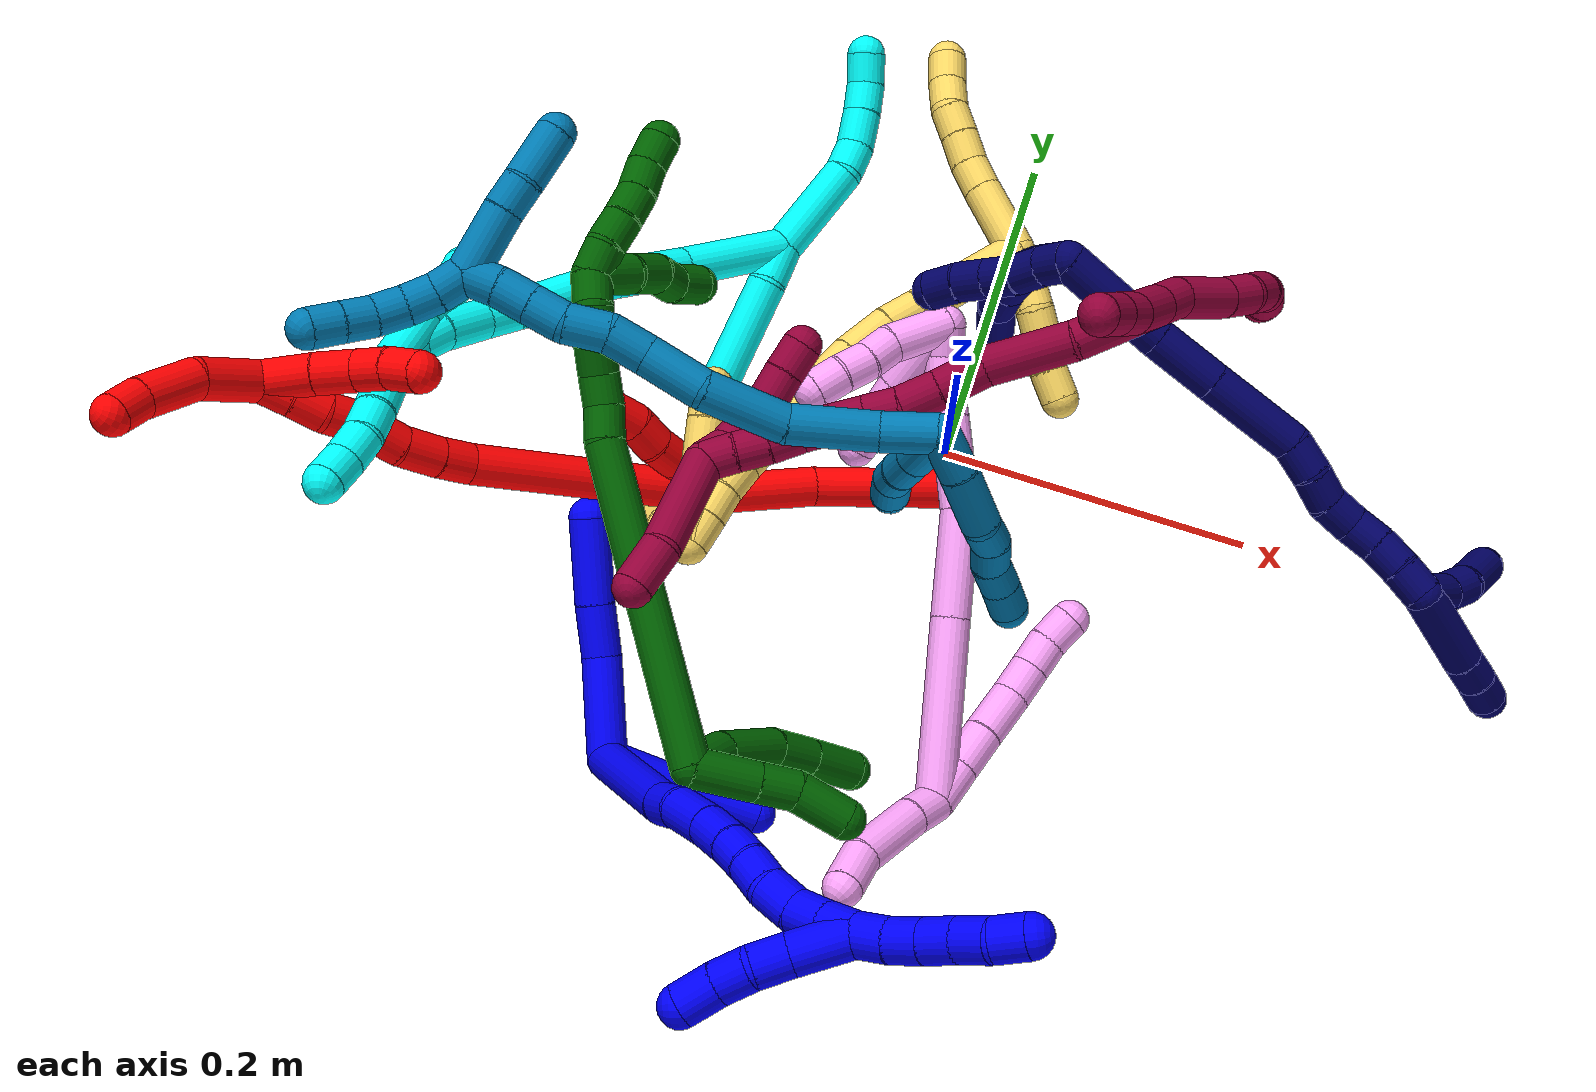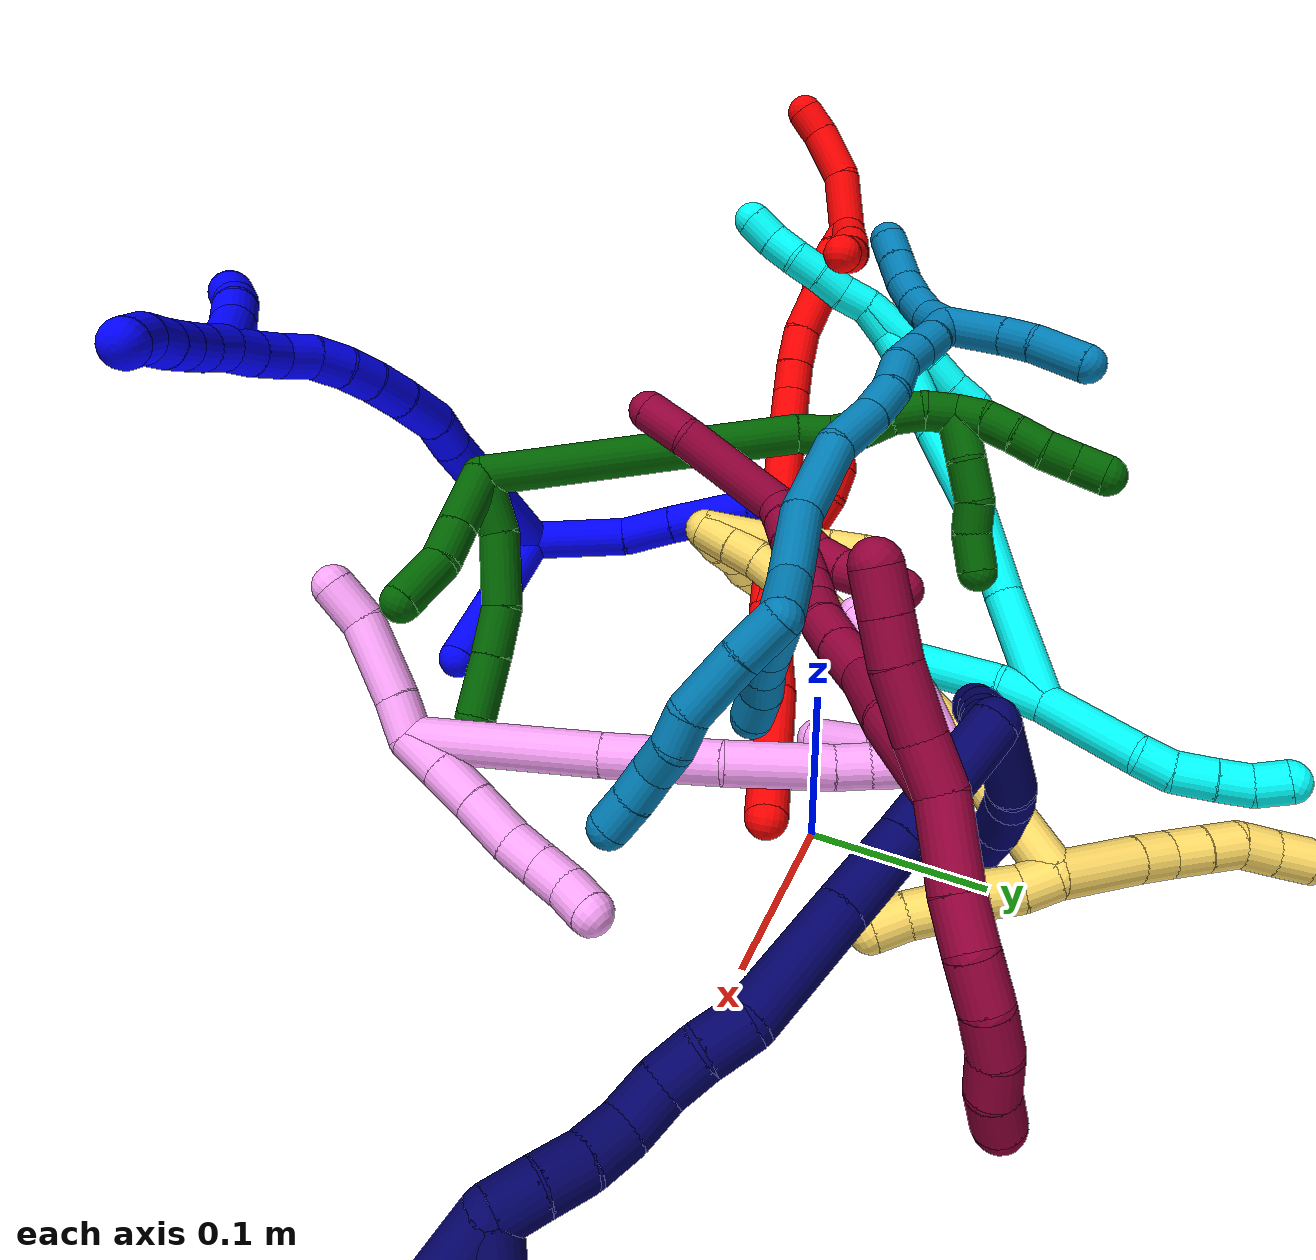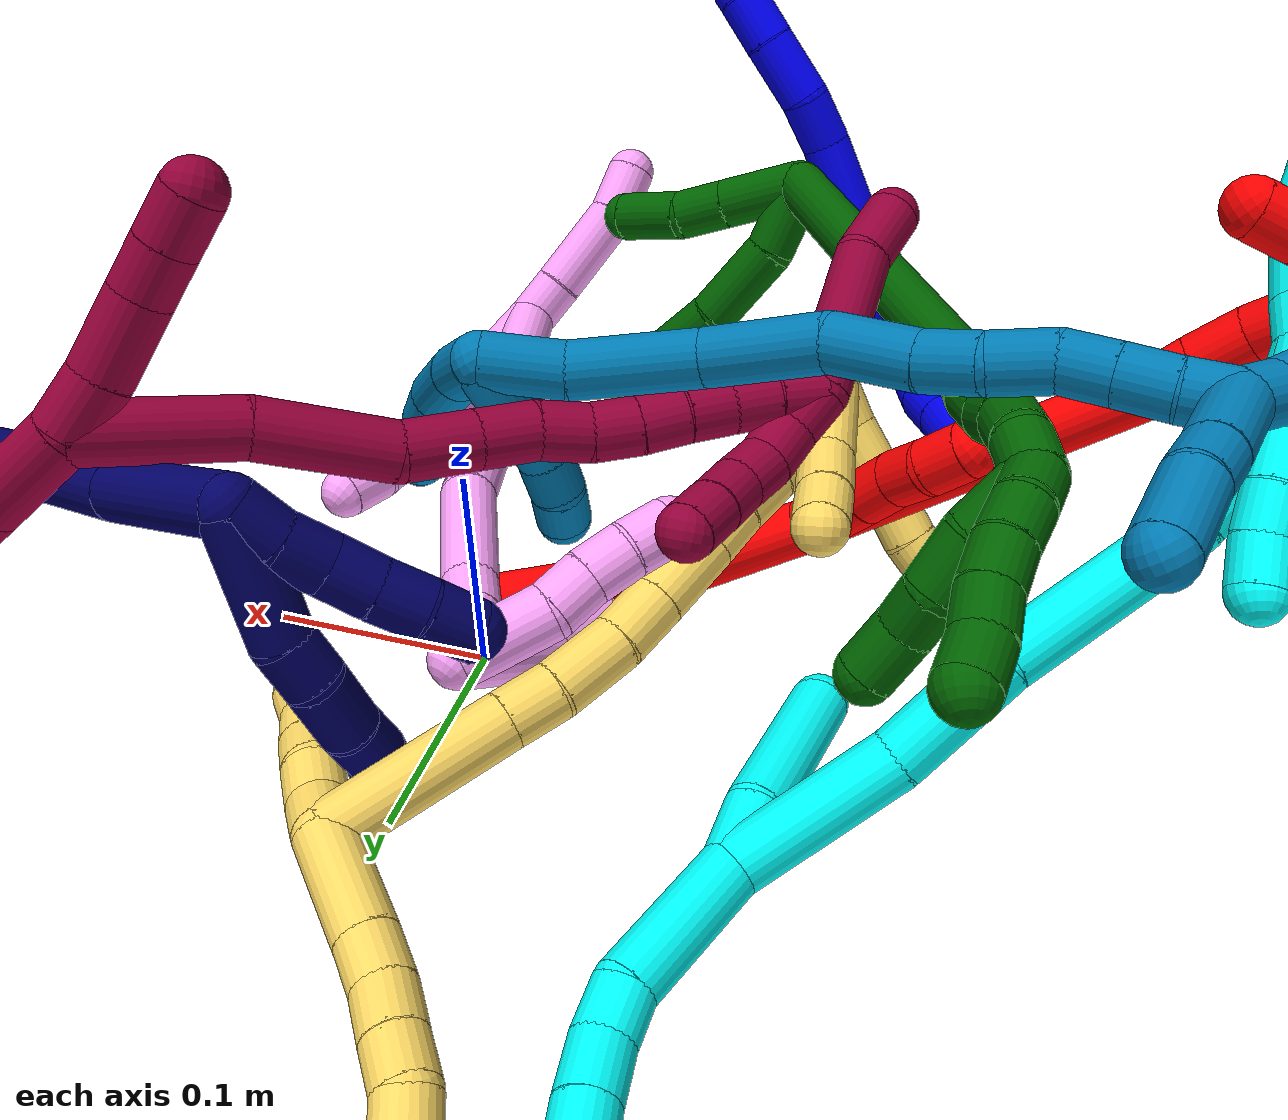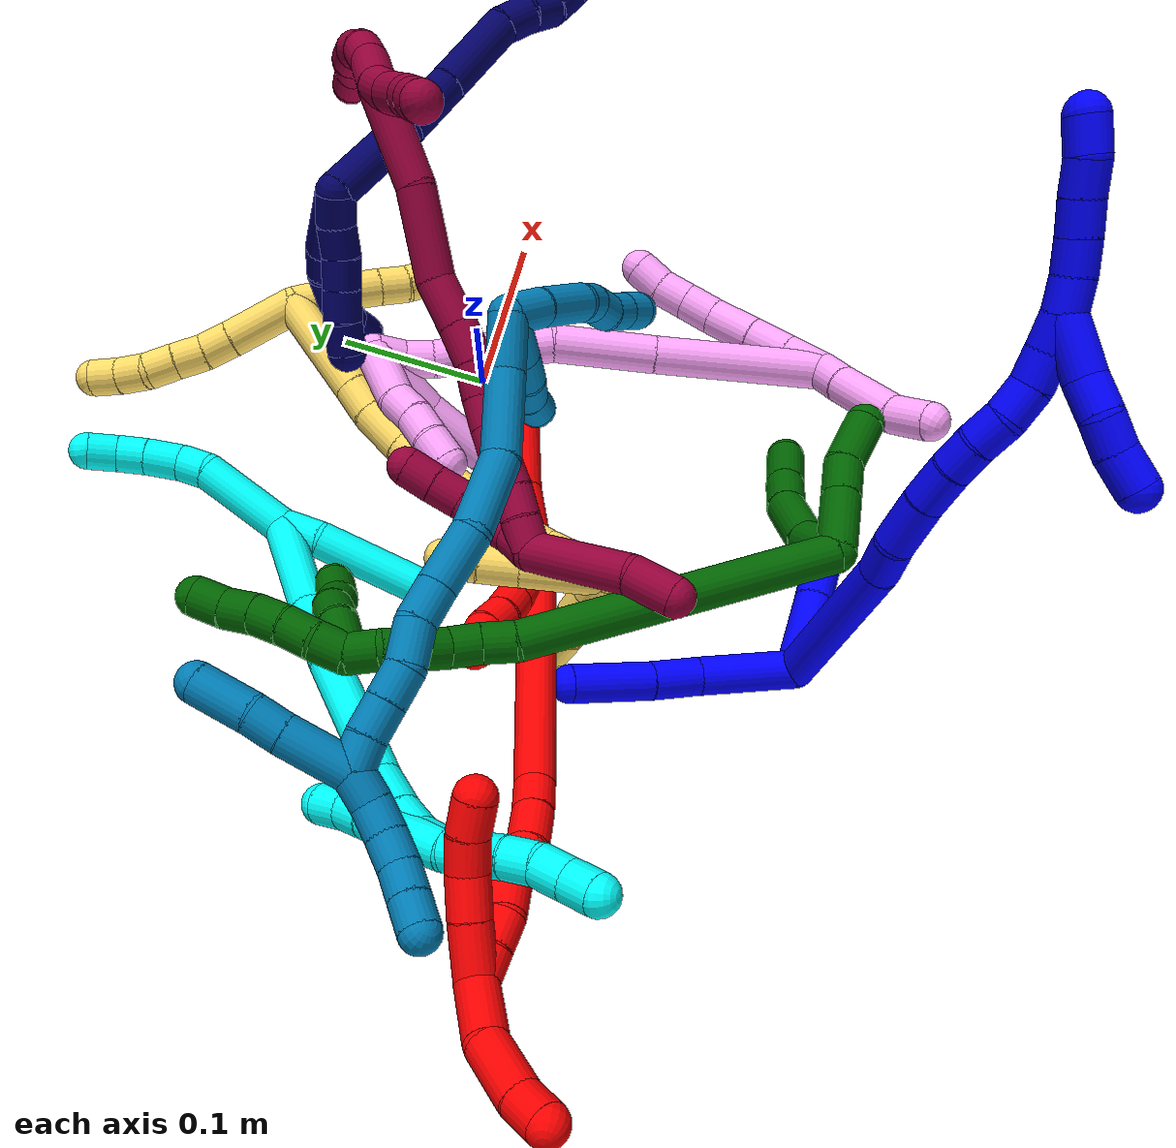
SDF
<sdf version="1.7">
 <world name="default">
  <plugin name="TubeGeneratorPlugin" filename="libtube_generator_plugin.so"/>
  <model name="photoneo_s_sensor">
   <static>1</static>
   <pose>0 0 2 1.57079 1.57079 3.14159</pose>
   <link name="link">
    <inertial><mass>0.1</mass></inertial>
    <sensor name="sensor" type="depth">
     <update_rate>30</update_rate>
     <camera>
      <horizontal_fov>1.22</horizontal_fov>
      <image><width>1920</width><height>1200</height><format>B8G8R8</format></image>
      <clip><near>0.1</near><far>4</far></clip>
      <depth_camera><output>points</output></depth_camera>
     </camera>
     <plugin name="camera_plugin" filename="libgazebo_ros_depth_camera.so">
      <baseline>0.2</baseline>
      <alwaysOn>1</alwaysOn>
      <updateRate>0.0</updateRate>
      <cameraName>camera_ir</cameraName>
      <imageTopicName>/camera/color/image_raw</imageTopicName>
      <cameraInfoTopicName>/camera/color/camera_info</cameraInfoTopicName>
      <depthImageTopicName>/camera/depth/image_raw</depthImageTopicName>
      <depthImageCameraInfoTopicName>/camera/depth/camera_info</depthImageCameraInfoTopicName>
      <pointCloudTopicName>/camera/depth/points</pointCloudTopicName>
      <frameName>fr_optical</frameName>
      <pointCloudCutoff>0.1</pointCloudCutoff>
      <pointCloudCutoffMax>2.0</pointCloudCutoffMax>
      <distortionK1>0</distortionK1>
      <distortionK2>0</distortionK2>
      <distortionK3>0</distortionK3>
      <distortionT1>0</distortionT1>
      <distortionT2>0</distortionT2>
      <CxPrime>0</CxPrime>
      <Cx>0</Cx>
      <Cy>0</Cy>
      <focalLength>0</focalLength>
      <hackBaseline>0</hackBaseline>
     </plugin>
    </sensor>
   </link>
  </model>
  <gravity>0 0 -9.8</gravity>
  <magnetic_field>6e-06 2.3e-05 -4.2e-05</magnetic_field>
  <atmosphere type="adiabatic"/>
  <physics name="default_physics" default="0" type="ode">
   <max_step_size>0.003</max_step_size>
   <real_time_factor>1</real_time_factor>
   <real_time_update_rate>1000</real_time_update_rate>
   <max_contacts>10000</max_contacts>
   <ode>
    <solver>
     <type>quick</type>
     <iters>100</iters>
     <sor>1.3</sor>
     <use_dynamic_moi_rescaling>0</use_dynamic_moi_rescaling>
    </solver>
    <constraints>
     <contact_max_correcting_vel>0</contact_max_correcting_vel>
     <contact_surface_layer>0.001</contact_surface_layer>
     <cfm>0</cfm>
     <erp>0.2</erp>
    </constraints>
   </ode>
  </physics>
  <scene><ambient>0.4 0.4 0.4 1</ambient><background>0.7 0.7 0.7 1</background><shadows>0</shadows></scene>
  <audio><device>default</device></audio>
  <spherical_coordinates>
   <surface_model>EARTH_WGS84</surface_model>
   <latitude_deg>0</latitude_deg>
   <longitude_deg>0</longitude_deg>
   <elevation>0</elevation>
   <heading_deg>0</heading_deg>
  </spherical_coordinates>
  <model name="bin">
   <static>1</static>
   <link name="bottom">
    <collision name="collision-bottom">
     <pose>0 0 -0.01 0 -0 0</pose>
     <geometry><box><size>0.8 0.6 0.02</size></box></geometry>
     <surface>
      <friction><ode><mu>100</mu><mu2>100</mu2></ode></friction>
      <contact><collide_bitmask>65535</collide_bitmask></contact>
     </surface>
    </collision>
   </link>
   <link name="west_wall">
    <collision name="collision-west_wall">
     <pose>-0.41 0 0.1 0 -0 0</pose>
     <geometry><box><size>0.02 0.6 0.2</size></box></geometry>
     <surface>
      <friction><ode><mu>100</mu><mu2>100</mu2></ode></friction>
      <contact><collide_bitmask>65535</collide_bitmask></contact>
     </surface>
    </collision>
   </link>
   <link name="east_wall">
    <collision name="collision-east_wall">
     <pose>0.41 0 0.1 0 -0 0</pose>
     <geometry><box><size>0.02 0.6 0.2</size></box></geometry>
     <surface>
      <friction><ode><mu>100</mu><mu2>100</mu2></ode></friction>
      <contact><collide_bitmask>65535</collide_bitmask></contact>
     </surface>
    </collision>
   </link>
   <link name="south_wall">
    <collision name="collision-south_wall">
     <pose>0 -0.31 0.1 0 -0 0</pose>
     <geometry><box><size>0.8 0.02 0.2</size></box></geometry>
     <surface>
      <friction><ode><mu>100</mu><mu2>100</mu2></ode></friction>
      <contact><collide_bitmask>65535</collide_bitmask></contact>
     </surface>
    </collision>
   </link>
   <link name="north_wall">
    <collision name="collision-north_wall">
     <pose>0 0.31 0.1 0 -0 0</pose>
     <geometry><box><size>0.8 0.02 0.2</size></box></geometry>
     <surface>
      <friction><ode><mu>100</mu><mu2>100</mu2></ode></friction>
      <contact><collide_bitmask>65535</collide_bitmask></contact>
     </surface>
    </collision>
   </link>
  </model>
  <model name="1">
   <static>0</static>
   <link name="1">
    <collision name="collision-cylinder-e_1_2_8">
     <pose>-0.031248 0.005356 -0.000579 -1.6785 -1.40007 1.50719</pose>
     <geometry><cylinder><radius>0.0125</radius><length>0.063418</length></cylinder></geometry>
     <surface>
      <friction><ode><mu>1.16</mu><mu2>1.16</mu2><slip1>0</slip1><slip2>0</slip2></ode></friction>
      <contact><ode><kp>1e+06</kp><kd>1</kd><max_vel>0</max_vel><min_depth>0.001</min_depth></ode></contact>
     </surface>
    </collision>
    <visual name="visual-cylinder-e_1_2_8">
     <pose>-0.031248 0.005356 -0.000579 -1.6785 -1.40007 1.50719</pose>
     <geometry><cylinder><radius>0.0125</radius><length>0.063418</length></cylinder></geometry>
     <material><ambient>0 0 1 1</ambient></material>
    </visual>
    <collision name="collision-cylinder-e_2_8_9">
     <pose>-0.077822 0.01696 -0.001065 -1.55583 -1.18363 1.16982</pose>
     <geometry><cylinder><radius>0.0125</radius><length>0.033104</length></cylinder></geometry>
     <surface>
      <friction><ode><mu>1.16</mu><mu2>1.16</mu2><slip1>0</slip1><slip2>0</slip2></ode></friction>
      <contact><ode><kp>1e+06</kp><kd>1</kd><max_vel>0</max_vel><min_depth>0.001</min_depth></ode></contact>
     </surface>
    </collision>
    <visual name="visual-cylinder-e_2_8_9">
     <pose>-0.077822 0.01696 -0.001065 -1.55583 -1.18363 1.16982</pose>
     <geometry><cylinder><radius>0.0125</radius><length>0.033104</length></cylinder></geometry>
     <material><ambient>0 0 1 1</ambient></material>
    </visual>
    <collision name="collision-cylinder-e_3_9_6">
     <pose>-0.118013 0.032957 -0.002306 -1.70687 -1.19399 1.32379</pose>
     <geometry><cylinder><radius>0.0125</radius><length>0.053479</length></cylinder></geometry>
     <surface>
      <friction><ode><mu>1.16</mu><mu2>1.16</mu2><slip1>0</slip1><slip2>0</slip2></ode></friction>
      <contact><ode><kp>1e+06</kp><kd>1</kd><max_vel>0</max_vel><min_depth>0.001</min_depth></ode></contact>
     </surface>
    </collision>
    <visual name="visual-cylinder-e_3_9_6">
     <pose>-0.118013 0.032957 -0.002306 -1.70687 -1.19399 1.32379</pose>
     <geometry><cylinder><radius>0.0125</radius><length>0.053479</length></cylinder></geometry>
     <material><ambient>0 0 1 1</ambient></material>
    </visual>
    <collision name="collision-cylinder-e_1_2_10">
     <pose>0.009305 -0.013395 -0.022246 2.59959 0.344082 1.11777</pose>
     <geometry><cylinder><radius>0.0125</radius><length>0.055169</length></cylinder></geometry>
     <surface>
      <friction><ode><mu>1.16</mu><mu2>1.16</mu2><slip1>0</slip1><slip2>0</slip2></ode></friction>
      <contact><ode><kp>1e+06</kp><kd>1</kd><max_vel>0</max_vel><min_depth>0.001</min_depth></ode></contact>
     </surface>
    </collision>
    <visual name="visual-cylinder-e_1_2_10">
     <pose>0.009305 -0.013395 -0.022246 2.59959 0.344082 1.11777</pose>
     <geometry><cylinder><radius>0.0125</radius><length>0.055169</length></cylinder></geometry>
     <material><ambient>0 0 1 1</ambient></material>
    </visual>
    <collision name="collision-cylinder-e_2_10_5">
     <pose>0.02589 -0.036109 -0.063535 2.68654 0.330767 1.2492</pose>
     <geometry><cylinder><radius>0.0125</radius><length>0.044831</length></cylinder></geometry>
     <surface>
      <friction><ode><mu>1.16</mu><mu2>1.16</mu2><slip1>0</slip1><slip2>0</slip2></ode></friction>
      <contact><ode><kp>1e+06</kp><kd>1</kd><max_vel>0</max_vel><min_depth>0.001</min_depth></ode></contact>
     </surface>
    </collision>
    <visual name="visual-cylinder-e_2_10_5">
     <pose>0.02589 -0.036109 -0.063535 2.68654 0.330767 1.2492</pose>
     <geometry><cylinder><radius>0.0125</radius><length>0.044831</length></cylinder></geometry>
     <material><ambient>0 0 1 1</ambient></material>
    </visual>
    <collision name="collision-cylinder-e_1_2_11">
     <pose>0.023943 0.044715 -0.025924 -2.0962 0.433809 -0.730644</pose>
     <geometry><cylinder><radius>0.0125</radius><length>0.113924</length></cylinder></geometry>
     <surface>
      <friction><ode><mu>1.16</mu><mu2>1.16</mu2><slip1>0</slip1><slip2>0</slip2></ode></friction>
      <contact><ode><kp>1e+06</kp><kd>1</kd><max_vel>0</max_vel><min_depth>0.001</min_depth></ode></contact>
     </surface>
    </collision>
    <visual name="visual-cylinder-e_1_2_11">
     <pose>0.023943 0.044715 -0.025924 -2.0962 0.433809 -0.730644</pose>
     <geometry><cylinder><radius>0.0125</radius><length>0.113924</length></cylinder></geometry>
     <material><ambient>0 0 1 1</ambient></material>
    </visual>
    <collision name="collision-cylinder-e_2_11_12">
     <pose>0.051574 0.099709 -0.058716 -2.15987 0.289891 -0.533194</pose>
     <geometry><cylinder><radius>0.0125</radius><length>0.025803</length></cylinder></geometry>
     <surface>
      <friction><ode><mu>1.16</mu><mu2>1.16</mu2><slip1>0</slip1><slip2>0</slip2></ode></friction>
      <contact><ode><kp>1e+06</kp><kd>1</kd><max_vel>0</max_vel><min_depth>0.001</min_depth></ode></contact>
     </surface>
    </collision>
    <visual name="visual-cylinder-e_2_11_12">
     <pose>0.051574 0.099709 -0.058716 -2.15987 0.289891 -0.533194</pose>
     <geometry><cylinder><radius>0.0125</radius><length>0.025803</length></cylinder></geometry>
     <material><ambient>0 0 1 1</ambient></material>
    </visual>
    <collision name="collision-cylinder-e_3_12_13">
     <pose>0.06312 0.120614 -0.075586 -2.32588 0.493981 -1.05646</pose>
     <geometry><cylinder><radius>0.0125</radius><length>0.033147</length></cylinder></geometry>
     <surface>
      <friction><ode><mu>1.16</mu><mu2>1.16</mu2><slip1>0</slip1><slip2>0</slip2></ode></friction>
      <contact><ode><kp>1e+06</kp><kd>1</kd><max_vel>0</max_vel><min_depth>0.001</min_depth></ode></contact>
     </surface>
    </collision>
    <visual name="visual-cylinder-e_3_12_13">
     <pose>0.06312 0.120614 -0.075586 -2.32588 0.493981 -1.05646</pose>
     <geometry><cylinder><radius>0.0125</radius><length>0.033147</length></cylinder></geometry>
     <material><ambient>0 0 1 1</ambient></material>
    </visual>
    <collision name="collision-cylinder-e_4_13_14">
     <pose>0.077978 0.138971 -0.092908 -2.32904 0.581601 -1.21562</pose>
     <geometry><cylinder><radius>0.0125</radius><length>0.025485</length></cylinder></geometry>
     <surface>
      <friction><ode><mu>1.16</mu><mu2>1.16</mu2><slip1>0</slip1><slip2>0</slip2></ode></friction>
      <contact><ode><kp>1e+06</kp><kd>1</kd><max_vel>0</max_vel><min_depth>0.001</min_depth></ode></contact>
     </surface>
    </collision>
    <visual name="visual-cylinder-e_4_13_14">
     <pose>0.077978 0.138971 -0.092908 -2.32904 0.581601 -1.21562</pose>
     <geometry><cylinder><radius>0.0125</radius><length>0.025485</length></cylinder></geometry>
     <material><ambient>0 0 1 1</ambient></material>
    </visual>
    <collision name="collision-cylinder-e_5_14_15">
     <pose>0.091357 0.152132 -0.105802 -2.36905 0.686689 -1.44222</pose>
     <geometry><cylinder><radius>0.0125</radius><length>0.020122</length></cylinder></geometry>
     <surface>
      <friction><ode><mu>1.16</mu><mu2>1.16</mu2><slip1>0</slip1><slip2>0</slip2></ode></friction>
      <contact><ode><kp>1e+06</kp><kd>1</kd><max_vel>0</max_vel><min_depth>0.001</min_depth></ode></contact>
     </surface>
    </collision>
    <visual name="visual-cylinder-e_5_14_15">
     <pose>0.091357 0.152132 -0.105802 -2.36905 0.686689 -1.44222</pose>
     <geometry><cylinder><radius>0.0125</radius><length>0.020122</length></cylinder></geometry>
     <material><ambient>0 0 1 1</ambient></material>
    </visual>
    <collision name="collision-cylinder-e_6_15_16">
     <pose>0.105125 0.16184 -0.116643 -2.45968 0.827871 -1.78282</pose>
     <geometry><cylinder><radius>0.0125</radius><length>0.020068</length></cylinder></geometry>
     <surface>
      <friction><ode><mu>1.16</mu><mu2>1.16</mu2><slip1>0</slip1><slip2>0</slip2></ode></friction>
      <contact><ode><kp>1e+06</kp><kd>1</kd><max_vel>0</max_vel><min_depth>0.001</min_depth></ode></contact>
     </surface>
    </collision>
    <visual name="visual-cylinder-e_6_15_16">
     <pose>0.105125 0.16184 -0.116643 -2.45968 0.827871 -1.78282</pose>
     <geometry><cylinder><radius>0.0125</radius><length>0.020068</length></cylinder></geometry>
     <material><ambient>0 0 1 1</ambient></material>
    </visual>
    <collision name="collision-cylinder-e_7_16_17">
     <pose>0.119575 0.168436 -0.129317 -2.8383 0.738318 -2.38923</pose>
     <geometry><cylinder><radius>0.0125</radius><length>0.020979</length></cylinder></geometry>
     <surface>
      <friction><ode><mu>1.16</mu><mu2>1.16</mu2><slip1>0</slip1><slip2>0</slip2></ode></friction>
      <contact><ode><kp>1e+06</kp><kd>1</kd><max_vel>0</max_vel><min_depth>0.001</min_depth></ode></contact>
     </surface>
    </collision>
    <visual name="visual-cylinder-e_7_16_17">
     <pose>0.119575 0.168436 -0.129317 -2.8383 0.738318 -2.38923</pose>
     <geometry><cylinder><radius>0.0125</radius><length>0.020979</length></cylinder></geometry>
     <material><ambient>0 0 1 1</ambient></material>
    </visual>
    <collision name="collision-cylinder-e_8_17_18">
     <pose>0.131167 0.174012 -0.145033 -2.76791 0.46971 -1.80425</pose>
     <geometry><cylinder><radius>0.0125</radius><length>0.020024</length></cylinder></geometry>
     <surface>
      <friction><ode><mu>1.16</mu><mu2>1.16</mu2><slip1>0</slip1><slip2>0</slip2></ode></friction>
      <contact><ode><kp>1e+06</kp><kd>1</kd><max_vel>0</max_vel><min_depth>0.001</min_depth></ode></contact>
     </surface>
    </collision>
    <visual name="visual-cylinder-e_8_17_18">
     <pose>0.131167 0.174012 -0.145033 -2.76791 0.46971 -1.80425</pose>
     <geometry><cylinder><radius>0.0125</radius><length>0.020024</length></cylinder></geometry>
     <material><ambient>0 0 1 1</ambient></material>
    </visual>
    <collision name="collision-cylinder-e_9_18_1">
     <pose>0.139861 0.181517 -0.161661 -2.66951 0.419283 -1.44849</pose>
     <geometry><cylinder><radius>0.0125</radius><length>0.020447</length></cylinder></geometry>
     <surface>
      <friction><ode><mu>1.16</mu><mu2>1.16</mu2><slip1>0</slip1><slip2>0</slip2></ode></friction>
      <contact><ode><kp>1e+06</kp><kd>1</kd><max_vel>0</max_vel><min_depth>0.001</min_depth></ode></contact>
     </surface>
    </collision>
    <visual name="visual-cylinder-e_9_18_1">
     <pose>0.139861 0.181517 -0.161661 -2.66951 0.419283 -1.44849</pose>
     <geometry><cylinder><radius>0.0125</radius><length>0.020447</length></cylinder></geometry>
     <material><ambient>0 0 1 1</ambient></material>
    </visual>
    <collision name="collision-cylinder-e_1_1_19">
     <pose>0.147632 0.185264 -0.152523 0.028614 0.203834 0.002927</pose>
     <geometry><cylinder><radius>0.0125</radius><length>0.035662</length></cylinder></geometry>
     <surface>
      <friction><ode><mu>1.16</mu><mu2>1.16</mu2><slip1>0</slip1><slip2>0</slip2></ode></friction>
      <contact><ode><kp>1e+06</kp><kd>1</kd><max_vel>0</max_vel><min_depth>0.001</min_depth></ode></contact>
     </surface>
    </collision>
    <visual name="visual-cylinder-e_1_1_19">
     <pose>0.147632 0.185264 -0.152523 0.028614 0.203834 0.002927</pose>
     <geometry><cylinder><radius>0.0125</radius><length>0.035662</length></cylinder></geometry>
     <material><ambient>0 0 1 1</ambient></material>
    </visual>
    <collision name="collision-cylinder-e_2_19_20">
     <pose>0.153965 0.185925 -0.124767 -0.112212 0.256872 -0.014507</pose>
     <geometry><cylinder><radius>0.0125</radius><length>0.021436</length></cylinder></geometry>
     <surface>
      <friction><ode><mu>1.16</mu><mu2>1.16</mu2><slip1>0</slip1><slip2>0</slip2></ode></friction>
      <contact><ode><kp>1e+06</kp><kd>1</kd><max_vel>0</max_vel><min_depth>0.001</min_depth></ode></contact>
     </surface>
    </collision>
    <visual name="visual-cylinder-e_2_19_20">
     <pose>0.153965 0.185925 -0.124767 -0.112212 0.256872 -0.014507</pose>
     <geometry><cylinder><radius>0.0125</radius><length>0.021436</length></cylinder></geometry>
     <material><ambient>0 0 1 1</ambient></material>
    </visual>
    <collision name="collision-cylinder-e_3_20_21">
     <pose>0.159693 0.185236 -0.105041 0.193894 0.303249 0.029717</pose>
     <geometry><cylinder><radius>0.0125</radius><length>0.020127</length></cylinder></geometry>
     <surface>
      <friction><ode><mu>1.16</mu><mu2>1.16</mu2><slip1>0</slip1><slip2>0</slip2></ode></friction>
      <contact><ode><kp>1e+06</kp><kd>1</kd><max_vel>0</max_vel><min_depth>0.001</min_depth></ode></contact>
     </surface>
    </collision>
    <visual name="visual-cylinder-e_3_20_21">
     <pose>0.159693 0.185236 -0.105041 0.193894 0.303249 0.029717</pose>
     <geometry><cylinder><radius>0.0125</radius><length>0.020127</length></cylinder></geometry>
     <material><ambient>0 0 1 1</ambient></material>
    </visual>
    <collision name="collision-cylinder-e_4_21_4">
     <pose>0.167538 0.182732 -0.08533 0.063372 0.439022 0.014143</pose>
     <geometry><cylinder><radius>0.0125</radius><length>0.022774</length></cylinder></geometry>
     <surface>
      <friction><ode><mu>1.16</mu><mu2>1.16</mu2><slip1>0</slip1><slip2>0</slip2></ode></friction>
      <contact><ode><kp>1e+06</kp><kd>1</kd><max_vel>0</max_vel><min_depth>0.001</min_depth></ode></contact>
     </surface>
    </collision>
    <visual name="visual-cylinder-e_4_21_4">
     <pose>0.167538 0.182732 -0.08533 0.063372 0.439022 0.014143</pose>
     <geometry><cylinder><radius>0.0125</radius><length>0.022774</length></cylinder></geometry>
     <material><ambient>0 0 1 1</ambient></material>
    </visual>
    <collision name="collision-cylinder-e_1_1_22">
     <pose>0.14671 0.188789 -0.179123 -2.8221 0.272066 -1.40845</pose>
     <geometry><cylinder><radius>0.0125</radius><length>0.02</length></cylinder></geometry>
     <surface>
      <friction><ode><mu>1.16</mu><mu2>1.16</mu2><slip1>0</slip1><slip2>0</slip2></ode></friction>
      <contact><ode><kp>1e+06</kp><kd>1</kd><max_vel>0</max_vel><min_depth>0.001</min_depth></ode></contact>
     </surface>
    </collision>
    <visual name="visual-cylinder-e_1_1_22">
     <pose>0.14671 0.188789 -0.179123 -2.8221 0.272066 -1.40845</pose>
     <geometry><cylinder><radius>0.0125</radius><length>0.02</length></cylinder></geometry>
     <material><ambient>0 0 1 1</ambient></material>
    </visual>
    <collision name="collision-cylinder-e_2_22_23">
     <pose>0.150787 0.195494 -0.197462 -2.76093 0.139408 -0.695325</pose>
     <geometry><cylinder><radius>0.0125</radius><length>0.02</length></cylinder></geometry>
     <surface>
      <friction><ode><mu>1.16</mu><mu2>1.16</mu2><slip1>0</slip1><slip2>0</slip2></ode></friction>
      <contact><ode><kp>1e+06</kp><kd>1</kd><max_vel>0</max_vel><min_depth>0.001</min_depth></ode></contact>
     </surface>
    </collision>
    <visual name="visual-cylinder-e_2_22_23">
     <pose>0.150787 0.195494 -0.197462 -2.76093 0.139408 -0.695325</pose>
     <geometry><cylinder><radius>0.0125</radius><length>0.02</length></cylinder></geometry>
     <material><ambient>0 0 1 1</ambient></material>
    </visual>
    <collision name="collision-cylinder-e_3_23_24">
     <pose>0.153064 0.203076 -0.215819 -2.73893 0.088931 -0.429298</pose>
     <geometry><cylinder><radius>0.0125</radius><length>0.02</length></cylinder></geometry>
     <surface>
      <friction><ode><mu>1.16</mu><mu2>1.16</mu2><slip1>0</slip1><slip2>0</slip2></ode></friction>
      <contact><ode><kp>1e+06</kp><kd>1</kd><max_vel>0</max_vel><min_depth>0.001</min_depth></ode></contact>
     </surface>
    </collision>
    <visual name="visual-cylinder-e_3_23_24">
     <pose>0.153064 0.203076 -0.215819 -2.73893 0.088931 -0.429298</pose>
     <geometry><cylinder><radius>0.0125</radius><length>0.02</length></cylinder></geometry>
     <material><ambient>0 0 1 1</ambient></material>
    </visual>
    <collision name="collision-cylinder-e_4_24_25">
     <pose>0.15534 0.211387 -0.233852 -2.68034 0.139164 -0.577074</pose>
     <geometry><cylinder><radius>0.0125</radius><length>0.02</length></cylinder></geometry>
     <surface>
      <friction><ode><mu>1.16</mu><mu2>1.16</mu2><slip1>0</slip1><slip2>0</slip2></ode></friction>
      <contact><ode><kp>1e+06</kp><kd>1</kd><max_vel>0</max_vel><min_depth>0.001</min_depth></ode></contact>
     </surface>
    </collision>
    <visual name="visual-cylinder-e_4_24_25">
     <pose>0.15534 0.211387 -0.233852 -2.68034 0.139164 -0.577074</pose>
     <geometry><cylinder><radius>0.0125</radius><length>0.02</length></cylinder></geometry>
     <material><ambient>0 0 1 1</ambient></material>
    </visual>
    <collision name="collision-cylinder-e_5_25_3">
     <pose>0.15676 0.218088 -0.252453 -2.91016 0.003308 -0.028455</pose>
     <geometry><cylinder><radius>0.0125</radius><length>0.02</length></cylinder></geometry>
     <surface>
      <friction><ode><mu>1.16</mu><mu2>1.16</mu2><slip1>0</slip1><slip2>0</slip2></ode></friction>
      <contact><ode><kp>1e+06</kp><kd>1</kd><max_vel>0</max_vel><min_depth>0.001</min_depth></ode></contact>
     </surface>
    </collision>
    <visual name="visual-cylinder-e_5_25_3">
     <pose>0.15676 0.218088 -0.252453 -2.91016 0.003308 -0.028455</pose>
     <geometry><cylinder><radius>0.0125</radius><length>0.02</length></cylinder></geometry>
     <material><ambient>0 0 1 1</ambient></material>
    </visual>
    <collision name="collision-sphere-3">
     <pose>0.156793 0.220382 -0.262187 0 -0 0</pose>
     <geometry><sphere><radius>0.0125</radius></sphere></geometry>
     <surface>
      <friction><ode><mu>1.16</mu><mu2>1.16</mu2><slip1>0</slip1><slip2>0</slip2></ode></friction>
      <contact><ode><kp>1e+06</kp><kd>1</kd><max_vel>0</max_vel><min_depth>0.001</min_depth></ode></contact>
     </surface>
    </collision>
    <visual name="visual-sphere-3">
     <pose>0.156793 0.220382 -0.262187 0 -0 0</pose>
     <geometry><sphere><radius>0.0125</radius></sphere></geometry>
     <material><ambient>0 0 1 1</ambient></material>
    </visual>
    <collision name="collision-sphere-25">
     <pose>0.156727 0.215795 -0.24272 0 -0 0</pose>
     <geometry><sphere><radius>0.0125</radius></sphere></geometry>
     <surface>
      <friction><ode><mu>1.16</mu><mu2>1.16</mu2><slip1>0</slip1><slip2>0</slip2></ode></friction>
      <contact><ode><kp>1e+06</kp><kd>1</kd><max_vel>0</max_vel><min_depth>0.001</min_depth></ode></contact>
     </surface>
    </collision>
    <visual name="visual-sphere-25">
     <pose>0.156727 0.215795 -0.24272 0 -0 0</pose>
     <geometry><sphere><radius>0.0125</radius></sphere></geometry>
     <material><ambient>0 0 1 1</ambient></material>
    </visual>
    <collision name="collision-sphere-24">
     <pose>0.153953 0.206979 -0.224983 0 -0 0</pose>
     <geometry><sphere><radius>0.0125</radius></sphere></geometry>
     <surface>
      <friction><ode><mu>1.16</mu><mu2>1.16</mu2><slip1>0</slip1><slip2>0</slip2></ode></friction>
      <contact><ode><kp>1e+06</kp><kd>1</kd><max_vel>0</max_vel><min_depth>0.001</min_depth></ode></contact>
     </surface>
    </collision>
    <visual name="visual-sphere-24">
     <pose>0.153953 0.206979 -0.224983 0 -0 0</pose>
     <geometry><sphere><radius>0.0125</radius></sphere></geometry>
     <material><ambient>0 0 1 1</ambient></material>
    </visual>
    <collision name="collision-sphere-23">
     <pose>0.152176 0.199173 -0.206656 0 -0 0</pose>
     <geometry><sphere><radius>0.0125</radius></sphere></geometry>
     <surface>
      <friction><ode><mu>1.16</mu><mu2>1.16</mu2><slip1>0</slip1><slip2>0</slip2></ode></friction>
      <contact><ode><kp>1e+06</kp><kd>1</kd><max_vel>0</max_vel><min_depth>0.001</min_depth></ode></contact>
     </surface>
    </collision>
    <visual name="visual-sphere-23">
     <pose>0.152176 0.199173 -0.206656 0 -0 0</pose>
     <geometry><sphere><radius>0.0125</radius></sphere></geometry>
     <material><ambient>0 0 1 1</ambient></material>
    </visual>
    <collision name="collision-sphere-22">
     <pose>0.149397 0.191814 -0.188267 0 -0 0</pose>
     <geometry><sphere><radius>0.0125</radius></sphere></geometry>
     <surface>
      <friction><ode><mu>1.16</mu><mu2>1.16</mu2><slip1>0</slip1><slip2>0</slip2></ode></friction>
      <contact><ode><kp>1e+06</kp><kd>1</kd><max_vel>0</max_vel><min_depth>0.001</min_depth></ode></contact>
     </surface>
    </collision>
    <visual name="visual-sphere-22">
     <pose>0.149397 0.191814 -0.188267 0 -0 0</pose>
     <geometry><sphere><radius>0.0125</radius></sphere></geometry>
     <material><ambient>0 0 1 1</ambient></material>
    </visual>
    <collision name="collision-sphere-4">
     <pose>0.172378 0.182079 -0.075044 0 -0 0</pose>
     <geometry><sphere><radius>0.0125</radius></sphere></geometry>
     <surface>
      <friction><ode><mu>1.16</mu><mu2>1.16</mu2><slip1>0</slip1><slip2>0</slip2></ode></friction>
      <contact><ode><kp>1e+06</kp><kd>1</kd><max_vel>0</max_vel><min_depth>0.001</min_depth></ode></contact>
     </surface>
    </collision>
    <visual name="visual-sphere-4">
     <pose>0.172378 0.182079 -0.075044 0 -0 0</pose>
     <geometry><sphere><radius>0.0125</radius></sphere></geometry>
     <material><ambient>0 0 1 1</ambient></material>
    </visual>
    <collision name="collision-sphere-21">
     <pose>0.162698 0.183385 -0.095617 0 -0 0</pose>
     <geometry><sphere><radius>0.0125</radius></sphere></geometry>
     <surface>
      <friction><ode><mu>1.16</mu><mu2>1.16</mu2><slip1>0</slip1><slip2>0</slip2></ode></friction>
      <contact><ode><kp>1e+06</kp><kd>1</kd><max_vel>0</max_vel><min_depth>0.001</min_depth></ode></contact>
     </surface>
    </collision>
    <visual name="visual-sphere-21">
     <pose>0.162698 0.183385 -0.095617 0 -0 0</pose>
     <geometry><sphere><radius>0.0125</radius></sphere></geometry>
     <material><ambient>0 0 1 1</ambient></material>
    </visual>
    <collision name="collision-sphere-20">
     <pose>0.156688 0.187086 -0.114466 0 -0 0</pose>
     <geometry><sphere><radius>0.0125</radius></sphere></geometry>
     <surface>
      <friction><ode><mu>1.16</mu><mu2>1.16</mu2><slip1>0</slip1><slip2>0</slip2></ode></friction>
      <contact><ode><kp>1e+06</kp><kd>1</kd><max_vel>0</max_vel><min_depth>0.001</min_depth></ode></contact>
     </surface>
    </collision>
    <visual name="visual-sphere-20">
     <pose>0.156688 0.187086 -0.114466 0 -0 0</pose>
     <geometry><sphere><radius>0.0125</radius></sphere></geometry>
     <material><ambient>0 0 1 1</ambient></material>
    </visual>
    <collision name="collision-sphere-5">
     <pose>0.03317 -0.045426 -0.082578 0 -0 0</pose>
     <geometry><sphere><radius>0.0125</radius></sphere></geometry>
     <surface>
      <friction><ode><mu>1.16</mu><mu2>1.16</mu2><slip1>0</slip1><slip2>0</slip2></ode></friction>
      <contact><ode><kp>1e+06</kp><kd>1</kd><max_vel>0</max_vel><min_depth>0.001</min_depth></ode></contact>
     </surface>
    </collision>
    <visual name="visual-sphere-5">
     <pose>0.03317 -0.045426 -0.082578 0 -0 0</pose>
     <geometry><sphere><radius>0.0125</radius></sphere></geometry>
     <material><ambient>0 0 1 1</ambient></material>
    </visual>
    <collision name="collision-sphere-10">
     <pose>0.01861 -0.026791 -0.044492 0 -0 0</pose>
     <geometry><sphere><radius>0.0125</radius></sphere></geometry>
     <surface>
      <friction><ode><mu>1.16</mu><mu2>1.16</mu2><slip1>0</slip1><slip2>0</slip2></ode></friction>
      <contact><ode><kp>1e+06</kp><kd>1</kd><max_vel>0</max_vel><min_depth>0.001</min_depth></ode></contact>
     </surface>
    </collision>
    <visual name="visual-sphere-10">
     <pose>0.01861 -0.026791 -0.044492 0 -0 0</pose>
     <geometry><sphere><radius>0.0125</radius></sphere></geometry>
     <material><ambient>0 0 1 1</ambient></material>
    </visual>
    <collision name="collision-sphere-6">
     <pose>-0.142876 0.042705 -0.00364 0 -0 0</pose>
     <geometry><sphere><radius>0.0125</radius></sphere></geometry>
     <surface>
      <friction><ode><mu>1.16</mu><mu2>1.16</mu2><slip1>0</slip1><slip2>0</slip2></ode></friction>
      <contact><ode><kp>1e+06</kp><kd>1</kd><max_vel>0</max_vel><min_depth>0.001</min_depth></ode></contact>
     </surface>
    </collision>
    <visual name="visual-sphere-6">
     <pose>-0.142876 0.042705 -0.00364 0 -0 0</pose>
     <geometry><sphere><radius>0.0125</radius></sphere></geometry>
     <material><ambient>0 0 1 1</ambient></material>
    </visual>
    <collision name="collision-sphere-9">
     <pose>-0.093149 0.023209 -0.000971 0 -0 0</pose>
     <geometry><sphere><radius>0.0125</radius></sphere></geometry>
     <surface>
      <friction><ode><mu>1.16</mu><mu2>1.16</mu2><slip1>0</slip1><slip2>0</slip2></ode></friction>
      <contact><ode><kp>1e+06</kp><kd>1</kd><max_vel>0</max_vel><min_depth>0.001</min_depth></ode></contact>
     </surface>
    </collision>
    <visual name="visual-sphere-9">
     <pose>-0.093149 0.023209 -0.000971 0 -0 0</pose>
     <geometry><sphere><radius>0.0125</radius></sphere></geometry>
     <material><ambient>0 0 1 1</ambient></material>
    </visual>
    <collision name="collision-sphere-2">
     <geometry><sphere><radius>0.0125</radius></sphere></geometry>
     <surface>
      <friction><ode><mu>1.16</mu><mu2>1.16</mu2><slip1>0</slip1><slip2>0</slip2></ode></friction>
      <contact><ode><kp>1e+06</kp><kd>1</kd><max_vel>0</max_vel><min_depth>0.001</min_depth></ode></contact>
     </surface>
    </collision>
    <visual name="visual-sphere-2">
     <geometry><sphere><radius>0.0125</radius></sphere></geometry>
     <material><ambient>0 0 1 1</ambient></material>
    </visual>
    <collision name="collision-sphere-19">
     <pose>0.151242 0.184764 -0.135068 0 -0 0</pose>
     <geometry><sphere><radius>0.0125</radius></sphere></geometry>
     <surface>
      <friction><ode><mu>1.16</mu><mu2>1.16</mu2><slip1>0</slip1><slip2>0</slip2></ode></friction>
      <contact><ode><kp>1e+06</kp><kd>1</kd><max_vel>0</max_vel><min_depth>0.001</min_depth></ode></contact>
     </surface>
    </collision>
    <visual name="visual-sphere-19">
     <pose>0.151242 0.184764 -0.135068 0 -0 0</pose>
     <geometry><sphere><radius>0.0125</radius></sphere></geometry>
     <material><ambient>0 0 1 1</ambient></material>
    </visual>
    <collision name="collision-sphere-8">
     <pose>-0.062496 0.010712 -0.001158 0 -0 0</pose>
     <geometry><sphere><radius>0.0125</radius></sphere></geometry>
     <surface>
      <friction><ode><mu>1.16</mu><mu2>1.16</mu2><slip1>0</slip1><slip2>0</slip2></ode></friction>
      <contact><ode><kp>1e+06</kp><kd>1</kd><max_vel>0</max_vel><min_depth>0.001</min_depth></ode></contact>
     </surface>
    </collision>
    <visual name="visual-sphere-8">
     <pose>-0.062496 0.010712 -0.001158 0 -0 0</pose>
     <geometry><sphere><radius>0.0125</radius></sphere></geometry>
     <material><ambient>0 0 1 1</ambient></material>
    </visual>
    <collision name="collision-sphere-11">
     <pose>0.047886 0.089429 -0.051847 0 -0 0</pose>
     <geometry><sphere><radius>0.0125</radius></sphere></geometry>
     <surface>
      <friction><ode><mu>1.16</mu><mu2>1.16</mu2><slip1>0</slip1><slip2>0</slip2></ode></friction>
      <contact><ode><kp>1e+06</kp><kd>1</kd><max_vel>0</max_vel><min_depth>0.001</min_depth></ode></contact>
     </surface>
    </collision>
    <visual name="visual-sphere-11">
     <pose>0.047886 0.089429 -0.051847 0 -0 0</pose>
     <geometry><sphere><radius>0.0125</radius></sphere></geometry>
     <material><ambient>0 0 1 1</ambient></material>
    </visual>
    <collision name="collision-sphere-12">
     <pose>0.055262 0.109988 -0.065585 0 -0 0</pose>
     <geometry><sphere><radius>0.0125</radius></sphere></geometry>
     <surface>
      <friction><ode><mu>1.16</mu><mu2>1.16</mu2><slip1>0</slip1><slip2>0</slip2></ode></friction>
      <contact><ode><kp>1e+06</kp><kd>1</kd><max_vel>0</max_vel><min_depth>0.001</min_depth></ode></contact>
     </surface>
    </collision>
    <visual name="visual-sphere-12">
     <pose>0.055262 0.109988 -0.065585 0 -0 0</pose>
     <geometry><sphere><radius>0.0125</radius></sphere></geometry>
     <material><ambient>0 0 1 1</ambient></material>
    </visual>
    <collision name="collision-sphere-13">
     <pose>0.070978 0.13124 -0.085587 0 -0 0</pose>
     <geometry><sphere><radius>0.0125</radius></sphere></geometry>
     <surface>
      <friction><ode><mu>1.16</mu><mu2>1.16</mu2><slip1>0</slip1><slip2>0</slip2></ode></friction>
      <contact><ode><kp>1e+06</kp><kd>1</kd><max_vel>0</max_vel><min_depth>0.001</min_depth></ode></contact>
     </surface>
    </collision>
    <visual name="visual-sphere-13">
     <pose>0.070978 0.13124 -0.085587 0 -0 0</pose>
     <geometry><sphere><radius>0.0125</radius></sphere></geometry>
     <material><ambient>0 0 1 1</ambient></material>
    </visual>
    <collision name="collision-sphere-14">
     <pose>0.084978 0.146701 -0.10023 0 -0 0</pose>
     <geometry><sphere><radius>0.0125</radius></sphere></geometry>
     <surface>
      <friction><ode><mu>1.16</mu><mu2>1.16</mu2><slip1>0</slip1><slip2>0</slip2></ode></friction>
      <contact><ode><kp>1e+06</kp><kd>1</kd><max_vel>0</max_vel><min_depth>0.001</min_depth></ode></contact>
     </surface>
    </collision>
    <visual name="visual-sphere-14">
     <pose>0.084978 0.146701 -0.10023 0 -0 0</pose>
     <geometry><sphere><radius>0.0125</radius></sphere></geometry>
     <material><ambient>0 0 1 1</ambient></material>
    </visual>
    <collision name="collision-sphere-15">
     <pose>0.097735 0.157562 -0.111374 0 -0 0</pose>
     <geometry><sphere><radius>0.0125</radius></sphere></geometry>
     <surface>
      <friction><ode><mu>1.16</mu><mu2>1.16</mu2><slip1>0</slip1><slip2>0</slip2></ode></friction>
      <contact><ode><kp>1e+06</kp><kd>1</kd><max_vel>0</max_vel><min_depth>0.001</min_depth></ode></contact>
     </surface>
    </collision>
    <visual name="visual-sphere-15">
     <pose>0.097735 0.157562 -0.111374 0 -0 0</pose>
     <geometry><sphere><radius>0.0125</radius></sphere></geometry>
     <material><ambient>0 0 1 1</ambient></material>
    </visual>
    <collision name="collision-sphere-16">
     <pose>0.112515 0.166118 -0.121913 0 -0 0</pose>
     <geometry><sphere><radius>0.0125</radius></sphere></geometry>
     <surface>
      <friction><ode><mu>1.16</mu><mu2>1.16</mu2><slip1>0</slip1><slip2>0</slip2></ode></friction>
      <contact><ode><kp>1e+06</kp><kd>1</kd><max_vel>0</max_vel><min_depth>0.001</min_depth></ode></contact>
     </surface>
    </collision>
    <visual name="visual-sphere-16">
     <pose>0.112515 0.166118 -0.121913 0 -0 0</pose>
     <geometry><sphere><radius>0.0125</radius></sphere></geometry>
     <material><ambient>0 0 1 1</ambient></material>
    </visual>
    <collision name="collision-sphere-17">
     <pose>0.126635 0.170753 -0.136721 0 -0 0</pose>
     <geometry><sphere><radius>0.0125</radius></sphere></geometry>
     <surface>
      <friction><ode><mu>1.16</mu><mu2>1.16</mu2><slip1>0</slip1><slip2>0</slip2></ode></friction>
      <contact><ode><kp>1e+06</kp><kd>1</kd><max_vel>0</max_vel><min_depth>0.001</min_depth></ode></contact>
     </surface>
    </collision>
    <visual name="visual-sphere-17">
     <pose>0.126635 0.170753 -0.136721 0 -0 0</pose>
     <geometry><sphere><radius>0.0125</radius></sphere></geometry>
     <material><ambient>0 0 1 1</ambient></material>
    </visual>
    <collision name="collision-sphere-18">
     <pose>0.135698 0.177271 -0.153344 0 -0 0</pose>
     <geometry><sphere><radius>0.0125</radius></sphere></geometry>
     <surface>
      <friction><ode><mu>1.16</mu><mu2>1.16</mu2><slip1>0</slip1><slip2>0</slip2></ode></friction>
      <contact><ode><kp>1e+06</kp><kd>1</kd><max_vel>0</max_vel><min_depth>0.001</min_depth></ode></contact>
     </surface>
    </collision>
    <visual name="visual-sphere-18">
     <pose>0.135698 0.177271 -0.153344 0 -0 0</pose>
     <geometry><sphere><radius>0.0125</radius></sphere></geometry>
     <material><ambient>0 0 1 1</ambient></material>
    </visual>
    <collision name="collision-sphere-1">
     <pose>0.144023 0.185764 -0.169978 0 -0 0</pose>
     <geometry><sphere><radius>0.0125</radius></sphere></geometry>
     <surface>
      <friction><ode><mu>1.16</mu><mu2>1.16</mu2><slip1>0</slip1><slip2>0</slip2></ode></friction>
      <contact><ode><kp>1e+06</kp><kd>1</kd><max_vel>0</max_vel><min_depth>0.001</min_depth></ode></contact>
     </surface>
    </collision>
    <visual name="visual-sphere-1">
     <pose>0.144023 0.185764 -0.169978 0 -0 0</pose>
     <geometry><sphere><radius>0.0125</radius></sphere></geometry>
     <material><ambient>0 0 1 1</ambient></material>
    </visual>
    <inertial>
     <pose>0.055645 0.09516 -0.081001 0 -0 0</pose>
     <mass>0.75</mass>
     <inertia>
      <ixx>6.2e-05</ixx>
      <ixy>0</ixy>
      <ixz>0</ixz>
      <iyy>-1.7e-05</iyy>
      <iyz>0</iyz>
      <izz>-0.000164</izz>
     </inertia>
    </inertial>
   </link>
   <pose>-0.13936 -0.255768 0.039207 1.70073 -0.09936 -1.19551</pose>
  </model>
  <model name="2">
   <static>0</static>
   <link name="2">
    <collision name="collision-cylinder-e_1_2_8">
     <pose>0.016115 0.006803 -0.02625 -2.88802 0.536197 -2.27269</pose>
     <geometry><cylinder><radius>0.0125</radius><length>0.063089</length></cylinder></geometry>
     <surface>
      <friction><ode><mu>1.16</mu><mu2>1.16</mu2><slip1>0</slip1><slip2>0</slip2></ode></friction>
      <contact><ode><kp>1e+06</kp><kd>1</kd><max_vel>0</max_vel><min_depth>0.001</min_depth></ode></contact>
     </surface>
    </collision>
    <visual name="visual-cylinder-e_1_2_8">
     <pose>0.016115 0.006803 -0.02625 -2.88802 0.536197 -2.27269</pose>
     <geometry><cylinder><radius>0.0125</radius><length>0.063089</length></cylinder></geometry>
     <material><ambient>1 0 0 1</ambient></material>
    </visual>
    <collision name="collision-cylinder-e_2_8_6">
     <pose>0.058947 0.017326 -0.086571 -3.03281 0.662132 -2.82741</pose>
     <geometry><cylinder><radius>0.0125</radius><length>0.086911</length></cylinder></geometry>
     <surface>
      <friction><ode><mu>1.16</mu><mu2>1.16</mu2><slip1>0</slip1><slip2>0</slip2></ode></friction>
      <contact><ode><kp>1e+06</kp><kd>1</kd><max_vel>0</max_vel><min_depth>0.001</min_depth></ode></contact>
     </surface>
    </collision>
    <visual name="visual-cylinder-e_2_8_6">
     <pose>0.058947 0.017326 -0.086571 -3.03281 0.662132 -2.82741</pose>
     <geometry><cylinder><radius>0.0125</radius><length>0.086911</length></cylinder></geometry>
     <material><ambient>1 0 0 1</ambient></material>
    </visual>
    <collision name="collision-cylinder-e_1_2_9">
     <pose>0.000147 0.002766 0.009609 -0.280285 0.014717 -0.002076</pose>
     <geometry><cylinder><radius>0.0125</radius><length>0.02</length></cylinder></geometry>
     <surface>
      <friction><ode><mu>1.16</mu><mu2>1.16</mu2><slip1>0</slip1><slip2>0</slip2></ode></friction>
      <contact><ode><kp>1e+06</kp><kd>1</kd><max_vel>0</max_vel><min_depth>0.001</min_depth></ode></contact>
     </surface>
    </collision>
    <visual name="visual-cylinder-e_1_2_9">
     <pose>0.000147 0.002766 0.009609 -0.280285 0.014717 -0.002076</pose>
     <geometry><cylinder><radius>0.0125</radius><length>0.02</length></cylinder></geometry>
     <material><ambient>1 0 0 1</ambient></material>
    </visual>
    <collision name="collision-cylinder-e_2_9_10">
     <pose>0.000965 0.008025 0.028878 -0.252547 0.067108 -0.008522</pose>
     <geometry><cylinder><radius>0.0125</radius><length>0.02</length></cylinder></geometry>
     <surface>
      <friction><ode><mu>1.16</mu><mu2>1.16</mu2><slip1>0</slip1><slip2>0</slip2></ode></friction>
      <contact><ode><kp>1e+06</kp><kd>1</kd><max_vel>0</max_vel><min_depth>0.001</min_depth></ode></contact>
     </surface>
    </collision>
    <visual name="visual-cylinder-e_2_9_10">
     <pose>0.000965 0.008025 0.028878 -0.252547 0.067108 -0.008522</pose>
     <geometry><cylinder><radius>0.0125</radius><length>0.02</length></cylinder></geometry>
     <material><ambient>1 0 0 1</ambient></material>
    </visual>
    <collision name="collision-cylinder-e_3_10_11">
     <pose>0.002229 0.012705 0.048279 -0.220846 0.059429 -0.006591</pose>
     <geometry><cylinder><radius>0.0125</radius><length>0.02</length></cylinder></geometry>
     <surface>
      <friction><ode><mu>1.16</mu><mu2>1.16</mu2><slip1>0</slip1><slip2>0</slip2></ode></friction>
      <contact><ode><kp>1e+06</kp><kd>1</kd><max_vel>0</max_vel><min_depth>0.001</min_depth></ode></contact>
     </surface>
    </collision>
    <visual name="visual-cylinder-e_3_10_11">
     <pose>0.002229 0.012705 0.048279 -0.220846 0.059429 -0.006591</pose>
     <geometry><cylinder><radius>0.0125</radius><length>0.02</length></cylinder></geometry>
     <material><ambient>1 0 0 1</ambient></material>
    </visual>
    <collision name="collision-cylinder-e_4_11_12">
     <pose>0.003386 0.01882 0.067198 -0.404429 0.056249 -0.011535</pose>
     <geometry><cylinder><radius>0.0125</radius><length>0.02</length></cylinder></geometry>
     <surface>
      <friction><ode><mu>1.16</mu><mu2>1.16</mu2><slip1>0</slip1><slip2>0</slip2></ode></friction>
      <contact><ode><kp>1e+06</kp><kd>1</kd><max_vel>0</max_vel><min_depth>0.001</min_depth></ode></contact>
     </surface>
    </collision>
    <visual name="visual-cylinder-e_4_11_12">
     <pose>0.003386 0.01882 0.067198 -0.404429 0.056249 -0.011535</pose>
     <geometry><cylinder><radius>0.0125</radius><length>0.02</length></cylinder></geometry>
     <material><ambient>1 0 0 1</ambient></material>
    </visual>
    <collision name="collision-cylinder-e_5_12_5">
     <pose>0.002949 0.024439 0.086182 -0.17073 -0.100042 0.008568</pose>
     <geometry><cylinder><radius>0.0125</radius><length>0.02</length></cylinder></geometry>
     <surface>
      <friction><ode><mu>1.16</mu><mu2>1.16</mu2><slip1>0</slip1><slip2>0</slip2></ode></friction>
      <contact><ode><kp>1e+06</kp><kd>1</kd><max_vel>0</max_vel><min_depth>0.001</min_depth></ode></contact>
     </surface>
    </collision>
    <visual name="visual-cylinder-e_5_12_5">
     <pose>0.002949 0.024439 0.086182 -0.17073 -0.100042 0.008568</pose>
     <geometry><cylinder><radius>0.0125</radius><length>0.02</length></cylinder></geometry>
     <material><ambient>1 0 0 1</ambient></material>
    </visual>
    <collision name="collision-cylinder-e_1_2_13">
     <pose>-0.028587 -0.006414 0.075492 0.084755 -0.360803 -0.015467</pose>
     <geometry><cylinder><radius>0.0125</radius><length>0.161956</length></cylinder></geometry>
     <surface>
      <friction><ode><mu>1.16</mu><mu2>1.16</mu2><slip1>0</slip1><slip2>0</slip2></ode></friction>
      <contact><ode><kp>1e+06</kp><kd>1</kd><max_vel>0</max_vel><min_depth>0.001</min_depth></ode></contact>
     </surface>
    </collision>
    <visual name="visual-cylinder-e_1_2_13">
     <pose>-0.028587 -0.006414 0.075492 0.084755 -0.360803 -0.015467</pose>
     <geometry><cylinder><radius>0.0125</radius><length>0.161956</length></cylinder></geometry>
     <material><ambient>1 0 0 1</ambient></material>
    </visual>
    <collision name="collision-cylinder-e_2_13_14">
     <pose>-0.058669 -0.013549 0.161707 0.067197 -0.1382 -0.004652</pose>
     <geometry><cylinder><radius>0.0125</radius><length>0.0217</length></cylinder></geometry>
     <surface>
      <friction><ode><mu>1.16</mu><mu2>1.16</mu2><slip1>0</slip1><slip2>0</slip2></ode></friction>
      <contact><ode><kp>1e+06</kp><kd>1</kd><max_vel>0</max_vel><min_depth>0.001</min_depth></ode></contact>
     </surface>
    </collision>
    <visual name="visual-cylinder-e_2_13_14">
     <pose>-0.058669 -0.013549 0.161707 0.067197 -0.1382 -0.004652</pose>
     <geometry><cylinder><radius>0.0125</radius><length>0.0217</length></cylinder></geometry>
     <material><ambient>1 0 0 1</ambient></material>
    </visual>
    <collision name="collision-cylinder-e_3_14_15">
     <pose>-0.061941 -0.014099 0.18497 -0.013665 -0.140762 0.000963</pose>
     <geometry><cylinder><radius>0.0125</radius><length>0.025334</length></cylinder></geometry>
     <surface>
      <friction><ode><mu>1.16</mu><mu2>1.16</mu2><slip1>0</slip1><slip2>0</slip2></ode></friction>
      <contact><ode><kp>1e+06</kp><kd>1</kd><max_vel>0</max_vel><min_depth>0.001</min_depth></ode></contact>
     </surface>
    </collision>
    <visual name="visual-cylinder-e_3_14_15">
     <pose>-0.061941 -0.014099 0.18497 -0.013665 -0.140762 0.000963</pose>
     <geometry><cylinder><radius>0.0125</radius><length>0.025334</length></cylinder></geometry>
     <material><ambient>1 0 0 1</ambient></material>
    </visual>
    <collision name="collision-cylinder-e_4_15_16">
     <pose>-0.065529 -0.010625 0.212108 -0.22255 -0.120361 0.013465</pose>
     <geometry><cylinder><radius>0.0125</radius><length>0.030152</length></cylinder></geometry>
     <surface>
      <friction><ode><mu>1.16</mu><mu2>1.16</mu2><slip1>0</slip1><slip2>0</slip2></ode></friction>
      <contact><ode><kp>1e+06</kp><kd>1</kd><max_vel>0</max_vel><min_depth>0.001</min_depth></ode></contact>
     </surface>
    </collision>
    <visual name="visual-cylinder-e_4_15_16">
     <pose>-0.065529 -0.010625 0.212108 -0.22255 -0.120361 0.013465</pose>
     <geometry><cylinder><radius>0.0125</radius><length>0.030152</length></cylinder></geometry>
     <material><ambient>1 0 0 1</ambient></material>
    </visual>
    <collision name="collision-cylinder-e_5_16_17">
     <pose>-0.069209 -0.007045 0.236772 -0.027456 -0.183645 0.002528</pose>
     <geometry><cylinder><radius>0.0125</radius><length>0.020484</length></cylinder></geometry>
     <surface>
      <friction><ode><mu>1.16</mu><mu2>1.16</mu2><slip1>0</slip1><slip2>0</slip2></ode></friction>
      <contact><ode><kp>1e+06</kp><kd>1</kd><max_vel>0</max_vel><min_depth>0.001</min_depth></ode></contact>
     </surface>
    </collision>
    <visual name="visual-cylinder-e_5_16_17">
     <pose>-0.069209 -0.007045 0.236772 -0.027456 -0.183645 0.002528</pose>
     <geometry><cylinder><radius>0.0125</radius><length>0.020484</length></cylinder></geometry>
     <material><ambient>1 0 0 1</ambient></material>
    </visual>
    <collision name="collision-cylinder-e_6_17_18">
     <pose>-0.07413 -0.004155 0.256055 -0.276246 -0.308247 0.043185</pose>
     <geometry><cylinder><radius>0.0125</radius><length>0.020109</length></cylinder></geometry>
     <surface>
      <friction><ode><mu>1.16</mu><mu2>1.16</mu2><slip1>0</slip1><slip2>0</slip2></ode></friction>
      <contact><ode><kp>1e+06</kp><kd>1</kd><max_vel>0</max_vel><min_depth>0.001</min_depth></ode></contact>
     </surface>
    </collision>
    <visual name="visual-cylinder-e_6_17_18">
     <pose>-0.07413 -0.004155 0.256055 -0.276246 -0.308247 0.043185</pose>
     <geometry><cylinder><radius>0.0125</radius><length>0.020109</length></cylinder></geometry>
     <material><ambient>1 0 0 1</ambient></material>
    </visual>
    <collision name="collision-cylinder-e_7_18_1">
     <pose>-0.081301 0.001298 0.274083 -0.311857 -0.418825 0.066796</pose>
     <geometry><cylinder><radius>0.0125</radius><length>0.020265</length></cylinder></geometry>
     <surface>
      <friction><ode><mu>1.16</mu><mu2>1.16</mu2><slip1>0</slip1><slip2>0</slip2></ode></friction>
      <contact><ode><kp>1e+06</kp><kd>1</kd><max_vel>0</max_vel><min_depth>0.001</min_depth></ode></contact>
     </surface>
    </collision>
    <visual name="visual-cylinder-e_7_18_1">
     <pose>-0.081301 0.001298 0.274083 -0.311857 -0.418825 0.066796</pose>
     <geometry><cylinder><radius>0.0125</radius><length>0.020265</length></cylinder></geometry>
     <material><ambient>1 0 0 1</ambient></material>
    </visual>
    <collision name="collision-cylinder-e_1_1_19">
     <pose>-0.086046 -0.001448 0.303159 0.268946 -0.029676 -0.004015</pose>
     <geometry><cylinder><radius>0.0125</radius><length>0.042063</length></cylinder></geometry>
     <surface>
      <friction><ode><mu>1.16</mu><mu2>1.16</mu2><slip1>0</slip1><slip2>0</slip2></ode></friction>
      <contact><ode><kp>1e+06</kp><kd>1</kd><max_vel>0</max_vel><min_depth>0.001</min_depth></ode></contact>
     </surface>
    </collision>
    <visual name="visual-cylinder-e_1_1_19">
     <pose>-0.086046 -0.001448 0.303159 0.268946 -0.029676 -0.004015</pose>
     <geometry><cylinder><radius>0.0125</radius><length>0.042063</length></cylinder></geometry>
     <material><ambient>1 0 0 1</ambient></material>
    </visual>
    <collision name="collision-cylinder-e_2_19_20">
     <pose>-0.088291 -0.017527 0.338863 0.596997 -0.08666 -0.02668</pose>
     <geometry><cylinder><radius>0.0125</radius><length>0.037472</length></cylinder></geometry>
     <surface>
      <friction><ode><mu>1.16</mu><mu2>1.16</mu2><slip1>0</slip1><slip2>0</slip2></ode></friction>
      <contact><ode><kp>1e+06</kp><kd>1</kd><max_vel>0</max_vel><min_depth>0.001</min_depth></ode></contact>
     </surface>
    </collision>
    <visual name="visual-cylinder-e_2_19_20">
     <pose>-0.088291 -0.017527 0.338863 0.596997 -0.08666 -0.02668</pose>
     <geometry><cylinder><radius>0.0125</radius><length>0.037472</length></cylinder></geometry>
     <material><ambient>1 0 0 1</ambient></material>
    </visual>
    <collision name="collision-cylinder-e_3_20_4">
     <pose>-0.089568 -0.03508 0.361699 0.762007 0.033713 0.013506</pose>
     <geometry><cylinder><radius>0.0125</radius><length>0.020465</length></cylinder></geometry>
     <surface>
      <friction><ode><mu>1.16</mu><mu2>1.16</mu2><slip1>0</slip1><slip2>0</slip2></ode></friction>
      <contact><ode><kp>1e+06</kp><kd>1</kd><max_vel>0</max_vel><min_depth>0.001</min_depth></ode></contact>
     </surface>
    </collision>
    <visual name="visual-cylinder-e_3_20_4">
     <pose>-0.089568 -0.03508 0.361699 0.762007 0.033713 0.013506</pose>
     <geometry><cylinder><radius>0.0125</radius><length>0.020465</length></cylinder></geometry>
     <material><ambient>1 0 0 1</ambient></material>
    </visual>
    <collision name="collision-cylinder-e_1_1_21">
     <pose>-0.071603 0.006087 0.274077 -2.92403 0.992057 -2.74331</pose>
     <geometry><cylinder><radius>0.0125</radius><length>0.033014</length></cylinder></geometry>
     <surface>
      <friction><ode><mu>1.16</mu><mu2>1.16</mu2><slip1>0</slip1><slip2>0</slip2></ode></friction>
      <contact><ode><kp>1e+06</kp><kd>1</kd><max_vel>0</max_vel><min_depth>0.001</min_depth></ode></contact>
     </surface>
    </collision>
    <visual name="visual-cylinder-e_1_1_21">
     <pose>-0.071603 0.006087 0.274077 -2.92403 0.992057 -2.74331</pose>
     <geometry><cylinder><radius>0.0125</radius><length>0.033014</length></cylinder></geometry>
     <material><ambient>1 0 0 1</ambient></material>
    </visual>
    <collision name="collision-cylinder-e_2_21_22">
     <pose>-0.047644 0.008985 0.258094 -3.00994 0.951424 -2.88705</pose>
     <geometry><cylinder><radius>0.0125</radius><length>0.024907</length></cylinder></geometry>
     <surface>
      <friction><ode><mu>1.16</mu><mu2>1.16</mu2><slip1>0</slip1><slip2>0</slip2></ode></friction>
      <contact><ode><kp>1e+06</kp><kd>1</kd><max_vel>0</max_vel><min_depth>0.001</min_depth></ode></contact>
     </surface>
    </collision>
    <visual name="visual-cylinder-e_2_21_22">
     <pose>-0.047644 0.008985 0.258094 -3.00994 0.951424 -2.88705</pose>
     <geometry><cylinder><radius>0.0125</radius><length>0.024907</length></cylinder></geometry>
     <material><ambient>1 0 0 1</ambient></material>
    </visual>
    <collision name="collision-cylinder-e_3_22_23">
     <pose>-0.027446 0.009442 0.247335 3.00534 1.22481 2.94795</pose>
     <geometry><cylinder><radius>0.0125</radius><length>0.021383</length></cylinder></geometry>
     <surface>
      <friction><ode><mu>1.16</mu><mu2>1.16</mu2><slip1>0</slip1><slip2>0</slip2></ode></friction>
      <contact><ode><kp>1e+06</kp><kd>1</kd><max_vel>0</max_vel><min_depth>0.001</min_depth></ode></contact>
     </surface>
    </collision>
    <visual name="visual-cylinder-e_3_22_23">
     <pose>-0.027446 0.009442 0.247335 3.00534 1.22481 2.94795</pose>
     <geometry><cylinder><radius>0.0125</radius><length>0.021383</length></cylinder></geometry>
     <material><ambient>1 0 0 1</ambient></material>
    </visual>
    <collision name="collision-cylinder-e_4_23_3">
     <pose>-0.007872 0.006756 0.24032 2.5718 1.16713 2.30664</pose>
     <geometry><cylinder><radius>0.0125</radius><length>0.020697</length></cylinder></geometry>
     <surface>
      <friction><ode><mu>1.16</mu><mu2>1.16</mu2><slip1>0</slip1><slip2>0</slip2></ode></friction>
      <contact><ode><kp>1e+06</kp><kd>1</kd><max_vel>0</max_vel><min_depth>0.001</min_depth></ode></contact>
     </surface>
    </collision>
    <visual name="visual-cylinder-e_4_23_3">
     <pose>-0.007872 0.006756 0.24032 2.5718 1.16713 2.30664</pose>
     <geometry><cylinder><radius>0.0125</radius><length>0.020697</length></cylinder></geometry>
     <material><ambient>1 0 0 1</ambient></material>
    </visual>
    <collision name="collision-sphere-3">
     <pose>0.001645 0.004564 0.236898 0 -0 0</pose>
     <geometry><sphere><radius>0.0125</radius></sphere></geometry>
     <surface>
      <friction><ode><mu>1.16</mu><mu2>1.16</mu2><slip1>0</slip1><slip2>0</slip2></ode></friction>
      <contact><ode><kp>1e+06</kp><kd>1</kd><max_vel>0</max_vel><min_depth>0.001</min_depth></ode></contact>
     </surface>
    </collision>
    <visual name="visual-sphere-3">
     <pose>0.001645 0.004564 0.236898 0 -0 0</pose>
     <geometry><sphere><radius>0.0125</radius></sphere></geometry>
     <material><ambient>1 0 0 1</ambient></material>
    </visual>
    <collision name="collision-sphere-23">
     <pose>-0.017389 0.008949 0.243743 0 -0 0</pose>
     <geometry><sphere><radius>0.0125</radius></sphere></geometry>
     <surface>
      <friction><ode><mu>1.16</mu><mu2>1.16</mu2><slip1>0</slip1><slip2>0</slip2></ode></friction>
      <contact><ode><kp>1e+06</kp><kd>1</kd><max_vel>0</max_vel><min_depth>0.001</min_depth></ode></contact>
     </surface>
    </collision>
    <visual name="visual-sphere-23">
     <pose>-0.017389 0.008949 0.243743 0 -0 0</pose>
     <geometry><sphere><radius>0.0125</radius></sphere></geometry>
     <material><ambient>1 0 0 1</ambient></material>
    </visual>
    <collision name="collision-sphere-22">
     <pose>-0.037504 0.009934 0.250927 0 -0 0</pose>
     <geometry><sphere><radius>0.0125</radius></sphere></geometry>
     <surface>
      <friction><ode><mu>1.16</mu><mu2>1.16</mu2><slip1>0</slip1><slip2>0</slip2></ode></friction>
      <contact><ode><kp>1e+06</kp><kd>1</kd><max_vel>0</max_vel><min_depth>0.001</min_depth></ode></contact>
     </surface>
    </collision>
    <visual name="visual-sphere-22">
     <pose>-0.037504 0.009934 0.250927 0 -0 0</pose>
     <geometry><sphere><radius>0.0125</radius></sphere></geometry>
     <material><ambient>1 0 0 1</ambient></material>
    </visual>
    <collision name="collision-sphere-21">
     <pose>-0.057784 0.008036 0.265261 0 -0 0</pose>
     <geometry><sphere><radius>0.0125</radius></sphere></geometry>
     <surface>
      <friction><ode><mu>1.16</mu><mu2>1.16</mu2><slip1>0</slip1><slip2>0</slip2></ode></friction>
      <contact><ode><kp>1e+06</kp><kd>1</kd><max_vel>0</max_vel><min_depth>0.001</min_depth></ode></contact>
     </surface>
    </collision>
    <visual name="visual-sphere-21">
     <pose>-0.057784 0.008036 0.265261 0 -0 0</pose>
     <geometry><sphere><radius>0.0125</radius></sphere></geometry>
     <material><ambient>1 0 0 1</ambient></material>
    </visual>
    <collision name="collision-sphere-4">
     <pose>-0.089223 -0.04214 0.369097 0 -0 0</pose>
     <geometry><sphere><radius>0.0125</radius></sphere></geometry>
     <surface>
      <friction><ode><mu>1.16</mu><mu2>1.16</mu2><slip1>0</slip1><slip2>0</slip2></ode></friction>
      <contact><ode><kp>1e+06</kp><kd>1</kd><max_vel>0</max_vel><min_depth>0.001</min_depth></ode></contact>
     </surface>
    </collision>
    <visual name="visual-sphere-4">
     <pose>-0.089223 -0.04214 0.369097 0 -0 0</pose>
     <geometry><sphere><radius>0.0125</radius></sphere></geometry>
     <material><ambient>1 0 0 1</ambient></material>
    </visual>
    <collision name="collision-sphere-20">
     <pose>-0.089913 -0.02802 0.3543 0 -0 0</pose>
     <geometry><sphere><radius>0.0125</radius></sphere></geometry>
     <surface>
      <friction><ode><mu>1.16</mu><mu2>1.16</mu2><slip1>0</slip1><slip2>0</slip2></ode></friction>
      <contact><ode><kp>1e+06</kp><kd>1</kd><max_vel>0</max_vel><min_depth>0.001</min_depth></ode></contact>
     </surface>
    </collision>
    <visual name="visual-sphere-20">
     <pose>-0.089913 -0.02802 0.3543 0 -0 0</pose>
     <geometry><sphere><radius>0.0125</radius></sphere></geometry>
     <material><ambient>1 0 0 1</ambient></material>
    </visual>
    <collision name="collision-sphere-11">
     <pose>0.002823 0.014892 0.058019 0 -0 0</pose>
     <geometry><sphere><radius>0.0125</radius></sphere></geometry>
     <surface>
      <friction><ode><mu>1.16</mu><mu2>1.16</mu2><slip1>0</slip1><slip2>0</slip2></ode></friction>
      <contact><ode><kp>1e+06</kp><kd>1</kd><max_vel>0</max_vel><min_depth>0.001</min_depth></ode></contact>
     </surface>
    </collision>
    <visual name="visual-sphere-11">
     <pose>0.002823 0.014892 0.058019 0 -0 0</pose>
     <geometry><sphere><radius>0.0125</radius></sphere></geometry>
     <material><ambient>1 0 0 1</ambient></material>
    </visual>
    <collision name="collision-sphere-10">
     <pose>0.001635 0.010518 0.038539 0 -0 0</pose>
     <geometry><sphere><radius>0.0125</radius></sphere></geometry>
     <surface>
      <friction><ode><mu>1.16</mu><mu2>1.16</mu2><slip1>0</slip1><slip2>0</slip2></ode></friction>
      <contact><ode><kp>1e+06</kp><kd>1</kd><max_vel>0</max_vel><min_depth>0.001</min_depth></ode></contact>
     </surface>
    </collision>
    <visual name="visual-sphere-10">
     <pose>0.001635 0.010518 0.038539 0 -0 0</pose>
     <geometry><sphere><radius>0.0125</radius></sphere></geometry>
     <material><ambient>1 0 0 1</ambient></material>
    </visual>
    <collision name="collision-sphere-6">
     <pose>0.085663 0.021047 -0.120641 0 -0 0</pose>
     <geometry><sphere><radius>0.0125</radius></sphere></geometry>
     <surface>
      <friction><ode><mu>1.16</mu><mu2>1.16</mu2><slip1>0</slip1><slip2>0</slip2></ode></friction>
      <contact><ode><kp>1e+06</kp><kd>1</kd><max_vel>0</max_vel><min_depth>0.001</min_depth></ode></contact>
     </surface>
    </collision>
    <visual name="visual-sphere-6">
     <pose>0.085663 0.021047 -0.120641 0 -0 0</pose>
     <geometry><sphere><radius>0.0125</radius></sphere></geometry>
     <material><ambient>1 0 0 1</ambient></material>
    </visual>
    <collision name="collision-sphere-9">
     <pose>0.000294 0.005532 0.019217 0 -0 0</pose>
     <geometry><sphere><radius>0.0125</radius></sphere></geometry>
     <surface>
      <friction><ode><mu>1.16</mu><mu2>1.16</mu2><slip1>0</slip1><slip2>0</slip2></ode></friction>
      <contact><ode><kp>1e+06</kp><kd>1</kd><max_vel>0</max_vel><min_depth>0.001</min_depth></ode></contact>
     </surface>
    </collision>
    <visual name="visual-sphere-9">
     <pose>0.000294 0.005532 0.019217 0 -0 0</pose>
     <geometry><sphere><radius>0.0125</radius></sphere></geometry>
     <material><ambient>1 0 0 1</ambient></material>
    </visual>
    <collision name="collision-sphere-2">
     <geometry><sphere><radius>0.0125</radius></sphere></geometry>
     <surface>
      <friction><ode><mu>1.16</mu><mu2>1.16</mu2><slip1>0</slip1><slip2>0</slip2></ode></friction>
      <contact><ode><kp>1e+06</kp><kd>1</kd><max_vel>0</max_vel><min_depth>0.001</min_depth></ode></contact>
     </surface>
    </collision>
    <visual name="visual-sphere-2">
     <geometry><sphere><radius>0.0125</radius></sphere></geometry>
     <material><ambient>1 0 0 1</ambient></material>
    </visual>
    <collision name="collision-sphere-19">
     <pose>-0.08667 -0.007034 0.323426 0 -0 0</pose>
     <geometry><sphere><radius>0.0125</radius></sphere></geometry>
     <surface>
      <friction><ode><mu>1.16</mu><mu2>1.16</mu2><slip1>0</slip1><slip2>0</slip2></ode></friction>
      <contact><ode><kp>1e+06</kp><kd>1</kd><max_vel>0</max_vel><min_depth>0.001</min_depth></ode></contact>
     </surface>
    </collision>
    <visual name="visual-sphere-19">
     <pose>-0.08667 -0.007034 0.323426 0 -0 0</pose>
     <geometry><sphere><radius>0.0125</radius></sphere></geometry>
     <material><ambient>1 0 0 1</ambient></material>
    </visual>
    <collision name="collision-sphere-8">
     <pose>0.03223 0.013606 -0.052501 0 -0 0</pose>
     <geometry><sphere><radius>0.0125</radius></sphere></geometry>
     <surface>
      <friction><ode><mu>1.16</mu><mu2>1.16</mu2><slip1>0</slip1><slip2>0</slip2></ode></friction>
      <contact><ode><kp>1e+06</kp><kd>1</kd><max_vel>0</max_vel><min_depth>0.001</min_depth></ode></contact>
     </surface>
    </collision>
    <visual name="visual-sphere-8">
     <pose>0.03223 0.013606 -0.052501 0 -0 0</pose>
     <geometry><sphere><radius>0.0125</radius></sphere></geometry>
     <material><ambient>1 0 0 1</ambient></material>
    </visual>
    <collision name="collision-sphere-12">
     <pose>0.003948 0.022749 0.076377 0 -0 0</pose>
     <geometry><sphere><radius>0.0125</radius></sphere></geometry>
     <surface>
      <friction><ode><mu>1.16</mu><mu2>1.16</mu2><slip1>0</slip1><slip2>0</slip2></ode></friction>
      <contact><ode><kp>1e+06</kp><kd>1</kd><max_vel>0</max_vel><min_depth>0.001</min_depth></ode></contact>
     </surface>
    </collision>
    <visual name="visual-sphere-12">
     <pose>0.003948 0.022749 0.076377 0 -0 0</pose>
     <geometry><sphere><radius>0.0125</radius></sphere></geometry>
     <material><ambient>1 0 0 1</ambient></material>
    </visual>
    <collision name="collision-sphere-5">
     <pose>0.00195 0.02613 0.095987 0 -0 0</pose>
     <geometry><sphere><radius>0.0125</radius></sphere></geometry>
     <surface>
      <friction><ode><mu>1.16</mu><mu2>1.16</mu2><slip1>0</slip1><slip2>0</slip2></ode></friction>
      <contact><ode><kp>1e+06</kp><kd>1</kd><max_vel>0</max_vel><min_depth>0.001</min_depth></ode></contact>
     </surface>
    </collision>
    <visual name="visual-sphere-5">
     <pose>0.00195 0.02613 0.095987 0 -0 0</pose>
     <geometry><sphere><radius>0.0125</radius></sphere></geometry>
     <material><ambient>1 0 0 1</ambient></material>
    </visual>
    <collision name="collision-sphere-13">
     <pose>-0.057175 -0.012827 0.150985 0 -0 0</pose>
     <geometry><sphere><radius>0.0125</radius></sphere></geometry>
     <surface>
      <friction><ode><mu>1.16</mu><mu2>1.16</mu2><slip1>0</slip1><slip2>0</slip2></ode></friction>
      <contact><ode><kp>1e+06</kp><kd>1</kd><max_vel>0</max_vel><min_depth>0.001</min_depth></ode></contact>
     </surface>
    </collision>
    <visual name="visual-sphere-13">
     <pose>-0.057175 -0.012827 0.150985 0 -0 0</pose>
     <geometry><sphere><radius>0.0125</radius></sphere></geometry>
     <material><ambient>1 0 0 1</ambient></material>
    </visual>
    <collision name="collision-sphere-14">
     <pose>-0.060164 -0.014271 0.17243 0 -0 0</pose>
     <geometry><sphere><radius>0.0125</radius></sphere></geometry>
     <surface>
      <friction><ode><mu>1.16</mu><mu2>1.16</mu2><slip1>0</slip1><slip2>0</slip2></ode></friction>
      <contact><ode><kp>1e+06</kp><kd>1</kd><max_vel>0</max_vel><min_depth>0.001</min_depth></ode></contact>
     </surface>
    </collision>
    <visual name="visual-sphere-14">
     <pose>-0.060164 -0.014271 0.17243 0 -0 0</pose>
     <geometry><sphere><radius>0.0125</radius></sphere></geometry>
     <material><ambient>1 0 0 1</ambient></material>
    </visual>
    <collision name="collision-sphere-15">
     <pose>-0.063718 -0.013928 0.197511 0 -0 0</pose>
     <geometry><sphere><radius>0.0125</radius></sphere></geometry>
     <surface>
      <friction><ode><mu>1.16</mu><mu2>1.16</mu2><slip1>0</slip1><slip2>0</slip2></ode></friction>
      <contact><ode><kp>1e+06</kp><kd>1</kd><max_vel>0</max_vel><min_depth>0.001</min_depth></ode></contact>
     </surface>
    </collision>
    <visual name="visual-sphere-15">
     <pose>-0.063718 -0.013928 0.197511 0 -0 0</pose>
     <geometry><sphere><radius>0.0125</radius></sphere></geometry>
     <material><ambient>1 0 0 1</ambient></material>
    </visual>
    <collision name="collision-sphere-16">
     <pose>-0.067339 -0.007321 0.226706 0 -0 0</pose>
     <geometry><sphere><radius>0.0125</radius></sphere></geometry>
     <surface>
      <friction><ode><mu>1.16</mu><mu2>1.16</mu2><slip1>0</slip1><slip2>0</slip2></ode></friction>
      <contact><ode><kp>1e+06</kp><kd>1</kd><max_vel>0</max_vel><min_depth>0.001</min_depth></ode></contact>
     </surface>
    </collision>
    <visual name="visual-sphere-16">
     <pose>-0.067339 -0.007321 0.226706 0 -0 0</pose>
     <geometry><sphere><radius>0.0125</radius></sphere></geometry>
     <material><ambient>1 0 0 1</ambient></material>
    </visual>
    <collision name="collision-sphere-17">
     <pose>-0.071079 -0.006768 0.246838 0 -0 0</pose>
     <geometry><sphere><radius>0.0125</radius></sphere></geometry>
     <surface>
      <friction><ode><mu>1.16</mu><mu2>1.16</mu2><slip1>0</slip1><slip2>0</slip2></ode></friction>
      <contact><ode><kp>1e+06</kp><kd>1</kd><max_vel>0</max_vel><min_depth>0.001</min_depth></ode></contact>
     </surface>
    </collision>
    <visual name="visual-sphere-17">
     <pose>-0.071079 -0.006768 0.246838 0 -0 0</pose>
     <geometry><sphere><radius>0.0125</radius></sphere></geometry>
     <material><ambient>1 0 0 1</ambient></material>
    </visual>
    <collision name="collision-sphere-18">
     <pose>-0.07718 -0.001542 0.265273 0 -0 0</pose>
     <geometry><sphere><radius>0.0125</radius></sphere></geometry>
     <surface>
      <friction><ode><mu>1.16</mu><mu2>1.16</mu2><slip1>0</slip1><slip2>0</slip2></ode></friction>
      <contact><ode><kp>1e+06</kp><kd>1</kd><max_vel>0</max_vel><min_depth>0.001</min_depth></ode></contact>
     </surface>
    </collision>
    <visual name="visual-sphere-18">
     <pose>-0.07718 -0.001542 0.265273 0 -0 0</pose>
     <geometry><sphere><radius>0.0125</radius></sphere></geometry>
     <material><ambient>1 0 0 1</ambient></material>
    </visual>
    <collision name="collision-sphere-1">
     <pose>-0.085422 0.004138 0.282893 0 -0 0</pose>
     <geometry><sphere><radius>0.0125</radius></sphere></geometry>
     <surface>
      <friction><ode><mu>1.16</mu><mu2>1.16</mu2><slip1>0</slip1><slip2>0</slip2></ode></friction>
      <contact><ode><kp>1e+06</kp><kd>1</kd><max_vel>0</max_vel><min_depth>0.001</min_depth></ode></contact>
     </surface>
    </collision>
    <visual name="visual-sphere-1">
     <pose>-0.085422 0.004138 0.282893 0 -0 0</pose>
     <geometry><sphere><radius>0.0125</radius></sphere></geometry>
     <material><ambient>1 0 0 1</ambient></material>
    </visual>
    <inertial>
     <pose>-0.027642 0.000519 0.128779 0 -0 0</pose>
     <mass>0.75</mass>
     <inertia>
      <ixx>0.000281</ixx>
      <ixy>0</ixy>
      <ixz>0</ixz>
      <iyy>0.000439</iyy>
      <iyz>0</iyz>
      <izz>0.000119</izz>
     </inertia>
    </inertial>
   </link>
   <pose>-0.126992 -0.077846 0.044295 -0.164187 -0.73867 0.37145</pose>
  </model>
  <model name="3">
   <static>0</static>
   <link name="3">
    <collision name="collision-cylinder-e_1_2_8">
     <pose>-0.000376 0.020792 -0.02478 -2.44348 -0.011616 0.031913</pose>
     <geometry><cylinder><radius>0.0125</radius><length>0.064698</length></cylinder></geometry>
     <surface>
      <friction><ode><mu>1.16</mu><mu2>1.16</mu2><slip1>0</slip1><slip2>0</slip2></ode></friction>
      <contact><ode><kp>1e+06</kp><kd>1</kd><max_vel>0</max_vel><min_depth>0.001</min_depth></ode></contact>
     </surface>
    </collision>
    <visual name="visual-cylinder-e_1_2_8">
     <pose>-0.000376 0.020792 -0.02478 -2.44348 -0.011616 0.031913</pose>
     <geometry><cylinder><radius>0.0125</radius><length>0.064698</length></cylinder></geometry>
     <material><ambient>0.003922 1 0.996078 1</ambient></material>
    </visual>
    <collision name="collision-cylinder-e_2_8_9">
     <pose>-0.001257 0.045202 -0.059178 -2.78181 -0.049157 0.268736</pose>
     <geometry><cylinder><radius>0.0125</radius><length>0.020578</length></cylinder></geometry>
     <surface>
      <friction><ode><mu>1.16</mu><mu2>1.16</mu2><slip1>0</slip1><slip2>0</slip2></ode></friction>
      <contact><ode><kp>1e+06</kp><kd>1</kd><max_vel>0</max_vel><min_depth>0.001</min_depth></ode></contact>
     </surface>
    </collision>
    <visual name="visual-cylinder-e_2_8_9">
     <pose>-0.001257 0.045202 -0.059178 -2.78181 -0.049157 0.268736</pose>
     <geometry><cylinder><radius>0.0125</radius><length>0.020578</length></cylinder></geometry>
     <material><ambient>0.003922 1 0.996078 1</ambient></material>
    </visual>
    <collision name="collision-cylinder-e_3_9_10">
     <pose>-0.005739 0.05285 -0.079468 -2.78052 -0.335386 1.49555</pose>
     <geometry><cylinder><radius>0.0125</radius><length>0.024162</length></cylinder></geometry>
     <surface>
      <friction><ode><mu>1.16</mu><mu2>1.16</mu2><slip1>0</slip1><slip2>0</slip2></ode></friction>
      <contact><ode><kp>1e+06</kp><kd>1</kd><max_vel>0</max_vel><min_depth>0.001</min_depth></ode></contact>
     </surface>
    </collision>
    <visual name="visual-cylinder-e_3_9_10">
     <pose>-0.005739 0.05285 -0.079468 -2.78052 -0.335386 1.49555</pose>
     <geometry><cylinder><radius>0.0125</radius><length>0.024162</length></cylinder></geometry>
     <material><ambient>0.003922 1 0.996078 1</ambient></material>
    </visual>
    <collision name="collision-cylinder-e_4_10_11">
     <pose>-0.013314 0.059633 -0.099133 -2.84454 -0.365457 1.78031</pose>
     <geometry><cylinder><radius>0.0125</radius><length>0.02014</length></cylinder></geometry>
     <surface>
      <friction><ode><mu>1.16</mu><mu2>1.16</mu2><slip1>0</slip1><slip2>0</slip2></ode></friction>
      <contact><ode><kp>1e+06</kp><kd>1</kd><max_vel>0</max_vel><min_depth>0.001</min_depth></ode></contact>
     </surface>
    </collision>
    <visual name="visual-cylinder-e_4_10_11">
     <pose>-0.013314 0.059633 -0.099133 -2.84454 -0.365457 1.78031</pose>
     <geometry><cylinder><radius>0.0125</radius><length>0.02014</length></cylinder></geometry>
     <material><ambient>0.003922 1 0.996078 1</ambient></material>
    </visual>
    <collision name="collision-cylinder-e_5_11_6">
     <pose>-0.023032 0.065589 -0.115647 -2.73897 -0.642612 2.04155</pose>
     <geometry><cylinder><radius>0.0125</radius><length>0.020422</length></cylinder></geometry>
     <surface>
      <friction><ode><mu>1.16</mu><mu2>1.16</mu2><slip1>0</slip1><slip2>0</slip2></ode></friction>
      <contact><ode><kp>1e+06</kp><kd>1</kd><max_vel>0</max_vel><min_depth>0.001</min_depth></ode></contact>
     </surface>
    </collision>
    <visual name="visual-cylinder-e_5_11_6">
     <pose>-0.023032 0.065589 -0.115647 -2.73897 -0.642612 2.04155</pose>
     <geometry><cylinder><radius>0.0125</radius><length>0.020422</length></cylinder></geometry>
     <material><ambient>0.003922 1 0.996078 1</ambient></material>
    </visual>
    <collision name="collision-cylinder-e_1_2_12">
     <pose>0.001625 -0.005526 0.012606 0.413104 0.117511 0.02465</pose>
     <geometry><cylinder><radius>0.0125</radius><length>0.02772</length></cylinder></geometry>
     <surface>
      <friction><ode><mu>1.16</mu><mu2>1.16</mu2><slip1>0</slip1><slip2>0</slip2></ode></friction>
      <contact><ode><kp>1e+06</kp><kd>1</kd><max_vel>0</max_vel><min_depth>0.001</min_depth></ode></contact>
     </surface>
    </collision>
    <visual name="visual-cylinder-e_1_2_12">
     <pose>0.001625 -0.005526 0.012606 0.413104 0.117511 0.02465</pose>
     <geometry><cylinder><radius>0.0125</radius><length>0.02772</length></cylinder></geometry>
     <material><ambient>0.003922 1 0.996078 1</ambient></material>
    </visual>
    <collision name="collision-cylinder-e_2_12_5">
     <pose>0.012153 -0.031455 0.053683 0.621819 0.248907 0.080354</pose>
     <geometry><cylinder><radius>0.0125</radius><length>0.07228</length></cylinder></geometry>
     <surface>
      <friction><ode><mu>1.16</mu><mu2>1.16</mu2><slip1>0</slip1><slip2>0</slip2></ode></friction>
      <contact><ode><kp>1e+06</kp><kd>1</kd><max_vel>0</max_vel><min_depth>0.001</min_depth></ode></contact>
     </surface>
    </collision>
    <visual name="visual-cylinder-e_2_12_5">
     <pose>0.012153 -0.031455 0.053683 0.621819 0.248907 0.080354</pose>
     <geometry><cylinder><radius>0.0125</radius><length>0.07228</length></cylinder></geometry>
     <material><ambient>0.003922 1 0.996078 1</ambient></material>
    </visual>
    <collision name="collision-cylinder-e_1_2_13">
     <pose>-0.023309 -0.02024 0.02061 0.77634 -0.67895 -0.286833</pose>
     <geometry><cylinder><radius>0.0125</radius><length>0.074237</length></cylinder></geometry>
     <surface>
      <friction><ode><mu>1.16</mu><mu2>1.16</mu2><slip1>0</slip1><slip2>0</slip2></ode></friction>
      <contact><ode><kp>1e+06</kp><kd>1</kd><max_vel>0</max_vel><min_depth>0.001</min_depth></ode></contact>
     </surface>
    </collision>
    <visual name="visual-cylinder-e_1_2_13">
     <pose>-0.023309 -0.02024 0.02061 0.77634 -0.67895 -0.286833</pose>
     <geometry><cylinder><radius>0.0125</radius><length>0.074237</length></cylinder></geometry>
     <material><ambient>0.003922 1 0.996078 1</ambient></material>
    </visual>
    <collision name="collision-cylinder-e_2_13_14">
     <pose>-0.065509 -0.051003 0.05836 0.550626 -0.754076 -0.222793</pose>
     <geometry><cylinder><radius>0.0125</radius><length>0.055185</length></cylinder></geometry>
     <surface>
      <friction><ode><mu>1.16</mu><mu2>1.16</mu2><slip1>0</slip1><slip2>0</slip2></ode></friction>
      <contact><ode><kp>1e+06</kp><kd>1</kd><max_vel>0</max_vel><min_depth>0.001</min_depth></ode></contact>
     </surface>
    </collision>
    <visual name="visual-cylinder-e_2_13_14">
     <pose>-0.065509 -0.051003 0.05836 0.550626 -0.754076 -0.222793</pose>
     <geometry><cylinder><radius>0.0125</radius><length>0.055185</length></cylinder></geometry>
     <material><ambient>0.003922 1 0.996078 1</ambient></material>
    </visual>
    <collision name="collision-cylinder-e_3_14_15">
     <pose>-0.102628 -0.081515 0.096117 0.769908 -0.565586 -0.234389</pose>
     <geometry><cylinder><radius>0.0125</radius><length>0.068027</length></cylinder></geometry>
     <surface>
      <friction><ode><mu>1.16</mu><mu2>1.16</mu2><slip1>0</slip1><slip2>0</slip2></ode></friction>
      <contact><ode><kp>1e+06</kp><kd>1</kd><max_vel>0</max_vel><min_depth>0.001</min_depth></ode></contact>
     </surface>
    </collision>
    <visual name="visual-cylinder-e_3_14_15">
     <pose>-0.102628 -0.081515 0.096117 0.769908 -0.565586 -0.234389</pose>
     <geometry><cylinder><radius>0.0125</radius><length>0.068027</length></cylinder></geometry>
     <material><ambient>0.003922 1 0.996078 1</ambient></material>
    </visual>
    <collision name="collision-cylinder-e_4_15_16">
     <pose>-0.127839 -0.107138 0.124067 0.655173 -0.646851 -0.226842</pose>
     <geometry><cylinder><radius>0.0125</radius><length>0.023175</length></cylinder></geometry>
     <surface>
      <friction><ode><mu>1.16</mu><mu2>1.16</mu2><slip1>0</slip1><slip2>0</slip2></ode></friction>
      <contact><ode><kp>1e+06</kp><kd>1</kd><max_vel>0</max_vel><min_depth>0.001</min_depth></ode></contact>
     </surface>
    </collision>
    <visual name="visual-cylinder-e_4_15_16">
     <pose>-0.127839 -0.107138 0.124067 0.655173 -0.646851 -0.226842</pose>
     <geometry><cylinder><radius>0.0125</radius><length>0.023175</length></cylinder></geometry>
     <material><ambient>0.003922 1 0.996078 1</ambient></material>
    </visual>
    <collision name="collision-cylinder-e_5_16_17">
     <pose>-0.145249 -0.117333 0.143088 0.372018 -0.69335 -0.13576</pose>
     <geometry><cylinder><radius>0.0125</radius><length>0.032627</length></cylinder></geometry>
     <surface>
      <friction><ode><mu>1.16</mu><mu2>1.16</mu2><slip1>0</slip1><slip2>0</slip2></ode></friction>
      <contact><ode><kp>1e+06</kp><kd>1</kd><max_vel>0</max_vel><min_depth>0.001</min_depth></ode></contact>
     </surface>
    </collision>
    <visual name="visual-cylinder-e_5_16_17">
     <pose>-0.145249 -0.117333 0.143088 0.372018 -0.69335 -0.13576</pose>
     <geometry><cylinder><radius>0.0125</radius><length>0.032627</length></cylinder></geometry>
     <material><ambient>0.003922 1 0.996078 1</ambient></material>
    </visual>
    <collision name="collision-cylinder-e_6_17_18">
     <pose>-0.161591 -0.125564 0.163701 0.39018 -0.549927 -0.111376</pose>
     <geometry><cylinder><radius>0.0125</radius><length>0.022638</length></cylinder></geometry>
     <surface>
      <friction><ode><mu>1.16</mu><mu2>1.16</mu2><slip1>0</slip1><slip2>0</slip2></ode></friction>
      <contact><ode><kp>1e+06</kp><kd>1</kd><max_vel>0</max_vel><min_depth>0.001</min_depth></ode></contact>
     </surface>
    </collision>
    <visual name="visual-cylinder-e_6_17_18">
     <pose>-0.161591 -0.125564 0.163701 0.39018 -0.549927 -0.111376</pose>
     <geometry><cylinder><radius>0.0125</radius><length>0.022638</length></cylinder></geometry>
     <material><ambient>0.003922 1 0.996078 1</ambient></material>
    </visual>
    <collision name="collision-cylinder-e_7_18_1">
     <pose>-0.172623 -0.130022 0.183514 0.07219 -0.438328 -0.016086</pose>
     <geometry><cylinder><radius>0.0125</radius><length>0.024112</length></cylinder></geometry>
     <surface>
      <friction><ode><mu>1.16</mu><mu2>1.16</mu2><slip1>0</slip1><slip2>0</slip2></ode></friction>
      <contact><ode><kp>1e+06</kp><kd>1</kd><max_vel>0</max_vel><min_depth>0.001</min_depth></ode></contact>
     </surface>
    </collision>
    <visual name="visual-cylinder-e_7_18_1">
     <pose>-0.172623 -0.130022 0.183514 0.07219 -0.438328 -0.016086</pose>
     <geometry><cylinder><radius>0.0125</radius><length>0.024112</length></cylinder></geometry>
     <material><ambient>0.003922 1 0.996078 1</ambient></material>
    </visual>
    <collision name="collision-cylinder-e_1_1_19">
     <pose>-0.177617 -0.131227 0.204392 0.041771 0.012306 0.000257</pose>
     <geometry><cylinder><radius>0.0125</radius><length>0.02</length></cylinder></geometry>
     <surface>
      <friction><ode><mu>1.16</mu><mu2>1.16</mu2><slip1>0</slip1><slip2>0</slip2></ode></friction>
      <contact><ode><kp>1e+06</kp><kd>1</kd><max_vel>0</max_vel><min_depth>0.001</min_depth></ode></contact>
     </surface>
    </collision>
    <visual name="visual-cylinder-e_1_1_19">
     <pose>-0.177617 -0.131227 0.204392 0.041771 0.012306 0.000257</pose>
     <geometry><cylinder><radius>0.0125</radius><length>0.02</length></cylinder></geometry>
     <material><ambient>0.003922 1 0.996078 1</ambient></material>
    </visual>
    <collision name="collision-cylinder-e_2_19_20">
     <pose>-0.179031 -0.131171 0.224252 -0.047884 -0.154336 0.003703</pose>
     <geometry><cylinder><radius>0.0125</radius><length>0.02</length></cylinder></geometry>
     <surface>
      <friction><ode><mu>1.16</mu><mu2>1.16</mu2><slip1>0</slip1><slip2>0</slip2></ode></friction>
      <contact><ode><kp>1e+06</kp><kd>1</kd><max_vel>0</max_vel><min_depth>0.001</min_depth></ode></contact>
     </surface>
    </collision>
    <visual name="visual-cylinder-e_2_19_20">
     <pose>-0.179031 -0.131171 0.224252 -0.047884 -0.154336 0.003703</pose>
     <geometry><cylinder><radius>0.0125</radius><length>0.02</length></cylinder></geometry>
     <material><ambient>0.003922 1 0.996078 1</ambient></material>
    </visual>
    <collision name="collision-cylinder-e_3_20_21">
     <pose>-0.181628 -0.131347 0.244045 0.065265 -0.106169 -0.003469</pose>
     <geometry><cylinder><radius>0.0125</radius><length>0.02</length></cylinder></geometry>
     <surface>
      <friction><ode><mu>1.16</mu><mu2>1.16</mu2><slip1>0</slip1><slip2>0</slip2></ode></friction>
      <contact><ode><kp>1e+06</kp><kd>1</kd><max_vel>0</max_vel><min_depth>0.001</min_depth></ode></contact>
     </surface>
    </collision>
    <visual name="visual-cylinder-e_3_20_21">
     <pose>-0.181628 -0.131347 0.244045 0.065265 -0.106169 -0.003469</pose>
     <geometry><cylinder><radius>0.0125</radius><length>0.02</length></cylinder></geometry>
     <material><ambient>0.003922 1 0.996078 1</ambient></material>
    </visual>
    <collision name="collision-cylinder-e_4_21_22">
     <pose>-0.184478 -0.134847 0.263383 0.294099 -0.179971 -0.026728</pose>
     <geometry><cylinder><radius>0.0125</radius><length>0.02</length></cylinder></geometry>
     <surface>
      <friction><ode><mu>1.16</mu><mu2>1.16</mu2><slip1>0</slip1><slip2>0</slip2></ode></friction>
      <contact><ode><kp>1e+06</kp><kd>1</kd><max_vel>0</max_vel><min_depth>0.001</min_depth></ode></contact>
     </surface>
    </collision>
    <visual name="visual-cylinder-e_4_21_22">
     <pose>-0.184478 -0.134847 0.263383 0.294099 -0.179971 -0.026728</pose>
     <geometry><cylinder><radius>0.0125</radius><length>0.02</length></cylinder></geometry>
     <material><ambient>0.003922 1 0.996078 1</ambient></material>
    </visual>
    <collision name="collision-cylinder-e_5_22_4">
     <pose>-0.189238 -0.139418 0.282192 0.181036 -0.30159 -0.027582</pose>
     <geometry><cylinder><radius>0.0125</radius><length>0.02</length></cylinder></geometry>
     <surface>
      <friction><ode><mu>1.16</mu><mu2>1.16</mu2><slip1>0</slip1><slip2>0</slip2></ode></friction>
      <contact><ode><kp>1e+06</kp><kd>1</kd><max_vel>0</max_vel><min_depth>0.001</min_depth></ode></contact>
     </surface>
    </collision>
    <visual name="visual-cylinder-e_5_22_4">
     <pose>-0.189238 -0.139418 0.282192 0.181036 -0.30159 -0.027582</pose>
     <geometry><cylinder><radius>0.0125</radius><length>0.02</length></cylinder></geometry>
     <material><ambient>0.003922 1 0.996078 1</ambient></material>
    </visual>
    <collision name="collision-cylinder-e_1_1_23">
     <pose>-0.173406 -0.128137 0.175334 -3.00239 0.221379 -2.02115</pose>
     <geometry><cylinder><radius>0.0125</radius><length>0.039472</length></cylinder></geometry>
     <surface>
      <friction><ode><mu>1.16</mu><mu2>1.16</mu2><slip1>0</slip1><slip2>0</slip2></ode></friction>
      <contact><ode><kp>1e+06</kp><kd>1</kd><max_vel>0</max_vel><min_depth>0.001</min_depth></ode></contact>
     </surface>
    </collision>
    <visual name="visual-cylinder-e_1_1_23">
     <pose>-0.173406 -0.128137 0.175334 -3.00239 0.221379 -2.02115</pose>
     <geometry><cylinder><radius>0.0125</radius><length>0.039472</length></cylinder></geometry>
     <material><ambient>0.003922 1 0.996078 1</ambient></material>
    </visual>
    <collision name="collision-cylinder-e_2_23_24">
     <pose>-0.166158 -0.124237 0.146702 -3.0138 0.293537 -2.32468</pose>
     <geometry><cylinder><radius>0.0125</radius><length>0.020146</length></cylinder></geometry>
     <surface>
      <friction><ode><mu>1.16</mu><mu2>1.16</mu2><slip1>0</slip1><slip2>0</slip2></ode></friction>
      <contact><ode><kp>1e+06</kp><kd>1</kd><max_vel>0</max_vel><min_depth>0.001</min_depth></ode></contact>
     </surface>
    </collision>
    <visual name="visual-cylinder-e_2_23_24">
     <pose>-0.166158 -0.124237 0.146702 -3.0138 0.293537 -2.32468</pose>
     <geometry><cylinder><radius>0.0125</radius><length>0.020146</length></cylinder></geometry>
     <material><ambient>0.003922 1 0.996078 1</ambient></material>
    </visual>
    <collision name="collision-cylinder-e_3_24_25">
     <pose>-0.159801 -0.122517 0.127706 -3.08956 0.349546 -2.84897</pose>
     <geometry><cylinder><radius>0.0125</radius><length>0.020107</length></cylinder></geometry>
     <surface>
      <friction><ode><mu>1.16</mu><mu2>1.16</mu2><slip1>0</slip1><slip2>0</slip2></ode></friction>
      <contact><ode><kp>1e+06</kp><kd>1</kd><max_vel>0</max_vel><min_depth>0.001</min_depth></ode></contact>
     </surface>
    </collision>
    <visual name="visual-cylinder-e_3_24_25">
     <pose>-0.159801 -0.122517 0.127706 -3.08956 0.349546 -2.84897</pose>
     <geometry><cylinder><radius>0.0125</radius><length>0.020107</length></cylinder></geometry>
     <material><ambient>0.003922 1 0.996078 1</ambient></material>
    </visual>
    <collision name="collision-cylinder-e_4_25_3">
     <pose>-0.154415 -0.121788 0.108326 -3.11768 0.192869 -2.89564</pose>
     <geometry><cylinder><radius>0.0125</radius><length>0.020275</length></cylinder></geometry>
     <surface>
      <friction><ode><mu>1.16</mu><mu2>1.16</mu2><slip1>0</slip1><slip2>0</slip2></ode></friction>
      <contact><ode><kp>1e+06</kp><kd>1</kd><max_vel>0</max_vel><min_depth>0.001</min_depth></ode></contact>
     </surface>
    </collision>
    <visual name="visual-cylinder-e_4_25_3">
     <pose>-0.154415 -0.121788 0.108326 -3.11768 0.192869 -2.89564</pose>
     <geometry><cylinder><radius>0.0125</radius><length>0.020275</length></cylinder></geometry>
     <material><ambient>0.003922 1 0.996078 1</ambient></material>
    </visual>
    <collision name="collision-sphere-3">
     <pose>-0.152471 -0.12155 0.098379 0 -0 0</pose>
     <geometry><sphere><radius>0.0125</radius></sphere></geometry>
     <surface>
      <friction><ode><mu>1.16</mu><mu2>1.16</mu2><slip1>0</slip1><slip2>0</slip2></ode></friction>
      <contact><ode><kp>1e+06</kp><kd>1</kd><max_vel>0</max_vel><min_depth>0.001</min_depth></ode></contact>
     </surface>
    </collision>
    <visual name="visual-sphere-3">
     <pose>-0.152471 -0.12155 0.098379 0 -0 0</pose>
     <geometry><sphere><radius>0.0125</radius></sphere></geometry>
     <material><ambient>0.003922 1 0.996078 1</ambient></material>
    </visual>
    <collision name="collision-sphere-25">
     <pose>-0.156358 -0.122026 0.118273 0 -0 0</pose>
     <geometry><sphere><radius>0.0125</radius></sphere></geometry>
     <surface>
      <friction><ode><mu>1.16</mu><mu2>1.16</mu2><slip1>0</slip1><slip2>0</slip2></ode></friction>
      <contact><ode><kp>1e+06</kp><kd>1</kd><max_vel>0</max_vel><min_depth>0.001</min_depth></ode></contact>
     </surface>
    </collision>
    <visual name="visual-sphere-25">
     <pose>-0.156358 -0.122026 0.118273 0 -0 0</pose>
     <geometry><sphere><radius>0.0125</radius></sphere></geometry>
     <material><ambient>0.003922 1 0.996078 1</ambient></material>
    </visual>
    <collision name="collision-sphere-24">
     <pose>-0.163244 -0.123008 0.137139 0 -0 0</pose>
     <geometry><sphere><radius>0.0125</radius></sphere></geometry>
     <surface>
      <friction><ode><mu>1.16</mu><mu2>1.16</mu2><slip1>0</slip1><slip2>0</slip2></ode></friction>
      <contact><ode><kp>1e+06</kp><kd>1</kd><max_vel>0</max_vel><min_depth>0.001</min_depth></ode></contact>
     </surface>
    </collision>
    <visual name="visual-sphere-24">
     <pose>-0.163244 -0.123008 0.137139 0 -0 0</pose>
     <geometry><sphere><radius>0.0125</radius></sphere></geometry>
     <material><ambient>0.003922 1 0.996078 1</ambient></material>
    </visual>
    <collision name="collision-sphere-23">
     <pose>-0.169073 -0.125466 0.156266 0 -0 0</pose>
     <geometry><sphere><radius>0.0125</radius></sphere></geometry>
     <surface>
      <friction><ode><mu>1.16</mu><mu2>1.16</mu2><slip1>0</slip1><slip2>0</slip2></ode></friction>
      <contact><ode><kp>1e+06</kp><kd>1</kd><max_vel>0</max_vel><min_depth>0.001</min_depth></ode></contact>
     </surface>
    </collision>
    <visual name="visual-sphere-23">
     <pose>-0.169073 -0.125466 0.156266 0 -0 0</pose>
     <geometry><sphere><radius>0.0125</radius></sphere></geometry>
     <material><ambient>0.003922 1 0.996078 1</ambient></material>
    </visual>
    <collision name="collision-sphere-4">
     <pose>-0.192208 -0.141138 0.291585 0 -0 0</pose>
     <geometry><sphere><radius>0.0125</radius></sphere></geometry>
     <surface>
      <friction><ode><mu>1.16</mu><mu2>1.16</mu2><slip1>0</slip1><slip2>0</slip2></ode></friction>
      <contact><ode><kp>1e+06</kp><kd>1</kd><max_vel>0</max_vel><min_depth>0.001</min_depth></ode></contact>
     </surface>
    </collision>
    <visual name="visual-sphere-4">
     <pose>-0.192208 -0.141138 0.291585 0 -0 0</pose>
     <geometry><sphere><radius>0.0125</radius></sphere></geometry>
     <material><ambient>0.003922 1 0.996078 1</ambient></material>
    </visual>
    <collision name="collision-sphere-22">
     <pose>-0.186268 -0.137699 0.272799 0 -0 0</pose>
     <geometry><sphere><radius>0.0125</radius></sphere></geometry>
     <surface>
      <friction><ode><mu>1.16</mu><mu2>1.16</mu2><slip1>0</slip1><slip2>0</slip2></ode></friction>
      <contact><ode><kp>1e+06</kp><kd>1</kd><max_vel>0</max_vel><min_depth>0.001</min_depth></ode></contact>
     </surface>
    </collision>
    <visual name="visual-sphere-22">
     <pose>-0.186268 -0.137699 0.272799 0 -0 0</pose>
     <geometry><sphere><radius>0.0125</radius></sphere></geometry>
     <material><ambient>0.003922 1 0.996078 1</ambient></material>
    </visual>
    <collision name="collision-sphere-21">
     <pose>-0.182688 -0.131995 0.253967 0 -0 0</pose>
     <geometry><sphere><radius>0.0125</radius></sphere></geometry>
     <surface>
      <friction><ode><mu>1.16</mu><mu2>1.16</mu2><slip1>0</slip1><slip2>0</slip2></ode></friction>
      <contact><ode><kp>1e+06</kp><kd>1</kd><max_vel>0</max_vel><min_depth>0.001</min_depth></ode></contact>
     </surface>
    </collision>
    <visual name="visual-sphere-21">
     <pose>-0.182688 -0.131995 0.253967 0 -0 0</pose>
     <geometry><sphere><radius>0.0125</radius></sphere></geometry>
     <material><ambient>0.003922 1 0.996078 1</ambient></material>
    </visual>
    <collision name="collision-sphere-20">
     <pose>-0.180568 -0.130698 0.234122 0 -0 0</pose>
     <geometry><sphere><radius>0.0125</radius></sphere></geometry>
     <surface>
      <friction><ode><mu>1.16</mu><mu2>1.16</mu2><slip1>0</slip1><slip2>0</slip2></ode></friction>
      <contact><ode><kp>1e+06</kp><kd>1</kd><max_vel>0</max_vel><min_depth>0.001</min_depth></ode></contact>
     </surface>
    </collision>
    <visual name="visual-sphere-20">
     <pose>-0.180568 -0.130698 0.234122 0 -0 0</pose>
     <geometry><sphere><radius>0.0125</radius></sphere></geometry>
     <material><ambient>0.003922 1 0.996078 1</ambient></material>
    </visual>
    <collision name="collision-sphere-6">
     <pose>-0.029151 0.068792 -0.123168 0 -0 0</pose>
     <geometry><sphere><radius>0.0125</radius></sphere></geometry>
     <surface>
      <friction><ode><mu>1.16</mu><mu2>1.16</mu2><slip1>0</slip1><slip2>0</slip2></ode></friction>
      <contact><ode><kp>1e+06</kp><kd>1</kd><max_vel>0</max_vel><min_depth>0.001</min_depth></ode></contact>
     </surface>
    </collision>
    <visual name="visual-sphere-6">
     <pose>-0.029151 0.068792 -0.123168 0 -0 0</pose>
     <geometry><sphere><radius>0.0125</radius></sphere></geometry>
     <material><ambient>0.003922 1 0.996078 1</ambient></material>
    </visual>
    <collision name="collision-sphere-11">
     <pose>-0.016913 0.062386 -0.108126 0 -0 0</pose>
     <geometry><sphere><radius>0.0125</radius></sphere></geometry>
     <surface>
      <friction><ode><mu>1.16</mu><mu2>1.16</mu2><slip1>0</slip1><slip2>0</slip2></ode></friction>
      <contact><ode><kp>1e+06</kp><kd>1</kd><max_vel>0</max_vel><min_depth>0.001</min_depth></ode></contact>
     </surface>
    </collision>
    <visual name="visual-sphere-11">
     <pose>-0.016913 0.062386 -0.108126 0 -0 0</pose>
     <geometry><sphere><radius>0.0125</radius></sphere></geometry>
     <material><ambient>0.003922 1 0.996078 1</ambient></material>
    </visual>
    <collision name="collision-sphere-10">
     <pose>-0.009715 0.05688 -0.090141 0 -0 0</pose>
     <geometry><sphere><radius>0.0125</radius></sphere></geometry>
     <surface>
      <friction><ode><mu>1.16</mu><mu2>1.16</mu2><slip1>0</slip1><slip2>0</slip2></ode></friction>
      <contact><ode><kp>1e+06</kp><kd>1</kd><max_vel>0</max_vel><min_depth>0.001</min_depth></ode></contact>
     </surface>
    </collision>
    <visual name="visual-sphere-10">
     <pose>-0.009715 0.05688 -0.090141 0 -0 0</pose>
     <geometry><sphere><radius>0.0125</radius></sphere></geometry>
     <material><ambient>0.003922 1 0.996078 1</ambient></material>
    </visual>
    <collision name="collision-sphere-9">
     <pose>-0.001763 0.04882 -0.068796 0 -0 0</pose>
     <geometry><sphere><radius>0.0125</radius></sphere></geometry>
     <surface>
      <friction><ode><mu>1.16</mu><mu2>1.16</mu2><slip1>0</slip1><slip2>0</slip2></ode></friction>
      <contact><ode><kp>1e+06</kp><kd>1</kd><max_vel>0</max_vel><min_depth>0.001</min_depth></ode></contact>
     </surface>
    </collision>
    <visual name="visual-sphere-9">
     <pose>-0.001763 0.04882 -0.068796 0 -0 0</pose>
     <geometry><sphere><radius>0.0125</radius></sphere></geometry>
     <material><ambient>0.003922 1 0.996078 1</ambient></material>
    </visual>
    <collision name="collision-sphere-2">
     <geometry><sphere><radius>0.0125</radius></sphere></geometry>
     <surface>
      <friction><ode><mu>1.16</mu><mu2>1.16</mu2><slip1>0</slip1><slip2>0</slip2></ode></friction>
      <contact><ode><kp>1e+06</kp><kd>1</kd><max_vel>0</max_vel><min_depth>0.001</min_depth></ode></contact>
     </surface>
    </collision>
    <visual name="visual-sphere-2">
     <geometry><sphere><radius>0.0125</radius></sphere></geometry>
     <material><ambient>0.003922 1 0.996078 1</ambient></material>
    </visual>
    <collision name="collision-sphere-19">
     <pose>-0.177494 -0.131644 0.214383 0 -0 0</pose>
     <geometry><sphere><radius>0.0125</radius></sphere></geometry>
     <surface>
      <friction><ode><mu>1.16</mu><mu2>1.16</mu2><slip1>0</slip1><slip2>0</slip2></ode></friction>
      <contact><ode><kp>1e+06</kp><kd>1</kd><max_vel>0</max_vel><min_depth>0.001</min_depth></ode></contact>
     </surface>
    </collision>
    <visual name="visual-sphere-19">
     <pose>-0.177494 -0.131644 0.214383 0 -0 0</pose>
     <geometry><sphere><radius>0.0125</radius></sphere></geometry>
     <material><ambient>0.003922 1 0.996078 1</ambient></material>
    </visual>
    <collision name="collision-sphere-8">
     <pose>-0.000752 0.041584 -0.049559 0 -0 0</pose>
     <geometry><sphere><radius>0.0125</radius></sphere></geometry>
     <surface>
      <friction><ode><mu>1.16</mu><mu2>1.16</mu2><slip1>0</slip1><slip2>0</slip2></ode></friction>
      <contact><ode><kp>1e+06</kp><kd>1</kd><max_vel>0</max_vel><min_depth>0.001</min_depth></ode></contact>
     </surface>
    </collision>
    <visual name="visual-sphere-8">
     <pose>-0.000752 0.041584 -0.049559 0 -0 0</pose>
     <geometry><sphere><radius>0.0125</radius></sphere></geometry>
     <material><ambient>0.003922 1 0.996078 1</ambient></material>
    </visual>
    <collision name="collision-sphere-12">
     <pose>0.00325 -0.011051 0.025213 0 -0 0</pose>
     <geometry><sphere><radius>0.0125</radius></sphere></geometry>
     <surface>
      <friction><ode><mu>1.16</mu><mu2>1.16</mu2><slip1>0</slip1><slip2>0</slip2></ode></friction>
      <contact><ode><kp>1e+06</kp><kd>1</kd><max_vel>0</max_vel><min_depth>0.001</min_depth></ode></contact>
     </surface>
    </collision>
    <visual name="visual-sphere-12">
     <pose>0.00325 -0.011051 0.025213 0 -0 0</pose>
     <geometry><sphere><radius>0.0125</radius></sphere></geometry>
     <material><ambient>0.003922 1 0.996078 1</ambient></material>
    </visual>
    <collision name="collision-sphere-5">
     <pose>0.021056 -0.051858 0.082153 0 -0 0</pose>
     <geometry><sphere><radius>0.0125</radius></sphere></geometry>
     <surface>
      <friction><ode><mu>1.16</mu><mu2>1.16</mu2><slip1>0</slip1><slip2>0</slip2></ode></friction>
      <contact><ode><kp>1e+06</kp><kd>1</kd><max_vel>0</max_vel><min_depth>0.001</min_depth></ode></contact>
     </surface>
    </collision>
    <visual name="visual-sphere-5">
     <pose>0.021056 -0.051858 0.082153 0 -0 0</pose>
     <geometry><sphere><radius>0.0125</radius></sphere></geometry>
     <material><ambient>0.003922 1 0.996078 1</ambient></material>
    </visual>
    <collision name="collision-sphere-13">
     <pose>-0.046619 -0.04048 0.04122 0 -0 0</pose>
     <geometry><sphere><radius>0.0125</radius></sphere></geometry>
     <surface>
      <friction><ode><mu>1.16</mu><mu2>1.16</mu2><slip1>0</slip1><slip2>0</slip2></ode></friction>
      <contact><ode><kp>1e+06</kp><kd>1</kd><max_vel>0</max_vel><min_depth>0.001</min_depth></ode></contact>
     </surface>
    </collision>
    <visual name="visual-sphere-13">
     <pose>-0.046619 -0.04048 0.04122 0 -0 0</pose>
     <geometry><sphere><radius>0.0125</radius></sphere></geometry>
     <material><ambient>0.003922 1 0.996078 1</ambient></material>
    </visual>
    <collision name="collision-sphere-14">
     <pose>-0.084399 -0.061527 0.0755 0 -0 0</pose>
     <geometry><sphere><radius>0.0125</radius></sphere></geometry>
     <surface>
      <friction><ode><mu>1.16</mu><mu2>1.16</mu2><slip1>0</slip1><slip2>0</slip2></ode></friction>
      <contact><ode><kp>1e+06</kp><kd>1</kd><max_vel>0</max_vel><min_depth>0.001</min_depth></ode></contact>
     </surface>
    </collision>
    <visual name="visual-sphere-14">
     <pose>-0.084399 -0.061527 0.0755 0 -0 0</pose>
     <geometry><sphere><radius>0.0125</radius></sphere></geometry>
     <material><ambient>0.003922 1 0.996078 1</ambient></material>
    </visual>
    <collision name="collision-sphere-15">
     <pose>-0.120856 -0.101504 0.116735 0 -0 0</pose>
     <geometry><sphere><radius>0.0125</radius></sphere></geometry>
     <surface>
      <friction><ode><mu>1.16</mu><mu2>1.16</mu2><slip1>0</slip1><slip2>0</slip2></ode></friction>
      <contact><ode><kp>1e+06</kp><kd>1</kd><max_vel>0</max_vel><min_depth>0.001</min_depth></ode></contact>
     </surface>
    </collision>
    <visual name="visual-sphere-15">
     <pose>-0.120856 -0.101504 0.116735 0 -0 0</pose>
     <geometry><sphere><radius>0.0125</radius></sphere></geometry>
     <material><ambient>0.003922 1 0.996078 1</ambient></material>
    </visual>
    <collision name="collision-sphere-16">
     <pose>-0.134823 -0.112772 0.131399 0 -0 0</pose>
     <geometry><sphere><radius>0.0125</radius></sphere></geometry>
     <surface>
      <friction><ode><mu>1.16</mu><mu2>1.16</mu2><slip1>0</slip1><slip2>0</slip2></ode></friction>
      <contact><ode><kp>1e+06</kp><kd>1</kd><max_vel>0</max_vel><min_depth>0.001</min_depth></ode></contact>
     </surface>
    </collision>
    <visual name="visual-sphere-16">
     <pose>-0.134823 -0.112772 0.131399 0 -0 0</pose>
     <geometry><sphere><radius>0.0125</radius></sphere></geometry>
     <material><ambient>0.003922 1 0.996078 1</ambient></material>
    </visual>
    <collision name="collision-sphere-17">
     <pose>-0.155675 -0.121893 0.154776 0 -0 0</pose>
     <geometry><sphere><radius>0.0125</radius></sphere></geometry>
     <surface>
      <friction><ode><mu>1.16</mu><mu2>1.16</mu2><slip1>0</slip1><slip2>0</slip2></ode></friction>
      <contact><ode><kp>1e+06</kp><kd>1</kd><max_vel>0</max_vel><min_depth>0.001</min_depth></ode></contact>
     </surface>
    </collision>
    <visual name="visual-sphere-17">
     <pose>-0.155675 -0.121893 0.154776 0 -0 0</pose>
     <geometry><sphere><radius>0.0125</radius></sphere></geometry>
     <material><ambient>0.003922 1 0.996078 1</ambient></material>
    </visual>
    <collision name="collision-sphere-18">
     <pose>-0.167506 -0.129234 0.172626 0 -0 0</pose>
     <geometry><sphere><radius>0.0125</radius></sphere></geometry>
     <surface>
      <friction><ode><mu>1.16</mu><mu2>1.16</mu2><slip1>0</slip1><slip2>0</slip2></ode></friction>
      <contact><ode><kp>1e+06</kp><kd>1</kd><max_vel>0</max_vel><min_depth>0.001</min_depth></ode></contact>
     </surface>
    </collision>
    <visual name="visual-sphere-18">
     <pose>-0.167506 -0.129234 0.172626 0 -0 0</pose>
     <geometry><sphere><radius>0.0125</radius></sphere></geometry>
     <material><ambient>0.003922 1 0.996078 1</ambient></material>
    </visual>
    <collision name="collision-sphere-1">
     <pose>-0.17774 -0.130809 0.194402 0 -0 0</pose>
     <geometry><sphere><radius>0.0125</radius></sphere></geometry>
     <surface>
      <friction><ode><mu>1.16</mu><mu2>1.16</mu2><slip1>0</slip1><slip2>0</slip2></ode></friction>
      <contact><ode><kp>1e+06</kp><kd>1</kd><max_vel>0</max_vel><min_depth>0.001</min_depth></ode></contact>
     </surface>
    </collision>
    <visual name="visual-sphere-1">
     <pose>-0.17774 -0.130809 0.194402 0 -0 0</pose>
     <geometry><sphere><radius>0.0125</radius></sphere></geometry>
     <material><ambient>0.003922 1 0.996078 1</ambient></material>
    </visual>
    <inertial>
     <pose>-0.083505 -0.059118 0.081466 0 -0 0</pose>
     <mass>0.75</mass>
     <inertia>
      <ixx>0.000103</ixx>
      <ixy>0</ixy>
      <ixz>0</ixz>
      <iyy>7.7e-05</iyy>
      <iyz>0</iyz>
      <izz>0.000108</izz>
     </inertia>
    </inertial>
   </link>
   <pose>-0.14134 0.096111 0.016324 0.844881 0.82745 -0.377384</pose>
  </model>
  <model name="4">
   <static>0</static>
   <link name="4">
    <collision name="collision-cylinder-e_1_2_8">
     <pose>0.000407 0.000767 -0.013499 -3.08484 0.030057 -0.973894</pose>
     <geometry><cylinder><radius>0.0125</radius><length>0.027054</length></cylinder></geometry>
     <surface>
      <friction><ode><mu>1.16</mu><mu2>1.16</mu2><slip1>0</slip1><slip2>0</slip2></ode></friction>
      <contact><ode><kp>1e+06</kp><kd>1</kd><max_vel>0</max_vel><min_depth>0.001</min_depth></ode></contact>
     </surface>
    </collision>
    <visual name="visual-cylinder-e_1_2_8">
     <pose>0.000407 0.000767 -0.013499 -3.08484 0.030057 -0.973894</pose>
     <geometry><cylinder><radius>0.0125</radius><length>0.027054</length></cylinder></geometry>
     <material><ambient>1 0.65098 0.996078 1</ambient></material>
    </visual>
    <collision name="collision-cylinder-e_2_8_9">
     <pose>0.001231 0.002223 -0.040788 -3.09169 0.030286 -1.09086</pose>
     <geometry><cylinder><radius>0.0125</radius><length>0.027626</length></cylinder></geometry>
     <surface>
      <friction><ode><mu>1.16</mu><mu2>1.16</mu2><slip1>0</slip1><slip2>0</slip2></ode></friction>
      <contact><ode><kp>1e+06</kp><kd>1</kd><max_vel>0</max_vel><min_depth>0.001</min_depth></ode></contact>
     </surface>
    </collision>
    <visual name="visual-cylinder-e_2_8_9">
     <pose>0.001231 0.002223 -0.040788 -3.09169 0.030286 -1.09086</pose>
     <geometry><cylinder><radius>0.0125</radius><length>0.027626</length></cylinder></geometry>
     <material><ambient>1 0.65098 0.996078 1</ambient></material>
    </visual>
    <collision name="collision-cylinder-e_3_9_10">
     <pose>0.001648 0.003095 -0.070661 -3.13017 -7e-05 0.012192</pose>
     <geometry><cylinder><radius>0.0125</radius><length>0.032168</length></cylinder></geometry>
     <surface>
      <friction><ode><mu>1.16</mu><mu2>1.16</mu2><slip1>0</slip1><slip2>0</slip2></ode></friction>
      <contact><ode><kp>1e+06</kp><kd>1</kd><max_vel>0</max_vel><min_depth>0.001</min_depth></ode></contact>
     </surface>
    </collision>
    <visual name="visual-cylinder-e_3_9_10">
     <pose>0.001648 0.003095 -0.070661 -3.13017 -7e-05 0.012192</pose>
     <geometry><cylinder><radius>0.0125</radius><length>0.032168</length></cylinder></geometry>
     <material><ambient>1 0.65098 0.996078 1</ambient></material>
    </visual>
    <collision name="collision-cylinder-e_4_10_11">
     <pose>0.003191 0.00492 -0.097514 -2.99034 0.140761 -1.4987</pose>
     <geometry><cylinder><radius>0.0125</radius><length>0.022006</length></cylinder></geometry>
     <surface>
      <friction><ode><mu>1.16</mu><mu2>1.16</mu2><slip1>0</slip1><slip2>0</slip2></ode></friction>
      <contact><ode><kp>1e+06</kp><kd>1</kd><max_vel>0</max_vel><min_depth>0.001</min_depth></ode></contact>
     </surface>
    </collision>
    <visual name="visual-cylinder-e_4_10_11">
     <pose>0.003191 0.00492 -0.097514 -2.99034 0.140761 -1.4987</pose>
     <geometry><cylinder><radius>0.0125</radius><length>0.022006</length></cylinder></geometry>
     <material><ambient>1 0.65098 0.996078 1</ambient></material>
    </visual>
    <collision name="collision-cylinder-e_5_11_12">
     <pose>0.006157 0.008167 -0.118326 -2.98307 0.138934 -1.43882</pose>
     <geometry><cylinder><radius>0.0125</radius><length>0.020537</length></cylinder></geometry>
     <surface>
      <friction><ode><mu>1.16</mu><mu2>1.16</mu2><slip1>0</slip1><slip2>0</slip2></ode></friction>
      <contact><ode><kp>1e+06</kp><kd>1</kd><max_vel>0</max_vel><min_depth>0.001</min_depth></ode></contact>
     </surface>
    </collision>
    <visual name="visual-cylinder-e_5_11_12">
     <pose>0.006157 0.008167 -0.118326 -2.98307 0.138934 -1.43882</pose>
     <geometry><cylinder><radius>0.0125</radius><length>0.020537</length></cylinder></geometry>
     <material><ambient>1 0.65098 0.996078 1</ambient></material>
    </visual>
    <collision name="collision-cylinder-e_6_12_6">
     <pose>0.011004 0.010579 -0.138053 -3.05852 0.338819 -2.6649</pose>
     <geometry><cylinder><radius>0.0125</radius><length>0.020608</length></cylinder></geometry>
     <surface>
      <friction><ode><mu>1.16</mu><mu2>1.16</mu2><slip1>0</slip1><slip2>0</slip2></ode></friction>
      <contact><ode><kp>1e+06</kp><kd>1</kd><max_vel>0</max_vel><min_depth>0.001</min_depth></ode></contact>
     </surface>
    </collision>
    <visual name="visual-cylinder-e_6_12_6">
     <pose>0.011004 0.010579 -0.138053 -3.05852 0.338819 -2.6649</pose>
     <geometry><cylinder><radius>0.0125</radius><length>0.020608</length></cylinder></geometry>
     <material><ambient>1 0.65098 0.996078 1</ambient></material>
    </visual>
    <collision name="collision-cylinder-e_1_2_13">
     <pose>0.001701 0.004926 0.010752 -0.429609 0.142878 -0.031222</pose>
     <geometry><cylinder><radius>0.0125</radius><length>0.023896</length></cylinder></geometry>
     <surface>
      <friction><ode><mu>1.16</mu><mu2>1.16</mu2><slip1>0</slip1><slip2>0</slip2></ode></friction>
      <contact><ode><kp>1e+06</kp><kd>1</kd><max_vel>0</max_vel><min_depth>0.001</min_depth></ode></contact>
     </surface>
    </collision>
    <visual name="visual-cylinder-e_1_2_13">
     <pose>0.001701 0.004926 0.010752 -0.429609 0.142878 -0.031222</pose>
     <geometry><cylinder><radius>0.0125</radius><length>0.023896</length></cylinder></geometry>
     <material><ambient>1 0.65098 0.996078 1</ambient></material>
    </visual>
    <collision name="collision-cylinder-e_2_13_14">
     <pose>0.006891 0.018129 0.044216 -0.349452 0.143314 -0.025341</pose>
     <geometry><cylinder><radius>0.0125</radius><length>0.048849</length></cylinder></geometry>
     <surface>
      <friction><ode><mu>1.16</mu><mu2>1.16</mu2><slip1>0</slip1><slip2>0</slip2></ode></friction>
      <contact><ode><kp>1e+06</kp><kd>1</kd><max_vel>0</max_vel><min_depth>0.001</min_depth></ode></contact>
     </surface>
    </collision>
    <visual name="visual-cylinder-e_2_13_14">
     <pose>0.006891 0.018129 0.044216 -0.349452 0.143314 -0.025341</pose>
     <geometry><cylinder><radius>0.0125</radius><length>0.048849</length></cylinder></geometry>
     <material><ambient>1 0.65098 0.996078 1</ambient></material>
    </visual>
    <collision name="collision-cylinder-e_3_14_5">
     <pose>0.014872 0.027888 0.079709 -0.115524 0.335956 -0.019611</pose>
     <geometry><cylinder><radius>0.0125</radius><length>0.027255</length></cylinder></geometry>
     <surface>
      <friction><ode><mu>1.16</mu><mu2>1.16</mu2><slip1>0</slip1><slip2>0</slip2></ode></friction>
      <contact><ode><kp>1e+06</kp><kd>1</kd><max_vel>0</max_vel><min_depth>0.001</min_depth></ode></contact>
     </surface>
    </collision>
    <visual name="visual-cylinder-e_3_14_5">
     <pose>0.014872 0.027888 0.079709 -0.115524 0.335956 -0.019611</pose>
     <geometry><cylinder><radius>0.0125</radius><length>0.027255</length></cylinder></geometry>
     <material><ambient>1 0.65098 0.996078 1</ambient></material>
    </visual>
    <collision name="collision-cylinder-e_1_2_15">
     <pose>-0.00271 0.034739 -0.044193 -2.47541 -0.048169 0.139025</pose>
     <geometry><cylinder><radius>0.0125</radius><length>0.112555</length></cylinder></geometry>
     <surface>
      <friction><ode><mu>1.16</mu><mu2>1.16</mu2><slip1>0</slip1><slip2>0</slip2></ode></friction>
      <contact><ode><kp>1e+06</kp><kd>1</kd><max_vel>0</max_vel><min_depth>0.001</min_depth></ode></contact>
     </surface>
    </collision>
    <visual name="visual-cylinder-e_1_2_15">
     <pose>-0.00271 0.034739 -0.044193 -2.47541 -0.048169 0.139025</pose>
     <geometry><cylinder><radius>0.0125</radius><length>0.112555</length></cylinder></geometry>
     <material><ambient>1 0.65098 0.996078 1</ambient></material>
    </visual>
    <collision name="collision-cylinder-e_2_15_16">
     <pose>-0.006099 0.090759 -0.114451 -2.45688 -0.020188 0.056633</pose>
     <geometry><cylinder><radius>0.0125</radius><length>0.067311</length></cylinder></geometry>
     <surface>
      <friction><ode><mu>1.16</mu><mu2>1.16</mu2><slip1>0</slip1><slip2>0</slip2></ode></friction>
      <contact><ode><kp>1e+06</kp><kd>1</kd><max_vel>0</max_vel><min_depth>0.001</min_depth></ode></contact>
     </surface>
    </collision>
    <visual name="visual-cylinder-e_2_15_16">
     <pose>-0.006099 0.090759 -0.114451 -2.45688 -0.020188 0.056633</pose>
     <geometry><cylinder><radius>0.0125</radius><length>0.067311</length></cylinder></geometry>
     <material><ambient>1 0.65098 0.996078 1</ambient></material>
    </visual>
    <collision name="collision-cylinder-e_3_16_17">
     <pose>-0.014437 0.131505 -0.161858 -2.40217 -0.259171 0.648787</pose>
     <geometry><cylinder><radius>0.0125</radius><length>0.059768</length></cylinder></geometry>
     <surface>
      <friction><ode><mu>1.16</mu><mu2>1.16</mu2><slip1>0</slip1><slip2>0</slip2></ode></friction>
      <contact><ode><kp>1e+06</kp><kd>1</kd><max_vel>0</max_vel><min_depth>0.001</min_depth></ode></contact>
     </surface>
    </collision>
    <visual name="visual-cylinder-e_3_16_17">
     <pose>-0.014437 0.131505 -0.161858 -2.40217 -0.259171 0.648787</pose>
     <geometry><cylinder><radius>0.0125</radius><length>0.059768</length></cylinder></geometry>
     <material><ambient>1 0.65098 0.996078 1</ambient></material>
    </visual>
    <collision name="collision-cylinder-e_4_17_18">
     <pose>-0.024441 0.158125 -0.189802 -2.31601 -0.236445 0.529675</pose>
     <geometry><cylinder><radius>0.0125</radius><length>0.020028</length></cylinder></geometry>
     <surface>
      <friction><ode><mu>1.16</mu><mu2>1.16</mu2><slip1>0</slip1><slip2>0</slip2></ode></friction>
      <contact><ode><kp>1e+06</kp><kd>1</kd><max_vel>0</max_vel><min_depth>0.001</min_depth></ode></contact>
     </surface>
    </collision>
    <visual name="visual-cylinder-e_4_17_18">
     <pose>-0.024441 0.158125 -0.189802 -2.31601 -0.236445 0.529675</pose>
     <geometry><cylinder><radius>0.0125</radius><length>0.020028</length></cylinder></geometry>
     <material><ambient>1 0.65098 0.996078 1</ambient></material>
    </visual>
    <collision name="collision-cylinder-e_5_18_19">
     <pose>-0.027505 0.17254 -0.203486 -2.34373 -0.07062 0.167208</pose>
     <geometry><cylinder><radius>0.0125</radius><length>0.020335</length></cylinder></geometry>
     <surface>
      <friction><ode><mu>1.16</mu><mu2>1.16</mu2><slip1>0</slip1><slip2>0</slip2></ode></friction>
      <contact><ode><kp>1e+06</kp><kd>1</kd><max_vel>0</max_vel><min_depth>0.001</min_depth></ode></contact>
     </surface>
    </collision>
    <visual name="visual-cylinder-e_5_18_19">
     <pose>-0.027505 0.17254 -0.203486 -2.34373 -0.07062 0.167208</pose>
     <geometry><cylinder><radius>0.0125</radius><length>0.020335</length></cylinder></geometry>
     <material><ambient>1 0.65098 0.996078 1</ambient></material>
    </visual>
    <collision name="collision-cylinder-e_6_19_1">
     <pose>-0.025864 0.187586 -0.216386 -2.21267 0.237999 -0.468524</pose>
     <geometry><cylinder><radius>0.0125</radius><length>0.020003</length></cylinder></geometry>
     <surface>
      <friction><ode><mu>1.16</mu><mu2>1.16</mu2><slip1>0</slip1><slip2>0</slip2></ode></friction>
      <contact><ode><kp>1e+06</kp><kd>1</kd><max_vel>0</max_vel><min_depth>0.001</min_depth></ode></contact>
     </surface>
    </collision>
    <visual name="visual-cylinder-e_6_19_1">
     <pose>-0.025864 0.187586 -0.216386 -2.21267 0.237999 -0.468524</pose>
     <geometry><cylinder><radius>0.0125</radius><length>0.020003</length></cylinder></geometry>
     <material><ambient>1 0.65098 0.996078 1</ambient></material>
    </visual>
    <collision name="collision-cylinder-e_1_1_20">
     <pose>-0.040794 0.185473 -0.205483 0.534436 -0.72709 -0.207563</pose>
     <geometry><cylinder><radius>0.0125</radius><length>0.052018</length></cylinder></geometry>
     <surface>
      <friction><ode><mu>1.16</mu><mu2>1.16</mu2><slip1>0</slip1><slip2>0</slip2></ode></friction>
      <contact><ode><kp>1e+06</kp><kd>1</kd><max_vel>0</max_vel><min_depth>0.001</min_depth></ode></contact>
     </surface>
    </collision>
    <visual name="visual-cylinder-e_1_1_20">
     <pose>-0.040794 0.185473 -0.205483 0.534436 -0.72709 -0.207563</pose>
     <geometry><cylinder><radius>0.0125</radius><length>0.052018</length></cylinder></geometry>
     <material><ambient>1 0.65098 0.996078 1</ambient></material>
    </visual>
    <collision name="collision-cylinder-e_2_20_4">
     <pose>-0.070717 0.165529 -0.171013 0.51509 -0.554652 -0.149676</pose>
     <geometry><cylinder><radius>0.0125</radius><length>0.047982</length></cylinder></geometry>
     <surface>
      <friction><ode><mu>1.16</mu><mu2>1.16</mu2><slip1>0</slip1><slip2>0</slip2></ode></friction>
      <contact><ode><kp>1e+06</kp><kd>1</kd><max_vel>0</max_vel><min_depth>0.001</min_depth></ode></contact>
     </surface>
    </collision>
    <visual name="visual-cylinder-e_2_20_4">
     <pose>-0.070717 0.165529 -0.171013 0.51509 -0.554652 -0.149676</pose>
     <geometry><cylinder><radius>0.0125</radius><length>0.047982</length></cylinder></geometry>
     <material><ambient>1 0.65098 0.996078 1</ambient></material>
    </visual>
    <collision name="collision-cylinder-e_1_1_21">
     <pose>-0.029572 0.202771 -0.20471 -0.400142 -0.309064 0.063156</pose>
     <geometry><cylinder><radius>0.0125</radius><length>0.039882</length></cylinder></geometry>
     <surface>
      <friction><ode><mu>1.16</mu><mu2>1.16</mu2><slip1>0</slip1><slip2>0</slip2></ode></friction>
      <contact><ode><kp>1e+06</kp><kd>1</kd><max_vel>0</max_vel><min_depth>0.001</min_depth></ode></contact>
     </surface>
    </collision>
    <visual name="visual-cylinder-e_1_1_21">
     <pose>-0.029572 0.202771 -0.20471 -0.400142 -0.309064 0.063156</pose>
     <geometry><cylinder><radius>0.0125</radius><length>0.039882</length></cylinder></geometry>
     <material><ambient>1 0.65098 0.996078 1</ambient></material>
    </visual>
    <collision name="collision-cylinder-e_2_21_22">
     <pose>-0.036852 0.211747 -0.177394 -0.159169 -0.121587 0.009709</pose>
     <geometry><cylinder><radius>0.0125</radius><length>0.020039</length></cylinder></geometry>
     <surface>
      <friction><ode><mu>1.16</mu><mu2>1.16</mu2><slip1>0</slip1><slip2>0</slip2></ode></friction>
      <contact><ode><kp>1e+06</kp><kd>1</kd><max_vel>0</max_vel><min_depth>0.001</min_depth></ode></contact>
     </surface>
    </collision>
    <visual name="visual-cylinder-e_2_21_22">
     <pose>-0.036852 0.211747 -0.177394 -0.159169 -0.121587 0.009709</pose>
     <geometry><cylinder><radius>0.0125</radius><length>0.020039</length></cylinder></geometry>
     <material><ambient>1 0.65098 0.996078 1</ambient></material>
    </visual>
    <collision name="collision-cylinder-e_3_22_23">
     <pose>-0.040254 0.216125 -0.158226 -0.291198 -0.220326 0.032436</pose>
     <geometry><cylinder><radius>0.0125</radius><length>0.020004</length></cylinder></geometry>
     <surface>
      <friction><ode><mu>1.16</mu><mu2>1.16</mu2><slip1>0</slip1><slip2>0</slip2></ode></friction>
      <contact><ode><kp>1e+06</kp><kd>1</kd><max_vel>0</max_vel><min_depth>0.001</min_depth></ode></contact>
     </surface>
    </collision>
    <visual name="visual-cylinder-e_3_22_23">
     <pose>-0.040254 0.216125 -0.158226 -0.291198 -0.220326 0.032436</pose>
     <geometry><cylinder><radius>0.0125</radius><length>0.020004</length></cylinder></geometry>
     <material><ambient>1 0.65098 0.996078 1</ambient></material>
    </visual>
    <collision name="collision-cylinder-e_4_23_3">
     <pose>-0.045639 0.220644 -0.139519 -0.181366 -0.324458 0.029763</pose>
     <geometry><cylinder><radius>0.0125</radius><length>0.020075</length></cylinder></geometry>
     <surface>
      <friction><ode><mu>1.16</mu><mu2>1.16</mu2><slip1>0</slip1><slip2>0</slip2></ode></friction>
      <contact><ode><kp>1e+06</kp><kd>1</kd><max_vel>0</max_vel><min_depth>0.001</min_depth></ode></contact>
     </surface>
    </collision>
    <visual name="visual-cylinder-e_4_23_3">
     <pose>-0.045639 0.220644 -0.139519 -0.181366 -0.324458 0.029763</pose>
     <geometry><cylinder><radius>0.0125</radius><length>0.020075</length></cylinder></geometry>
     <material><ambient>1 0.65098 0.996078 1</ambient></material>
    </visual>
    <collision name="collision-sphere-3">
     <pose>-0.048839 0.22236 -0.130161 0 -0 0</pose>
     <geometry><sphere><radius>0.0125</radius></sphere></geometry>
     <surface>
      <friction><ode><mu>1.16</mu><mu2>1.16</mu2><slip1>0</slip1><slip2>0</slip2></ode></friction>
      <contact><ode><kp>1e+06</kp><kd>1</kd><max_vel>0</max_vel><min_depth>0.001</min_depth></ode></contact>
     </surface>
    </collision>
    <visual name="visual-sphere-3">
     <pose>-0.048839 0.22236 -0.130161 0 -0 0</pose>
     <geometry><sphere><radius>0.0125</radius></sphere></geometry>
     <material><ambient>1 0.65098 0.996078 1</ambient></material>
    </visual>
    <collision name="collision-sphere-23">
     <pose>-0.042439 0.218927 -0.148876 0 -0 0</pose>
     <geometry><sphere><radius>0.0125</radius></sphere></geometry>
     <surface>
      <friction><ode><mu>1.16</mu><mu2>1.16</mu2><slip1>0</slip1><slip2>0</slip2></ode></friction>
      <contact><ode><kp>1e+06</kp><kd>1</kd><max_vel>0</max_vel><min_depth>0.001</min_depth></ode></contact>
     </surface>
    </collision>
    <visual name="visual-sphere-23">
     <pose>-0.042439 0.218927 -0.148876 0 -0 0</pose>
     <geometry><sphere><radius>0.0125</radius></sphere></geometry>
     <material><ambient>1 0.65098 0.996078 1</ambient></material>
    </visual>
    <collision name="collision-sphere-22">
     <pose>-0.038068 0.213323 -0.167575 0 -0 0</pose>
     <geometry><sphere><radius>0.0125</radius></sphere></geometry>
     <surface>
      <friction><ode><mu>1.16</mu><mu2>1.16</mu2><slip1>0</slip1><slip2>0</slip2></ode></friction>
      <contact><ode><kp>1e+06</kp><kd>1</kd><max_vel>0</max_vel><min_depth>0.001</min_depth></ode></contact>
     </surface>
    </collision>
    <visual name="visual-sphere-22">
     <pose>-0.038068 0.213323 -0.167575 0 -0 0</pose>
     <geometry><sphere><radius>0.0125</radius></sphere></geometry>
     <material><ambient>1 0.65098 0.996078 1</ambient></material>
    </visual>
    <collision name="collision-sphere-21">
     <pose>-0.035637 0.210171 -0.187214 0 -0 0</pose>
     <geometry><sphere><radius>0.0125</radius></sphere></geometry>
     <surface>
      <friction><ode><mu>1.16</mu><mu2>1.16</mu2><slip1>0</slip1><slip2>0</slip2></ode></friction>
      <contact><ode><kp>1e+06</kp><kd>1</kd><max_vel>0</max_vel><min_depth>0.001</min_depth></ode></contact>
     </surface>
    </collision>
    <visual name="visual-sphere-21">
     <pose>-0.035637 0.210171 -0.187214 0 -0 0</pose>
     <geometry><sphere><radius>0.0125</radius></sphere></geometry>
     <material><ambient>1 0.65098 0.996078 1</ambient></material>
    </visual>
    <collision name="collision-sphere-4">
     <pose>-0.083352 0.155482 -0.153265 0 -0 0</pose>
     <geometry><sphere><radius>0.0125</radius></sphere></geometry>
     <surface>
      <friction><ode><mu>1.16</mu><mu2>1.16</mu2><slip1>0</slip1><slip2>0</slip2></ode></friction>
      <contact><ode><kp>1e+06</kp><kd>1</kd><max_vel>0</max_vel><min_depth>0.001</min_depth></ode></contact>
     </surface>
    </collision>
    <visual name="visual-sphere-4">
     <pose>-0.083352 0.155482 -0.153265 0 -0 0</pose>
     <geometry><sphere><radius>0.0125</radius></sphere></geometry>
     <material><ambient>1 0.65098 0.996078 1</ambient></material>
    </visual>
    <collision name="collision-sphere-20">
     <pose>-0.058083 0.175575 -0.188761 0 -0 0</pose>
     <geometry><sphere><radius>0.0125</radius></sphere></geometry>
     <surface>
      <friction><ode><mu>1.16</mu><mu2>1.16</mu2><slip1>0</slip1><slip2>0</slip2></ode></friction>
      <contact><ode><kp>1e+06</kp><kd>1</kd><max_vel>0</max_vel><min_depth>0.001</min_depth></ode></contact>
     </surface>
    </collision>
    <visual name="visual-sphere-20">
     <pose>-0.058083 0.175575 -0.188761 0 -0 0</pose>
     <geometry><sphere><radius>0.0125</radius></sphere></geometry>
     <material><ambient>1 0.65098 0.996078 1</ambient></material>
    </visual>
    <collision name="collision-sphere-12">
     <pose>0.007579 0.009773 -0.128368 0 -0 0</pose>
     <geometry><sphere><radius>0.0125</radius></sphere></geometry>
     <surface>
      <friction><ode><mu>1.16</mu><mu2>1.16</mu2><slip1>0</slip1><slip2>0</slip2></ode></friction>
      <contact><ode><kp>1e+06</kp><kd>1</kd><max_vel>0</max_vel><min_depth>0.001</min_depth></ode></contact>
     </surface>
    </collision>
    <visual name="visual-sphere-12">
     <pose>0.007579 0.009773 -0.128368 0 -0 0</pose>
     <geometry><sphere><radius>0.0125</radius></sphere></geometry>
     <material><ambient>1 0.65098 0.996078 1</ambient></material>
    </visual>
    <collision name="collision-sphere-11">
     <pose>0.004735 0.006562 -0.108284 0 -0 0</pose>
     <geometry><sphere><radius>0.0125</radius></sphere></geometry>
     <surface>
      <friction><ode><mu>1.16</mu><mu2>1.16</mu2><slip1>0</slip1><slip2>0</slip2></ode></friction>
      <contact><ode><kp>1e+06</kp><kd>1</kd><max_vel>0</max_vel><min_depth>0.001</min_depth></ode></contact>
     </surface>
    </collision>
    <visual name="visual-sphere-11">
     <pose>0.004735 0.006562 -0.108284 0 -0 0</pose>
     <geometry><sphere><radius>0.0125</radius></sphere></geometry>
     <material><ambient>1 0.65098 0.996078 1</ambient></material>
    </visual>
    <collision name="collision-sphere-10">
     <pose>0.001647 0.003279 -0.086744 0 -0 0</pose>
     <geometry><sphere><radius>0.0125</radius></sphere></geometry>
     <surface>
      <friction><ode><mu>1.16</mu><mu2>1.16</mu2><slip1>0</slip1><slip2>0</slip2></ode></friction>
      <contact><ode><kp>1e+06</kp><kd>1</kd><max_vel>0</max_vel><min_depth>0.001</min_depth></ode></contact>
     </surface>
    </collision>
    <visual name="visual-sphere-10">
     <pose>0.001647 0.003279 -0.086744 0 -0 0</pose>
     <geometry><sphere><radius>0.0125</radius></sphere></geometry>
     <material><ambient>1 0.65098 0.996078 1</ambient></material>
    </visual>
    <collision name="collision-sphere-9">
     <pose>0.00165 0.002911 -0.054578 0 -0 0</pose>
     <geometry><sphere><radius>0.0125</radius></sphere></geometry>
     <surface>
      <friction><ode><mu>1.16</mu><mu2>1.16</mu2><slip1>0</slip1><slip2>0</slip2></ode></friction>
      <contact><ode><kp>1e+06</kp><kd>1</kd><max_vel>0</max_vel><min_depth>0.001</min_depth></ode></contact>
     </surface>
    </collision>
    <visual name="visual-sphere-9">
     <pose>0.00165 0.002911 -0.054578 0 -0 0</pose>
     <geometry><sphere><radius>0.0125</radius></sphere></geometry>
     <material><ambient>1 0.65098 0.996078 1</ambient></material>
    </visual>
    <collision name="collision-sphere-2">
     <geometry><sphere><radius>0.0125</radius></sphere></geometry>
     <surface>
      <friction><ode><mu>1.16</mu><mu2>1.16</mu2><slip1>0</slip1><slip2>0</slip2></ode></friction>
      <contact><ode><kp>1e+06</kp><kd>1</kd><max_vel>0</max_vel><min_depth>0.001</min_depth></ode></contact>
     </surface>
    </collision>
    <visual name="visual-sphere-2">
     <geometry><sphere><radius>0.0125</radius></sphere></geometry>
     <material><ambient>1 0.65098 0.996078 1</ambient></material>
    </visual>
    <collision name="collision-sphere-19">
     <pose>-0.028222 0.179801 -0.210568 0 -0 0</pose>
     <geometry><sphere><radius>0.0125</radius></sphere></geometry>
     <surface>
      <friction><ode><mu>1.16</mu><mu2>1.16</mu2><slip1>0</slip1><slip2>0</slip2></ode></friction>
      <contact><ode><kp>1e+06</kp><kd>1</kd><max_vel>0</max_vel><min_depth>0.001</min_depth></ode></contact>
     </surface>
    </collision>
    <visual name="visual-sphere-19">
     <pose>-0.028222 0.179801 -0.210568 0 -0 0</pose>
     <geometry><sphere><radius>0.0125</radius></sphere></geometry>
     <material><ambient>1 0.65098 0.996078 1</ambient></material>
    </visual>
    <collision name="collision-sphere-8">
     <pose>0.000813 0.001534 -0.026999 0 -0 0</pose>
     <geometry><sphere><radius>0.0125</radius></sphere></geometry>
     <surface>
      <friction><ode><mu>1.16</mu><mu2>1.16</mu2><slip1>0</slip1><slip2>0</slip2></ode></friction>
      <contact><ode><kp>1e+06</kp><kd>1</kd><max_vel>0</max_vel><min_depth>0.001</min_depth></ode></contact>
     </surface>
    </collision>
    <visual name="visual-sphere-8">
     <pose>0.000813 0.001534 -0.026999 0 -0 0</pose>
     <geometry><sphere><radius>0.0125</radius></sphere></geometry>
     <material><ambient>1 0.65098 0.996078 1</ambient></material>
    </visual>
    <collision name="collision-sphere-6">
     <pose>0.014428 0.011385 -0.147737 0 -0 0</pose>
     <geometry><sphere><radius>0.0125</radius></sphere></geometry>
     <surface>
      <friction><ode><mu>1.16</mu><mu2>1.16</mu2><slip1>0</slip1><slip2>0</slip2></ode></friction>
      <contact><ode><kp>1e+06</kp><kd>1</kd><max_vel>0</max_vel><min_depth>0.001</min_depth></ode></contact>
     </surface>
    </collision>
    <visual name="visual-sphere-6">
     <pose>0.014428 0.011385 -0.147737 0 -0 0</pose>
     <geometry><sphere><radius>0.0125</radius></sphere></geometry>
     <material><ambient>1 0.65098 0.996078 1</ambient></material>
    </visual>
    <collision name="collision-sphere-13">
     <pose>0.003403 0.009852 0.021503 0 -0 0</pose>
     <geometry><sphere><radius>0.0125</radius></sphere></geometry>
     <surface>
      <friction><ode><mu>1.16</mu><mu2>1.16</mu2><slip1>0</slip1><slip2>0</slip2></ode></friction>
      <contact><ode><kp>1e+06</kp><kd>1</kd><max_vel>0</max_vel><min_depth>0.001</min_depth></ode></contact>
     </surface>
    </collision>
    <visual name="visual-sphere-13">
     <pose>0.003403 0.009852 0.021503 0 -0 0</pose>
     <geometry><sphere><radius>0.0125</radius></sphere></geometry>
     <material><ambient>1 0.65098 0.996078 1</ambient></material>
    </visual>
    <collision name="collision-sphere-14">
     <pose>0.010379 0.026405 0.06693 0 -0 0</pose>
     <geometry><sphere><radius>0.0125</radius></sphere></geometry>
     <surface>
      <friction><ode><mu>1.16</mu><mu2>1.16</mu2><slip1>0</slip1><slip2>0</slip2></ode></friction>
      <contact><ode><kp>1e+06</kp><kd>1</kd><max_vel>0</max_vel><min_depth>0.001</min_depth></ode></contact>
     </surface>
    </collision>
    <visual name="visual-sphere-14">
     <pose>0.010379 0.026405 0.06693 0 -0 0</pose>
     <geometry><sphere><radius>0.0125</radius></sphere></geometry>
     <material><ambient>1 0.65098 0.996078 1</ambient></material>
    </visual>
    <collision name="collision-sphere-5">
     <pose>0.019365 0.029371 0.092489 0 -0 0</pose>
     <geometry><sphere><radius>0.0125</radius></sphere></geometry>
     <surface>
      <friction><ode><mu>1.16</mu><mu2>1.16</mu2><slip1>0</slip1><slip2>0</slip2></ode></friction>
      <contact><ode><kp>1e+06</kp><kd>1</kd><max_vel>0</max_vel><min_depth>0.001</min_depth></ode></contact>
     </surface>
    </collision>
    <visual name="visual-sphere-5">
     <pose>0.019365 0.029371 0.092489 0 -0 0</pose>
     <geometry><sphere><radius>0.0125</radius></sphere></geometry>
     <material><ambient>1 0.65098 0.996078 1</ambient></material>
    </visual>
    <collision name="collision-sphere-15">
     <pose>-0.00542 0.069478 -0.088387 0 -0 0</pose>
     <geometry><sphere><radius>0.0125</radius></sphere></geometry>
     <surface>
      <friction><ode><mu>1.16</mu><mu2>1.16</mu2><slip1>0</slip1><slip2>0</slip2></ode></friction>
      <contact><ode><kp>1e+06</kp><kd>1</kd><max_vel>0</max_vel><min_depth>0.001</min_depth></ode></contact>
     </surface>
    </collision>
    <visual name="visual-sphere-15">
     <pose>-0.00542 0.069478 -0.088387 0 -0 0</pose>
     <geometry><sphere><radius>0.0125</radius></sphere></geometry>
     <material><ambient>1 0.65098 0.996078 1</ambient></material>
    </visual>
    <collision name="collision-sphere-16">
     <pose>-0.006778 0.11204 -0.140515 0 -0 0</pose>
     <geometry><sphere><radius>0.0125</radius></sphere></geometry>
     <surface>
      <friction><ode><mu>1.16</mu><mu2>1.16</mu2><slip1>0</slip1><slip2>0</slip2></ode></friction>
      <contact><ode><kp>1e+06</kp><kd>1</kd><max_vel>0</max_vel><min_depth>0.001</min_depth></ode></contact>
     </surface>
    </collision>
    <visual name="visual-sphere-16">
     <pose>-0.006778 0.11204 -0.140515 0 -0 0</pose>
     <geometry><sphere><radius>0.0125</radius></sphere></geometry>
     <material><ambient>1 0.65098 0.996078 1</ambient></material>
    </visual>
    <collision name="collision-sphere-17">
     <pose>-0.022096 0.15097 -0.1832 0 -0 0</pose>
     <geometry><sphere><radius>0.0125</radius></sphere></geometry>
     <surface>
      <friction><ode><mu>1.16</mu><mu2>1.16</mu2><slip1>0</slip1><slip2>0</slip2></ode></friction>
      <contact><ode><kp>1e+06</kp><kd>1</kd><max_vel>0</max_vel><min_depth>0.001</min_depth></ode></contact>
     </surface>
    </collision>
    <visual name="visual-sphere-17">
     <pose>-0.022096 0.15097 -0.1832 0 -0 0</pose>
     <geometry><sphere><radius>0.0125</radius></sphere></geometry>
     <material><ambient>1 0.65098 0.996078 1</ambient></material>
    </visual>
    <collision name="collision-sphere-18">
     <pose>-0.026787 0.16528 -0.196404 0 -0 0</pose>
     <geometry><sphere><radius>0.0125</radius></sphere></geometry>
     <surface>
      <friction><ode><mu>1.16</mu><mu2>1.16</mu2><slip1>0</slip1><slip2>0</slip2></ode></friction>
      <contact><ode><kp>1e+06</kp><kd>1</kd><max_vel>0</max_vel><min_depth>0.001</min_depth></ode></contact>
     </surface>
    </collision>
    <visual name="visual-sphere-18">
     <pose>-0.026787 0.16528 -0.196404 0 -0 0</pose>
     <geometry><sphere><radius>0.0125</radius></sphere></geometry>
     <material><ambient>1 0.65098 0.996078 1</ambient></material>
    </visual>
    <collision name="collision-sphere-1">
     <pose>-0.023506 0.195371 -0.222205 0 -0 0</pose>
     <geometry><sphere><radius>0.0125</radius></sphere></geometry>
     <surface>
      <friction><ode><mu>1.16</mu><mu2>1.16</mu2><slip1>0</slip1><slip2>0</slip2></ode></friction>
      <contact><ode><kp>1e+06</kp><kd>1</kd><max_vel>0</max_vel><min_depth>0.001</min_depth></ode></contact>
     </surface>
    </collision>
    <visual name="visual-sphere-1">
     <pose>-0.023506 0.195371 -0.222205 0 -0 0</pose>
     <geometry><sphere><radius>0.0125</radius></sphere></geometry>
     <material><ambient>1 0.65098 0.996078 1</ambient></material>
    </visual>
    <inertial>
     <pose>-0.01466 0.092559 -0.103727 0 -0 0</pose>
     <mass>0.75</mass>
     <inertia><ixx>0.000234</ixx><ixy>0</ixy><ixz>0</ixz><iyy>-5e-05</iyy><iyz>0</iyz><izz>-9.3e-05</izz></inertia>
    </inertial>
   </link>
   <pose>0.059799 -0.219532 0.041767 1.06026 -0.862217 0.067656</pose>
  </model>
  <model name="5">
   <static>0</static>
   <link name="5">
    <collision name="collision-cylinder-e_1_2_8">
     <pose>-0.018243 0.005586 -0.014931 -2.78361 -0.852616 2.38338</pose>
     <geometry><cylinder><radius>0.0125</radius><length>0.048454</length></cylinder></geometry>
     <surface>
      <friction><ode><mu>1.16</mu><mu2>1.16</mu2><slip1>0</slip1><slip2>0</slip2></ode></friction>
      <contact><ode><kp>1e+06</kp><kd>1</kd><max_vel>0</max_vel><min_depth>0.001</min_depth></ode></contact>
     </surface>
    </collision>
    <visual name="visual-cylinder-e_1_2_8">
     <pose>-0.018243 0.005586 -0.014931 -2.78361 -0.852616 2.38338</pose>
     <geometry><cylinder><radius>0.0125</radius><length>0.048454</length></cylinder></geometry>
     <material><ambient>1 0.858824 0.4 1</ambient></material>
    </visual>
    <collision name="collision-cylinder-e_2_8_9">
     <pose>-0.043969 0.013806 -0.036276 -2.75189 -0.823424 2.29264</pose>
     <geometry><cylinder><radius>0.0125</radius><length>0.020403</length></cylinder></geometry>
     <surface>
      <friction><ode><mu>1.16</mu><mu2>1.16</mu2><slip1>0</slip1><slip2>0</slip2></ode></friction>
      <contact><ode><kp>1e+06</kp><kd>1</kd><max_vel>0</max_vel><min_depth>0.001</min_depth></ode></contact>
     </surface>
    </collision>
    <visual name="visual-cylinder-e_2_8_9">
     <pose>-0.043969 0.013806 -0.036276 -2.75189 -0.823424 2.29264</pose>
     <geometry><cylinder><radius>0.0125</radius><length>0.020403</length></cylinder></geometry>
     <material><ambient>1 0.858824 0.4 1</ambient></material>
    </visual>
    <collision name="collision-cylinder-e_3_9_10">
     <pose>-0.058874 0.020726 -0.0487 -2.52203 -0.788217 1.82964</pose>
     <geometry><cylinder><radius>0.0125</radius><length>0.020936</length></cylinder></geometry>
     <surface>
      <friction><ode><mu>1.16</mu><mu2>1.16</mu2><slip1>0</slip1><slip2>0</slip2></ode></friction>
      <contact><ode><kp>1e+06</kp><kd>1</kd><max_vel>0</max_vel><min_depth>0.001</min_depth></ode></contact>
     </surface>
    </collision>
    <visual name="visual-cylinder-e_3_9_10">
     <pose>-0.058874 0.020726 -0.0487 -2.52203 -0.788217 1.82964</pose>
     <geometry><cylinder><radius>0.0125</radius><length>0.020936</length></cylinder></geometry>
     <material><ambient>1 0.858824 0.4 1</ambient></material>
    </visual>
    <collision name="collision-cylinder-e_4_10_11">
     <pose>-0.07349 0.028814 -0.060619 -2.56991 -0.797036 1.92283</pose>
     <geometry><cylinder><radius>0.0125</radius><length>0.020111</length></cylinder></geometry>
     <surface>
      <friction><ode><mu>1.16</mu><mu2>1.16</mu2><slip1>0</slip1><slip2>0</slip2></ode></friction>
      <contact><ode><kp>1e+06</kp><kd>1</kd><max_vel>0</max_vel><min_depth>0.001</min_depth></ode></contact>
     </surface>
    </collision>
    <visual name="visual-cylinder-e_4_10_11">
     <pose>-0.07349 0.028814 -0.060619 -2.56991 -0.797036 1.92283</pose>
     <geometry><cylinder><radius>0.0125</radius><length>0.020111</length></cylinder></geometry>
     <material><ambient>1 0.858824 0.4 1</ambient></material>
    </visual>
    <collision name="collision-cylinder-e_5_11_12">
     <pose>-0.085106 0.036833 -0.074475 -2.65373 -0.457045 1.50311</pose>
     <geometry><cylinder><radius>0.0125</radius><length>0.02005</length></cylinder></geometry>
     <surface>
      <friction><ode><mu>1.16</mu><mu2>1.16</mu2><slip1>0</slip1><slip2>0</slip2></ode></friction>
      <contact><ode><kp>1e+06</kp><kd>1</kd><max_vel>0</max_vel><min_depth>0.001</min_depth></ode></contact>
     </surface>
    </collision>
    <visual name="visual-cylinder-e_5_11_12">
     <pose>-0.085106 0.036833 -0.074475 -2.65373 -0.457045 1.50311</pose>
     <geometry><cylinder><radius>0.0125</radius><length>0.02005</length></cylinder></geometry>
     <material><ambient>1 0.858824 0.4 1</ambient></material>
    </visual>
    <collision name="collision-cylinder-e_6_12_6">
     <pose>-0.093722 0.046209 -0.089923 -2.53911 -0.431453 1.22856</pose>
     <geometry><cylinder><radius>0.0125</radius><length>0.020045</length></cylinder></geometry>
     <surface>
      <friction><ode><mu>1.16</mu><mu2>1.16</mu2><slip1>0</slip1><slip2>0</slip2></ode></friction>
      <contact><ode><kp>1e+06</kp><kd>1</kd><max_vel>0</max_vel><min_depth>0.001</min_depth></ode></contact>
     </surface>
    </collision>
    <visual name="visual-cylinder-e_6_12_6">
     <pose>-0.093722 0.046209 -0.089923 -2.53911 -0.431453 1.22856</pose>
     <geometry><cylinder><radius>0.0125</radius><length>0.020045</length></cylinder></geometry>
     <material><ambient>1 0.858824 0.4 1</ambient></material>
    </visual>
    <collision name="collision-cylinder-e_1_2_13">
     <pose>0.007903 -0.005189 0.003258 1.01008 0.911309 0.529157</pose>
     <geometry><cylinder><radius>0.0125</radius><length>0.02</length></cylinder></geometry>
     <surface>
      <friction><ode><mu>1.16</mu><mu2>1.16</mu2><slip1>0</slip1><slip2>0</slip2></ode></friction>
      <contact><ode><kp>1e+06</kp><kd>1</kd><max_vel>0</max_vel><min_depth>0.001</min_depth></ode></contact>
     </surface>
    </collision>
    <visual name="visual-cylinder-e_1_2_13">
     <pose>0.007903 -0.005189 0.003258 1.01008 0.911309 0.529157</pose>
     <geometry><cylinder><radius>0.0125</radius><length>0.02</length></cylinder></geometry>
     <material><ambient>1 0.858824 0.4 1</ambient></material>
    </visual>
    <collision name="collision-cylinder-e_2_13_14">
     <pose>0.022829 -0.014852 0.012054 0.679673 0.778602 0.288073</pose>
     <geometry><cylinder><radius>0.0125</radius><length>0.02</length></cylinder></geometry>
     <surface>
      <friction><ode><mu>1.16</mu><mu2>1.16</mu2><slip1>0</slip1><slip2>0</slip2></ode></friction>
      <contact><ode><kp>1e+06</kp><kd>1</kd><max_vel>0</max_vel><min_depth>0.001</min_depth></ode></contact>
     </surface>
    </collision>
    <visual name="visual-cylinder-e_2_13_14">
     <pose>0.022829 -0.014852 0.012054 0.679673 0.778602 0.288073</pose>
     <geometry><cylinder><radius>0.0125</radius><length>0.02</length></cylinder></geometry>
     <material><ambient>1 0.858824 0.4 1</ambient></material>
    </visual>
    <collision name="collision-cylinder-e_3_14_15">
     <pose>0.037402 -0.025036 0.020815 1.05668 0.855743 0.520312</pose>
     <geometry><cylinder><radius>0.0125</radius><length>0.02</length></cylinder></geometry>
     <surface>
      <friction><ode><mu>1.16</mu><mu2>1.16</mu2><slip1>0</slip1><slip2>0</slip2></ode></friction>
      <contact><ode><kp>1e+06</kp><kd>1</kd><max_vel>0</max_vel><min_depth>0.001</min_depth></ode></contact>
     </surface>
    </collision>
    <visual name="visual-cylinder-e_3_14_15">
     <pose>0.037402 -0.025036 0.020815 1.05668 0.855743 0.520312</pose>
     <geometry><cylinder><radius>0.0125</radius><length>0.02</length></cylinder></geometry>
     <material><ambient>1 0.858824 0.4 1</ambient></material>
    </visual>
    <collision name="collision-cylinder-e_4_15_16">
     <pose>0.051874 -0.036746 0.028049 0.981814 0.764461 0.423344</pose>
     <geometry><cylinder><radius>0.0125</radius><length>0.02</length></cylinder></geometry>
     <surface>
      <friction><ode><mu>1.16</mu><mu2>1.16</mu2><slip1>0</slip1><slip2>0</slip2></ode></friction>
      <contact><ode><kp>1e+06</kp><kd>1</kd><max_vel>0</max_vel><min_depth>0.001</min_depth></ode></contact>
     </surface>
    </collision>
    <visual name="visual-cylinder-e_4_15_16">
     <pose>0.051874 -0.036746 0.028049 0.981814 0.764461 0.423344</pose>
     <geometry><cylinder><radius>0.0125</radius><length>0.02</length></cylinder></geometry>
     <material><ambient>1 0.858824 0.4 1</ambient></material>
    </visual>
    <collision name="collision-cylinder-e_5_16_5">
     <pose>0.066904 -0.047284 0.035756 0.886881 0.945592 0.476669</pose>
     <geometry><cylinder><radius>0.0125</radius><length>0.02</length></cylinder></geometry>
     <surface>
      <friction><ode><mu>1.16</mu><mu2>1.16</mu2><slip1>0</slip1><slip2>0</slip2></ode></friction>
      <contact><ode><kp>1e+06</kp><kd>1</kd><max_vel>0</max_vel><min_depth>0.001</min_depth></ode></contact>
     </surface>
    </collision>
    <visual name="visual-cylinder-e_5_16_5">
     <pose>0.066904 -0.047284 0.035756 0.886881 0.945592 0.476669</pose>
     <geometry><cylinder><radius>0.0125</radius><length>0.02</length></cylinder></geometry>
     <material><ambient>1 0.858824 0.4 1</ambient></material>
    </visual>
    <collision name="collision-cylinder-e_1_2_17">
     <pose>-0.017872 -0.028544 0.020681 0.943797 -0.469263 -0.242785</pose>
     <geometry><cylinder><radius>0.0125</radius><length>0.07904</length></cylinder></geometry>
     <surface>
      <friction><ode><mu>1.16</mu><mu2>1.16</mu2><slip1>0</slip1><slip2>0</slip2></ode></friction>
      <contact><ode><kp>1e+06</kp><kd>1</kd><max_vel>0</max_vel><min_depth>0.001</min_depth></ode></contact>
     </surface>
    </collision>
    <visual name="visual-cylinder-e_1_2_17">
     <pose>-0.017872 -0.028544 0.020681 0.943797 -0.469263 -0.242785</pose>
     <geometry><cylinder><radius>0.0125</radius><length>0.07904</length></cylinder></geometry>
     <material><ambient>1 0.858824 0.4 1</ambient></material>
    </visual>
    <collision name="collision-cylinder-e_2_17_18">
     <pose>-0.041034 -0.065382 0.047181 0.958982 -0.481085 -0.253716</pose>
     <geometry><cylinder><radius>0.0125</radius><length>0.022861</length></cylinder></geometry>
     <surface>
      <friction><ode><mu>1.16</mu><mu2>1.16</mu2><slip1>0</slip1><slip2>0</slip2></ode></friction>
      <contact><ode><kp>1e+06</kp><kd>1</kd><max_vel>0</max_vel><min_depth>0.001</min_depth></ode></contact>
     </surface>
    </collision>
    <visual name="visual-cylinder-e_2_17_18">
     <pose>-0.041034 -0.065382 0.047181 0.958982 -0.481085 -0.253716</pose>
     <geometry><cylinder><radius>0.0125</radius><length>0.022861</length></cylinder></geometry>
     <material><ambient>1 0.858824 0.4 1</ambient></material>
    </visual>
    <collision name="collision-cylinder-e_3_18_19">
     <pose>-0.051788 -0.085655 0.06246 0.902351 -0.34386 -0.167868</pose>
     <geometry><cylinder><radius>0.0125</radius><length>0.032421</length></cylinder></geometry>
     <surface>
      <friction><ode><mu>1.16</mu><mu2>1.16</mu2><slip1>0</slip1><slip2>0</slip2></ode></friction>
      <contact><ode><kp>1e+06</kp><kd>1</kd><max_vel>0</max_vel><min_depth>0.001</min_depth></ode></contact>
     </surface>
    </collision>
    <visual name="visual-cylinder-e_3_18_19">
     <pose>-0.051788 -0.085655 0.06246 0.902351 -0.34386 -0.167868</pose>
     <geometry><cylinder><radius>0.0125</radius><length>0.032421</length></cylinder></geometry>
     <material><ambient>1 0.858824 0.4 1</ambient></material>
    </visual>
    <collision name="collision-cylinder-e_4_19_20">
     <pose>-0.060144 -0.106337 0.080319 0.803252 -0.234528 -0.099982</pose>
     <geometry><cylinder><radius>0.0125</radius><length>0.024877</length></cylinder></geometry>
     <surface>
      <friction><ode><mu>1.16</mu><mu2>1.16</mu2><slip1>0</slip1><slip2>0</slip2></ode></friction>
      <contact><ode><kp>1e+06</kp><kd>1</kd><max_vel>0</max_vel><min_depth>0.001</min_depth></ode></contact>
     </surface>
    </collision>
    <visual name="visual-cylinder-e_4_19_20">
     <pose>-0.060144 -0.106337 0.080319 0.803252 -0.234528 -0.099982</pose>
     <geometry><cylinder><radius>0.0125</radius><length>0.024877</length></cylinder></geometry>
     <material><ambient>1 0.858824 0.4 1</ambient></material>
    </visual>
    <collision name="collision-cylinder-e_5_20_21">
     <pose>-0.06682 -0.12681 0.100387 0.789637 -0.224613 -0.093922</pose>
     <geometry><cylinder><radius>0.0125</radius><length>0.033994</length></cylinder></geometry>
     <surface>
      <friction><ode><mu>1.16</mu><mu2>1.16</mu2><slip1>0</slip1><slip2>0</slip2></ode></friction>
      <contact><ode><kp>1e+06</kp><kd>1</kd><max_vel>0</max_vel><min_depth>0.001</min_depth></ode></contact>
     </surface>
    </collision>
    <visual name="visual-cylinder-e_5_20_21">
     <pose>-0.06682 -0.12681 0.100387 0.789637 -0.224613 -0.093922</pose>
     <geometry><cylinder><radius>0.0125</radius><length>0.033994</length></cylinder></geometry>
     <material><ambient>1 0.858824 0.4 1</ambient></material>
    </visual>
    <collision name="collision-cylinder-e_6_21_22">
     <pose>-0.07307 -0.145398 0.119542 0.738849 -0.238639 -0.092776</pose>
     <geometry><cylinder><radius>0.0125</radius><length>0.020851</length></cylinder></geometry>
     <surface>
      <friction><ode><mu>1.16</mu><mu2>1.16</mu2><slip1>0</slip1><slip2>0</slip2></ode></friction>
      <contact><ode><kp>1e+06</kp><kd>1</kd><max_vel>0</max_vel><min_depth>0.001</min_depth></ode></contact>
     </surface>
    </collision>
    <visual name="visual-cylinder-e_6_21_22">
     <pose>-0.07307 -0.145398 0.119542 0.738849 -0.238639 -0.092776</pose>
     <geometry><cylinder><radius>0.0125</radius><length>0.020851</length></cylinder></geometry>
     <material><ambient>1 0.858824 0.4 1</ambient></material>
    </visual>
    <collision name="collision-cylinder-e_7_22_23">
     <pose>-0.077439 -0.161467 0.134388 0.898716 -0.159832 -0.077207</pose>
     <geometry><cylinder><radius>0.0125</radius><length>0.023939</length></cylinder></geometry>
     <surface>
      <friction><ode><mu>1.16</mu><mu2>1.16</mu2><slip1>0</slip1><slip2>0</slip2></ode></friction>
      <contact><ode><kp>1e+06</kp><kd>1</kd><max_vel>0</max_vel><min_depth>0.001</min_depth></ode></contact>
     </surface>
    </collision>
    <visual name="visual-cylinder-e_7_22_23">
     <pose>-0.077439 -0.161467 0.134388 0.898716 -0.159832 -0.077207</pose>
     <geometry><cylinder><radius>0.0125</radius><length>0.023939</length></cylinder></geometry>
     <material><ambient>1 0.858824 0.4 1</ambient></material>
    </visual>
    <collision name="collision-cylinder-e_8_23_24">
     <pose>-0.080839 -0.177866 0.149436 0.749133 -0.141383 -0.05566</pose>
     <geometry><cylinder><radius>0.0125</radius><length>0.021216</length></cylinder></geometry>
     <surface>
      <friction><ode><mu>1.16</mu><mu2>1.16</mu2><slip1>0</slip1><slip2>0</slip2></ode></friction>
      <contact><ode><kp>1e+06</kp><kd>1</kd><max_vel>0</max_vel><min_depth>0.001</min_depth></ode></contact>
     </surface>
    </collision>
    <visual name="visual-cylinder-e_8_23_24">
     <pose>-0.080839 -0.177866 0.149436 0.749133 -0.141383 -0.05566</pose>
     <geometry><cylinder><radius>0.0125</radius><length>0.021216</length></cylinder></geometry>
     <material><ambient>1 0.858824 0.4 1</ambient></material>
    </visual>
    <collision name="collision-cylinder-e_9_24_25">
     <pose>-0.082401 -0.192263 0.164054 0.807796 -0.006678 -0.002854</pose>
     <geometry><cylinder><radius>0.0125</radius><length>0.020046</length></cylinder></geometry>
     <surface>
      <friction><ode><mu>1.16</mu><mu2>1.16</mu2><slip1>0</slip1><slip2>0</slip2></ode></friction>
      <contact><ode><kp>1e+06</kp><kd>1</kd><max_vel>0</max_vel><min_depth>0.001</min_depth></ode></contact>
     </surface>
    </collision>
    <visual name="visual-cylinder-e_9_24_25">
     <pose>-0.082401 -0.192263 0.164054 0.807796 -0.006678 -0.002854</pose>
     <geometry><cylinder><radius>0.0125</radius><length>0.020046</length></cylinder></geometry>
     <material><ambient>1 0.858824 0.4 1</ambient></material>
    </visual>
    <collision name="collision-cylinder-e_10_25_1">
     <pose>-0.082764 -0.207153 0.177989 0.828903 -0.028529 -0.012551</pose>
     <geometry><cylinder><radius>0.0125</radius><length>0.020754</length></cylinder></geometry>
     <surface>
      <friction><ode><mu>1.16</mu><mu2>1.16</mu2><slip1>0</slip1><slip2>0</slip2></ode></friction>
      <contact><ode><kp>1e+06</kp><kd>1</kd><max_vel>0</max_vel><min_depth>0.001</min_depth></ode></contact>
     </surface>
    </collision>
    <visual name="visual-cylinder-e_10_25_1">
     <pose>-0.082764 -0.207153 0.177989 0.828903 -0.028529 -0.012551</pose>
     <geometry><cylinder><radius>0.0125</radius><length>0.020754</length></cylinder></geometry>
     <material><ambient>1 0.858824 0.4 1</ambient></material>
    </visual>
    <collision name="collision-cylinder-e_1_1_26">
     <pose>-0.085516 -0.218955 0.17624 2.69863 -0.248179 -1.01171</pose>
     <geometry><cylinder><radius>0.0125</radius><length>0.02</length></cylinder></geometry>
     <surface>
      <friction><ode><mu>1.16</mu><mu2>1.16</mu2><slip1>0</slip1><slip2>0</slip2></ode></friction>
      <contact><ode><kp>1e+06</kp><kd>1</kd><max_vel>0</max_vel><min_depth>0.001</min_depth></ode></contact>
     </surface>
    </collision>
    <visual name="visual-cylinder-e_1_1_26">
     <pose>-0.085516 -0.218955 0.17624 2.69863 -0.248179 -1.01171</pose>
     <geometry><cylinder><radius>0.0125</radius><length>0.02</length></cylinder></geometry>
     <material><ambient>1 0.858824 0.4 1</ambient></material>
    </visual>
    <collision name="collision-cylinder-e_2_26_27">
     <pose>-0.091809 -0.226819 0.159025 2.72822 -0.393759 -1.52086</pose>
     <geometry><cylinder><radius>0.0125</radius><length>0.02</length></cylinder></geometry>
     <surface>
      <friction><ode><mu>1.16</mu><mu2>1.16</mu2><slip1>0</slip1><slip2>0</slip2></ode></friction>
      <contact><ode><kp>1e+06</kp><kd>1</kd><max_vel>0</max_vel><min_depth>0.001</min_depth></ode></contact>
     </surface>
    </collision>
    <visual name="visual-cylinder-e_2_26_27">
     <pose>-0.091809 -0.226819 0.159025 2.72822 -0.393759 -1.52086</pose>
     <geometry><cylinder><radius>0.0125</radius><length>0.02</length></cylinder></geometry>
     <material><ambient>1 0.858824 0.4 1</ambient></material>
    </visual>
    <collision name="collision-cylinder-e_3_27_28">
     <pose>-0.098251 -0.236192 0.142748 2.51477 -0.263515 -0.776333</pose>
     <geometry><cylinder><radius>0.0125</radius><length>0.02</length></cylinder></geometry>
     <surface>
      <friction><ode><mu>1.16</mu><mu2>1.16</mu2><slip1>0</slip1><slip2>0</slip2></ode></friction>
      <contact><ode><kp>1e+06</kp><kd>1</kd><max_vel>0</max_vel><min_depth>0.001</min_depth></ode></contact>
     </surface>
    </collision>
    <visual name="visual-cylinder-e_3_27_28">
     <pose>-0.098251 -0.236192 0.142748 2.51477 -0.263515 -0.776333</pose>
     <geometry><cylinder><radius>0.0125</radius><length>0.02</length></cylinder></geometry>
     <material><ambient>1 0.858824 0.4 1</ambient></material>
    </visual>
    <collision name="collision-cylinder-e_4_28_29">
     <pose>-0.104731 -0.245136 0.126314 2.77775 -0.397947 -1.66246</pose>
     <geometry><cylinder><radius>0.0125</radius><length>0.02</length></cylinder></geometry>
     <surface>
      <friction><ode><mu>1.16</mu><mu2>1.16</mu2><slip1>0</slip1><slip2>0</slip2></ode></friction>
      <contact><ode><kp>1e+06</kp><kd>1</kd><max_vel>0</max_vel><min_depth>0.001</min_depth></ode></contact>
     </surface>
    </collision>
    <visual name="visual-cylinder-e_4_28_29">
     <pose>-0.104731 -0.245136 0.126314 2.77775 -0.397947 -1.66246</pose>
     <geometry><cylinder><radius>0.0125</radius><length>0.02</length></cylinder></geometry>
     <material><ambient>1 0.858824 0.4 1</ambient></material>
    </visual>
    <collision name="collision-cylinder-e_5_29_4">
     <pose>-0.113273 -0.252757 0.109993 2.62866 -0.485615 -1.51376</pose>
     <geometry><cylinder><radius>0.0125</radius><length>0.02</length></cylinder></geometry>
     <surface>
      <friction><ode><mu>1.16</mu><mu2>1.16</mu2><slip1>0</slip1><slip2>0</slip2></ode></friction>
      <contact><ode><kp>1e+06</kp><kd>1</kd><max_vel>0</max_vel><min_depth>0.001</min_depth></ode></contact>
     </surface>
    </collision>
    <visual name="visual-cylinder-e_5_29_4">
     <pose>-0.113273 -0.252757 0.109993 2.62866 -0.485615 -1.51376</pose>
     <geometry><cylinder><radius>0.0125</radius><length>0.02</length></cylinder></geometry>
     <material><ambient>1 0.858824 0.4 1</ambient></material>
    </visual>
    <collision name="collision-cylinder-e_1_1_30">
     <pose>-0.092426 -0.197758 0.167701 -2.3636 -0.368154 0.852751</pose>
     <geometry><cylinder><radius>0.0125</radius><length>0.052051</length></cylinder></geometry>
     <surface>
      <friction><ode><mu>1.16</mu><mu2>1.16</mu2><slip1>0</slip1><slip2>0</slip2></ode></friction>
      <contact><ode><kp>1e+06</kp><kd>1</kd><max_vel>0</max_vel><min_depth>0.001</min_depth></ode></contact>
     </surface>
    </collision>
    <visual name="visual-cylinder-e_1_1_30">
     <pose>-0.092426 -0.197758 0.167701 -2.3636 -0.368154 0.852751</pose>
     <geometry><cylinder><radius>0.0125</radius><length>0.052051</length></cylinder></geometry>
     <material><ambient>1 0.858824 0.4 1</ambient></material>
    </visual>
    <collision name="collision-cylinder-e_2_30_31">
     <pose>-0.107335 -0.171231 0.142662 -2.25542 -0.425059 0.853541</pose>
     <geometry><cylinder><radius>0.0125</radius><length>0.026881</length></cylinder></geometry>
     <surface>
      <friction><ode><mu>1.16</mu><mu2>1.16</mu2><slip1>0</slip1><slip2>0</slip2></ode></friction>
      <contact><ode><kp>1e+06</kp><kd>1</kd><max_vel>0</max_vel><min_depth>0.001</min_depth></ode></contact>
     </surface>
    </collision>
    <visual name="visual-cylinder-e_2_30_31">
     <pose>-0.107335 -0.171231 0.142662 -2.25542 -0.425059 0.853541</pose>
     <geometry><cylinder><radius>0.0125</radius><length>0.026881</length></cylinder></geometry>
     <material><ambient>1 0.858824 0.4 1</ambient></material>
    </visual>
    <collision name="collision-cylinder-e_3_31_3">
     <pose>-0.116663 -0.154227 0.128586 -2.27072 -0.367615 0.760338</pose>
     <geometry><cylinder><radius>0.0125</radius><length>0.021069</length></cylinder></geometry>
     <surface>
      <friction><ode><mu>1.16</mu><mu2>1.16</mu2><slip1>0</slip1><slip2>0</slip2></ode></friction>
      <contact><ode><kp>1e+06</kp><kd>1</kd><max_vel>0</max_vel><min_depth>0.001</min_depth></ode></contact>
     </surface>
    </collision>
    <visual name="visual-cylinder-e_3_31_3">
     <pose>-0.116663 -0.154227 0.128586 -2.27072 -0.367615 0.760338</pose>
     <geometry><cylinder><radius>0.0125</radius><length>0.021069</length></cylinder></geometry>
     <material><ambient>1 0.858824 0.4 1</ambient></material>
    </visual>
    <collision name="collision-sphere-3">
     <pose>-0.120449 -0.146707 0.122254 0 -0 0</pose>
     <geometry><sphere><radius>0.0125</radius></sphere></geometry>
     <surface>
      <friction><ode><mu>1.16</mu><mu2>1.16</mu2><slip1>0</slip1><slip2>0</slip2></ode></friction>
      <contact><ode><kp>1e+06</kp><kd>1</kd><max_vel>0</max_vel><min_depth>0.001</min_depth></ode></contact>
     </surface>
    </collision>
    <visual name="visual-sphere-3">
     <pose>-0.120449 -0.146707 0.122254 0 -0 0</pose>
     <geometry><sphere><radius>0.0125</radius></sphere></geometry>
     <material><ambient>1 0.858824 0.4 1</ambient></material>
    </visual>
    <collision name="collision-sphere-31">
     <pose>-0.112877 -0.161746 0.134919 0 -0 0</pose>
     <geometry><sphere><radius>0.0125</radius></sphere></geometry>
     <surface>
      <friction><ode><mu>1.16</mu><mu2>1.16</mu2><slip1>0</slip1><slip2>0</slip2></ode></friction>
      <contact><ode><kp>1e+06</kp><kd>1</kd><max_vel>0</max_vel><min_depth>0.001</min_depth></ode></contact>
     </surface>
    </collision>
    <visual name="visual-sphere-31">
     <pose>-0.112877 -0.161746 0.134919 0 -0 0</pose>
     <geometry><sphere><radius>0.0125</radius></sphere></geometry>
     <material><ambient>1 0.858824 0.4 1</ambient></material>
    </visual>
    <collision name="collision-sphere-30">
     <pose>-0.101792 -0.180716 0.150405 0 -0 0</pose>
     <geometry><sphere><radius>0.0125</radius></sphere></geometry>
     <surface>
      <friction><ode><mu>1.16</mu><mu2>1.16</mu2><slip1>0</slip1><slip2>0</slip2></ode></friction>
      <contact><ode><kp>1e+06</kp><kd>1</kd><max_vel>0</max_vel><min_depth>0.001</min_depth></ode></contact>
     </surface>
    </collision>
    <visual name="visual-sphere-30">
     <pose>-0.101792 -0.180716 0.150405 0 -0 0</pose>
     <geometry><sphere><radius>0.0125</radius></sphere></geometry>
     <material><ambient>1 0.858824 0.4 1</ambient></material>
    </visual>
    <collision name="collision-sphere-4">
     <pose>-0.117941 -0.257097 0.102287 0 -0 0</pose>
     <geometry><sphere><radius>0.0125</radius></sphere></geometry>
     <surface>
      <friction><ode><mu>1.16</mu><mu2>1.16</mu2><slip1>0</slip1><slip2>0</slip2></ode></friction>
      <contact><ode><kp>1e+06</kp><kd>1</kd><max_vel>0</max_vel><min_depth>0.001</min_depth></ode></contact>
     </surface>
    </collision>
    <visual name="visual-sphere-4">
     <pose>-0.117941 -0.257097 0.102287 0 -0 0</pose>
     <geometry><sphere><radius>0.0125</radius></sphere></geometry>
     <material><ambient>1 0.858824 0.4 1</ambient></material>
    </visual>
    <collision name="collision-sphere-29">
     <pose>-0.108606 -0.248417 0.117699 0 -0 0</pose>
     <geometry><sphere><radius>0.0125</radius></sphere></geometry>
     <surface>
      <friction><ode><mu>1.16</mu><mu2>1.16</mu2><slip1>0</slip1><slip2>0</slip2></ode></friction>
      <contact><ode><kp>1e+06</kp><kd>1</kd><max_vel>0</max_vel><min_depth>0.001</min_depth></ode></contact>
     </surface>
    </collision>
    <visual name="visual-sphere-29">
     <pose>-0.108606 -0.248417 0.117699 0 -0 0</pose>
     <geometry><sphere><radius>0.0125</radius></sphere></geometry>
     <material><ambient>1 0.858824 0.4 1</ambient></material>
    </visual>
    <collision name="collision-sphere-28">
     <pose>-0.100855 -0.241855 0.134929 0 -0 0</pose>
     <geometry><sphere><radius>0.0125</radius></sphere></geometry>
     <surface>
      <friction><ode><mu>1.16</mu><mu2>1.16</mu2><slip1>0</slip1><slip2>0</slip2></ode></friction>
      <contact><ode><kp>1e+06</kp><kd>1</kd><max_vel>0</max_vel><min_depth>0.001</min_depth></ode></contact>
     </surface>
    </collision>
    <visual name="visual-sphere-28">
     <pose>-0.100855 -0.241855 0.134929 0 -0 0</pose>
     <geometry><sphere><radius>0.0125</radius></sphere></geometry>
     <material><ambient>1 0.858824 0.4 1</ambient></material>
    </visual>
    <collision name="collision-sphere-27">
     <pose>-0.095646 -0.230529 0.150568 0 -0 0</pose>
     <geometry><sphere><radius>0.0125</radius></sphere></geometry>
     <surface>
      <friction><ode><mu>1.16</mu><mu2>1.16</mu2><slip1>0</slip1><slip2>0</slip2></ode></friction>
      <contact><ode><kp>1e+06</kp><kd>1</kd><max_vel>0</max_vel><min_depth>0.001</min_depth></ode></contact>
     </surface>
    </collision>
    <visual name="visual-sphere-27">
     <pose>-0.095646 -0.230529 0.150568 0 -0 0</pose>
     <geometry><sphere><radius>0.0125</radius></sphere></geometry>
     <material><ambient>1 0.858824 0.4 1</ambient></material>
    </visual>
    <collision name="collision-sphere-26">
     <pose>-0.087973 -0.22311 0.167482 0 -0 0</pose>
     <geometry><sphere><radius>0.0125</radius></sphere></geometry>
     <surface>
      <friction><ode><mu>1.16</mu><mu2>1.16</mu2><slip1>0</slip1><slip2>0</slip2></ode></friction>
      <contact><ode><kp>1e+06</kp><kd>1</kd><max_vel>0</max_vel><min_depth>0.001</min_depth></ode></contact>
     </surface>
    </collision>
    <visual name="visual-sphere-26">
     <pose>-0.087973 -0.22311 0.167482 0 -0 0</pose>
     <geometry><sphere><radius>0.0125</radius></sphere></geometry>
     <material><ambient>1 0.858824 0.4 1</ambient></material>
    </visual>
    <collision name="collision-sphere-1">
     <pose>-0.08306 -0.2148 0.184998 0 -0 0</pose>
     <geometry><sphere><radius>0.0125</radius></sphere></geometry>
     <surface>
      <friction><ode><mu>1.16</mu><mu2>1.16</mu2><slip1>0</slip1><slip2>0</slip2></ode></friction>
      <contact><ode><kp>1e+06</kp><kd>1</kd><max_vel>0</max_vel><min_depth>0.001</min_depth></ode></contact>
     </surface>
    </collision>
    <visual name="visual-sphere-1">
     <pose>-0.08306 -0.2148 0.184998 0 -0 0</pose>
     <geometry><sphere><radius>0.0125</radius></sphere></geometry>
     <material><ambient>1 0.858824 0.4 1</ambient></material>
    </visual>
    <collision name="collision-sphere-25">
     <pose>-0.082468 -0.199507 0.17098 0 -0 0</pose>
     <geometry><sphere><radius>0.0125</radius></sphere></geometry>
     <surface>
      <friction><ode><mu>1.16</mu><mu2>1.16</mu2><slip1>0</slip1><slip2>0</slip2></ode></friction>
      <contact><ode><kp>1e+06</kp><kd>1</kd><max_vel>0</max_vel><min_depth>0.001</min_depth></ode></contact>
     </surface>
    </collision>
    <visual name="visual-sphere-25">
     <pose>-0.082468 -0.199507 0.17098 0 -0 0</pose>
     <geometry><sphere><radius>0.0125</radius></sphere></geometry>
     <material><ambient>1 0.858824 0.4 1</ambient></material>
    </visual>
    <collision name="collision-sphere-24">
     <pose>-0.082334 -0.185019 0.157127 0 -0 0</pose>
     <geometry><sphere><radius>0.0125</radius></sphere></geometry>
     <surface>
      <friction><ode><mu>1.16</mu><mu2>1.16</mu2><slip1>0</slip1><slip2>0</slip2></ode></friction>
      <contact><ode><kp>1e+06</kp><kd>1</kd><max_vel>0</max_vel><min_depth>0.001</min_depth></ode></contact>
     </surface>
    </collision>
    <visual name="visual-sphere-24">
     <pose>-0.082334 -0.185019 0.157127 0 -0 0</pose>
     <geometry><sphere><radius>0.0125</radius></sphere></geometry>
     <material><ambient>1 0.858824 0.4 1</ambient></material>
    </visual>
    <collision name="collision-sphere-23">
     <pose>-0.079344 -0.170714 0.141746 0 -0 0</pose>
     <geometry><sphere><radius>0.0125</radius></sphere></geometry>
     <surface>
      <friction><ode><mu>1.16</mu><mu2>1.16</mu2><slip1>0</slip1><slip2>0</slip2></ode></friction>
      <contact><ode><kp>1e+06</kp><kd>1</kd><max_vel>0</max_vel><min_depth>0.001</min_depth></ode></contact>
     </surface>
    </collision>
    <visual name="visual-sphere-23">
     <pose>-0.079344 -0.170714 0.141746 0 -0 0</pose>
     <geometry><sphere><radius>0.0125</radius></sphere></geometry>
     <material><ambient>1 0.858824 0.4 1</ambient></material>
    </visual>
    <collision name="collision-sphere-22">
     <pose>-0.075534 -0.15222 0.127031 0 -0 0</pose>
     <geometry><sphere><radius>0.0125</radius></sphere></geometry>
     <surface>
      <friction><ode><mu>1.16</mu><mu2>1.16</mu2><slip1>0</slip1><slip2>0</slip2></ode></friction>
      <contact><ode><kp>1e+06</kp><kd>1</kd><max_vel>0</max_vel><min_depth>0.001</min_depth></ode></contact>
     </surface>
    </collision>
    <visual name="visual-sphere-22">
     <pose>-0.075534 -0.15222 0.127031 0 -0 0</pose>
     <geometry><sphere><radius>0.0125</radius></sphere></geometry>
     <material><ambient>1 0.858824 0.4 1</ambient></material>
    </visual>
    <collision name="collision-sphere-21">
     <pose>-0.070606 -0.138576 0.112054 0 -0 0</pose>
     <geometry><sphere><radius>0.0125</radius></sphere></geometry>
     <surface>
      <friction><ode><mu>1.16</mu><mu2>1.16</mu2><slip1>0</slip1><slip2>0</slip2></ode></friction>
      <contact><ode><kp>1e+06</kp><kd>1</kd><max_vel>0</max_vel><min_depth>0.001</min_depth></ode></contact>
     </surface>
    </collision>
    <visual name="visual-sphere-21">
     <pose>-0.070606 -0.138576 0.112054 0 -0 0</pose>
     <geometry><sphere><radius>0.0125</radius></sphere></geometry>
     <material><ambient>1 0.858824 0.4 1</ambient></material>
    </visual>
    <collision name="collision-sphere-12">
     <pose>-0.08953 0.04105 -0.082422 0 -0 0</pose>
     <geometry><sphere><radius>0.0125</radius></sphere></geometry>
     <surface>
      <friction><ode><mu>1.16</mu><mu2>1.16</mu2><slip1>0</slip1><slip2>0</slip2></ode></friction>
      <contact><ode><kp>1e+06</kp><kd>1</kd><max_vel>0</max_vel><min_depth>0.001</min_depth></ode></contact>
     </surface>
    </collision>
    <visual name="visual-sphere-12">
     <pose>-0.08953 0.04105 -0.082422 0 -0 0</pose>
     <geometry><sphere><radius>0.0125</radius></sphere></geometry>
     <material><ambient>1 0.858824 0.4 1</ambient></material>
    </visual>
    <collision name="collision-sphere-11">
     <pose>-0.080682 0.032616 -0.066529 0 -0 0</pose>
     <geometry><sphere><radius>0.0125</radius></sphere></geometry>
     <surface>
      <friction><ode><mu>1.16</mu><mu2>1.16</mu2><slip1>0</slip1><slip2>0</slip2></ode></friction>
      <contact><ode><kp>1e+06</kp><kd>1</kd><max_vel>0</max_vel><min_depth>0.001</min_depth></ode></contact>
     </surface>
    </collision>
    <visual name="visual-sphere-11">
     <pose>-0.080682 0.032616 -0.066529 0 -0 0</pose>
     <geometry><sphere><radius>0.0125</radius></sphere></geometry>
     <material><ambient>1 0.858824 0.4 1</ambient></material>
    </visual>
    <collision name="collision-sphere-10">
     <pose>-0.066297 0.025012 -0.054709 0 -0 0</pose>
     <geometry><sphere><radius>0.0125</radius></sphere></geometry>
     <surface>
      <friction><ode><mu>1.16</mu><mu2>1.16</mu2><slip1>0</slip1><slip2>0</slip2></ode></friction>
      <contact><ode><kp>1e+06</kp><kd>1</kd><max_vel>0</max_vel><min_depth>0.001</min_depth></ode></contact>
     </surface>
    </collision>
    <visual name="visual-sphere-10">
     <pose>-0.066297 0.025012 -0.054709 0 -0 0</pose>
     <geometry><sphere><radius>0.0125</radius></sphere></geometry>
     <material><ambient>1 0.858824 0.4 1</ambient></material>
    </visual>
    <collision name="collision-sphere-9">
     <pose>-0.051451 0.01644 -0.042691 0 -0 0</pose>
     <geometry><sphere><radius>0.0125</radius></sphere></geometry>
     <surface>
      <friction><ode><mu>1.16</mu><mu2>1.16</mu2><slip1>0</slip1><slip2>0</slip2></ode></friction>
      <contact><ode><kp>1e+06</kp><kd>1</kd><max_vel>0</max_vel><min_depth>0.001</min_depth></ode></contact>
     </surface>
    </collision>
    <visual name="visual-sphere-9">
     <pose>-0.051451 0.01644 -0.042691 0 -0 0</pose>
     <geometry><sphere><radius>0.0125</radius></sphere></geometry>
     <material><ambient>1 0.858824 0.4 1</ambient></material>
    </visual>
    <collision name="collision-sphere-2">
     <geometry><sphere><radius>0.0125</radius></sphere></geometry>
     <surface>
      <friction><ode><mu>1.16</mu><mu2>1.16</mu2><slip1>0</slip1><slip2>0</slip2></ode></friction>
      <contact><ode><kp>1e+06</kp><kd>1</kd><max_vel>0</max_vel><min_depth>0.001</min_depth></ode></contact>
     </surface>
    </collision>
    <visual name="visual-sphere-2">
     <geometry><sphere><radius>0.0125</radius></sphere></geometry>
     <material><ambient>1 0.858824 0.4 1</ambient></material>
    </visual>
    <collision name="collision-sphere-19">
     <pose>-0.057253 -0.097632 0.071919 0 -0 0</pose>
     <geometry><sphere><radius>0.0125</radius></sphere></geometry>
     <surface>
      <friction><ode><mu>1.16</mu><mu2>1.16</mu2><slip1>0</slip1><slip2>0</slip2></ode></friction>
      <contact><ode><kp>1e+06</kp><kd>1</kd><max_vel>0</max_vel><min_depth>0.001</min_depth></ode></contact>
     </surface>
    </collision>
    <visual name="visual-sphere-19">
     <pose>-0.057253 -0.097632 0.071919 0 -0 0</pose>
     <geometry><sphere><radius>0.0125</radius></sphere></geometry>
     <material><ambient>1 0.858824 0.4 1</ambient></material>
    </visual>
    <collision name="collision-sphere-8">
     <pose>-0.036486 0.011172 -0.029862 0 -0 0</pose>
     <geometry><sphere><radius>0.0125</radius></sphere></geometry>
     <surface>
      <friction><ode><mu>1.16</mu><mu2>1.16</mu2><slip1>0</slip1><slip2>0</slip2></ode></friction>
      <contact><ode><kp>1e+06</kp><kd>1</kd><max_vel>0</max_vel><min_depth>0.001</min_depth></ode></contact>
     </surface>
    </collision>
    <visual name="visual-sphere-8">
     <pose>-0.036486 0.011172 -0.029862 0 -0 0</pose>
     <geometry><sphere><radius>0.0125</radius></sphere></geometry>
     <material><ambient>1 0.858824 0.4 1</ambient></material>
    </visual>
    <collision name="collision-sphere-6">
     <pose>-0.097913 0.051368 -0.097425 0 -0 0</pose>
     <geometry><sphere><radius>0.0125</radius></sphere></geometry>
     <surface>
      <friction><ode><mu>1.16</mu><mu2>1.16</mu2><slip1>0</slip1><slip2>0</slip2></ode></friction>
      <contact><ode><kp>1e+06</kp><kd>1</kd><max_vel>0</max_vel><min_depth>0.001</min_depth></ode></contact>
     </surface>
    </collision>
    <visual name="visual-sphere-6">
     <pose>-0.097913 0.051368 -0.097425 0 -0 0</pose>
     <geometry><sphere><radius>0.0125</radius></sphere></geometry>
     <material><ambient>1 0.858824 0.4 1</ambient></material>
    </visual>
    <collision name="collision-sphere-13">
     <pose>0.015806 -0.010378 0.006517 0 -0 0</pose>
     <geometry><sphere><radius>0.0125</radius></sphere></geometry>
     <surface>
      <friction><ode><mu>1.16</mu><mu2>1.16</mu2><slip1>0</slip1><slip2>0</slip2></ode></friction>
      <contact><ode><kp>1e+06</kp><kd>1</kd><max_vel>0</max_vel><min_depth>0.001</min_depth></ode></contact>
     </surface>
    </collision>
    <visual name="visual-sphere-13">
     <pose>0.015806 -0.010378 0.006517 0 -0 0</pose>
     <geometry><sphere><radius>0.0125</radius></sphere></geometry>
     <material><ambient>1 0.858824 0.4 1</ambient></material>
    </visual>
    <collision name="collision-sphere-14">
     <pose>0.029852 -0.019327 0.017591 0 -0 0</pose>
     <geometry><sphere><radius>0.0125</radius></sphere></geometry>
     <surface>
      <friction><ode><mu>1.16</mu><mu2>1.16</mu2><slip1>0</slip1><slip2>0</slip2></ode></friction>
      <contact><ode><kp>1e+06</kp><kd>1</kd><max_vel>0</max_vel><min_depth>0.001</min_depth></ode></contact>
     </surface>
    </collision>
    <visual name="visual-sphere-14">
     <pose>0.029852 -0.019327 0.017591 0 -0 0</pose>
     <geometry><sphere><radius>0.0125</radius></sphere></geometry>
     <material><ambient>1 0.858824 0.4 1</ambient></material>
    </visual>
    <collision name="collision-sphere-15">
     <pose>0.044953 -0.030745 0.024039 0 -0 0</pose>
     <geometry><sphere><radius>0.0125</radius></sphere></geometry>
     <surface>
      <friction><ode><mu>1.16</mu><mu2>1.16</mu2><slip1>0</slip1><slip2>0</slip2></ode></friction>
      <contact><ode><kp>1e+06</kp><kd>1</kd><max_vel>0</max_vel><min_depth>0.001</min_depth></ode></contact>
     </surface>
    </collision>
    <visual name="visual-sphere-15">
     <pose>0.044953 -0.030745 0.024039 0 -0 0</pose>
     <geometry><sphere><radius>0.0125</radius></sphere></geometry>
     <material><ambient>1 0.858824 0.4 1</ambient></material>
    </visual>
    <collision name="collision-sphere-16">
     <pose>0.058796 -0.042748 0.032058 0 -0 0</pose>
     <geometry><sphere><radius>0.0125</radius></sphere></geometry>
     <surface>
      <friction><ode><mu>1.16</mu><mu2>1.16</mu2><slip1>0</slip1><slip2>0</slip2></ode></friction>
      <contact><ode><kp>1e+06</kp><kd>1</kd><max_vel>0</max_vel><min_depth>0.001</min_depth></ode></contact>
     </surface>
    </collision>
    <visual name="visual-sphere-16">
     <pose>0.058796 -0.042748 0.032058 0 -0 0</pose>
     <geometry><sphere><radius>0.0125</radius></sphere></geometry>
     <material><ambient>1 0.858824 0.4 1</ambient></material>
    </visual>
    <collision name="collision-sphere-5">
     <pose>0.075013 -0.051821 0.039454 0 -0 0</pose>
     <geometry><sphere><radius>0.0125</radius></sphere></geometry>
     <surface>
      <friction><ode><mu>1.16</mu><mu2>1.16</mu2><slip1>0</slip1><slip2>0</slip2></ode></friction>
      <contact><ode><kp>1e+06</kp><kd>1</kd><max_vel>0</max_vel><min_depth>0.001</min_depth></ode></contact>
     </surface>
    </collision>
    <visual name="visual-sphere-5">
     <pose>0.075013 -0.051821 0.039454 0 -0 0</pose>
     <geometry><sphere><radius>0.0125</radius></sphere></geometry>
     <material><ambient>1 0.858824 0.4 1</ambient></material>
    </visual>
    <collision name="collision-sphere-17">
     <pose>-0.035744 -0.057087 0.041361 0 -0 0</pose>
     <geometry><sphere><radius>0.0125</radius></sphere></geometry>
     <surface>
      <friction><ode><mu>1.16</mu><mu2>1.16</mu2><slip1>0</slip1><slip2>0</slip2></ode></friction>
      <contact><ode><kp>1e+06</kp><kd>1</kd><max_vel>0</max_vel><min_depth>0.001</min_depth></ode></contact>
     </surface>
    </collision>
    <visual name="visual-sphere-17">
     <pose>-0.035744 -0.057087 0.041361 0 -0 0</pose>
     <geometry><sphere><radius>0.0125</radius></sphere></geometry>
     <material><ambient>1 0.858824 0.4 1</ambient></material>
    </visual>
    <collision name="collision-sphere-18">
     <pose>-0.046323 -0.073678 0.053001 0 -0 0</pose>
     <geometry><sphere><radius>0.0125</radius></sphere></geometry>
     <surface>
      <friction><ode><mu>1.16</mu><mu2>1.16</mu2><slip1>0</slip1><slip2>0</slip2></ode></friction>
      <contact><ode><kp>1e+06</kp><kd>1</kd><max_vel>0</max_vel><min_depth>0.001</min_depth></ode></contact>
     </surface>
    </collision>
    <visual name="visual-sphere-18">
     <pose>-0.046323 -0.073678 0.053001 0 -0 0</pose>
     <geometry><sphere><radius>0.0125</radius></sphere></geometry>
     <material><ambient>1 0.858824 0.4 1</ambient></material>
    </visual>
    <collision name="collision-sphere-20">
     <pose>-0.063034 -0.115043 0.08872 0 -0 0</pose>
     <geometry><sphere><radius>0.0125</radius></sphere></geometry>
     <surface>
      <friction><ode><mu>1.16</mu><mu2>1.16</mu2><slip1>0</slip1><slip2>0</slip2></ode></friction>
      <contact><ode><kp>1e+06</kp><kd>1</kd><max_vel>0</max_vel><min_depth>0.001</min_depth></ode></contact>
     </surface>
    </collision>
    <visual name="visual-sphere-20">
     <pose>-0.063034 -0.115043 0.08872 0 -0 0</pose>
     <geometry><sphere><radius>0.0125</radius></sphere></geometry>
     <material><ambient>1 0.858824 0.4 1</ambient></material>
    </visual>
    <inertial>
     <pose>-0.054165 -0.09787 0.067429 0 -0 0</pose>
     <mass>0.75</mass>
     <inertia><ixx>6.3e-05</ixx><ixy>0</ixy><ixz>0</ixz><iyy>5e-05</iyy><iyz>0</iyz><izz>7.6e-05</izz></inertia>
    </inertial>
   </link>
   <pose>0.005168 0.134857 0.031409 0.580961 0.318 -0.243808</pose>
  </model>
  <model name="6">
   <static>0</static>
   <link name="6">
    <collision name="collision-cylinder-e_1_2_8">
     <pose>0.009391 -0.010909 -0.011493 2.38226 0.534967 1.20362</pose>
     <geometry><cylinder><radius>0.0125</radius><length>0.03684</length></cylinder></geometry>
     <surface>
      <friction><ode><mu>1.16</mu><mu2>1.16</mu2><slip1>0</slip1><slip2>0</slip2></ode></friction>
      <contact><ode><kp>1e+06</kp><kd>1</kd><max_vel>0</max_vel><min_depth>0.001</min_depth></ode></contact>
     </surface>
    </collision>
    <visual name="visual-cylinder-e_1_2_8">
     <pose>0.009391 -0.010909 -0.011493 2.38226 0.534967 1.20362</pose>
     <geometry><cylinder><radius>0.0125</radius><length>0.03684</length></cylinder></geometry>
     <material><ambient>0 0.392157 0.003922 1</ambient></material>
    </visual>
    <collision name="collision-cylinder-e_2_8_9">
     <pose>0.035482 -0.034288 -0.032269 2.21071 0.821211 1.42835</pose>
     <geometry><cylinder><radius>0.0125</radius><length>0.045631</length></cylinder></geometry>
     <surface>
      <friction><ode><mu>1.16</mu><mu2>1.16</mu2><slip1>0</slip1><slip2>0</slip2></ode></friction>
      <contact><ode><kp>1e+06</kp><kd>1</kd><max_vel>0</max_vel><min_depth>0.001</min_depth></ode></contact>
     </surface>
    </collision>
    <visual name="visual-cylinder-e_2_8_9">
     <pose>0.035482 -0.034288 -0.032269 2.21071 0.821211 1.42835</pose>
     <geometry><cylinder><radius>0.0125</radius><length>0.045631</length></cylinder></geometry>
     <material><ambient>0 0.392157 0.003922 1</ambient></material>
    </visual>
    <collision name="collision-cylinder-e_3_9_10">
     <pose>0.064119 -0.055648 -0.044088 1.84872 0.911778 1.15247</pose>
     <geometry><cylinder><radius>0.0125</radius><length>0.030198</length></cylinder></geometry>
     <surface>
      <friction><ode><mu>1.16</mu><mu2>1.16</mu2><slip1>0</slip1><slip2>0</slip2></ode></friction>
      <contact><ode><kp>1e+06</kp><kd>1</kd><max_vel>0</max_vel><min_depth>0.001</min_depth></ode></contact>
     </surface>
    </collision>
    <visual name="visual-cylinder-e_3_9_10">
     <pose>0.064119 -0.055648 -0.044088 1.84872 0.911778 1.15247</pose>
     <geometry><cylinder><radius>0.0125</radius><length>0.030198</length></cylinder></geometry>
     <material><ambient>0 0.392157 0.003922 1</ambient></material>
    </visual>
    <collision name="collision-cylinder-e_4_10_6">
     <pose>0.091075 -0.075342 -0.049103 1.7963 0.935015 1.12975</pose>
     <geometry><cylinder><radius>0.0125</radius><length>0.037331</length></cylinder></geometry>
     <surface>
      <friction><ode><mu>1.16</mu><mu2>1.16</mu2><slip1>0</slip1><slip2>0</slip2></ode></friction>
      <contact><ode><kp>1e+06</kp><kd>1</kd><max_vel>0</max_vel><min_depth>0.001</min_depth></ode></contact>
     </surface>
    </collision>
    <visual name="visual-cylinder-e_4_10_6">
     <pose>0.091075 -0.075342 -0.049103 1.7963 0.935015 1.12975</pose>
     <geometry><cylinder><radius>0.0125</radius><length>0.037331</length></cylinder></geometry>
     <material><ambient>0 0.392157 0.003922 1</ambient></material>
    </visual>
    <collision name="collision-cylinder-e_1_2_11">
     <pose>0.019877 -0.004861 0.000595 1.44893 1.32921 1.21257</pose>
     <geometry><cylinder><radius>0.0125</radius><length>0.040943</length></cylinder></geometry>
     <surface>
      <friction><ode><mu>1.16</mu><mu2>1.16</mu2><slip1>0</slip1><slip2>0</slip2></ode></friction>
      <contact><ode><kp>1e+06</kp><kd>1</kd><max_vel>0</max_vel><min_depth>0.001</min_depth></ode></contact>
     </surface>
    </collision>
    <visual name="visual-cylinder-e_1_2_11">
     <pose>0.019877 -0.004861 0.000595 1.44893 1.32921 1.21257</pose>
     <geometry><cylinder><radius>0.0125</radius><length>0.040943</length></cylinder></geometry>
     <material><ambient>0 0.392157 0.003922 1</ambient></material>
    </visual>
    <collision name="collision-cylinder-e_2_11_12">
     <pose>0.051887 -0.012657 0.001451 1.48224 1.33258 1.24741</pose>
     <geometry><cylinder><radius>0.0125</radius><length>0.02497</length></cylinder></geometry>
     <surface>
      <friction><ode><mu>1.16</mu><mu2>1.16</mu2><slip1>0</slip1><slip2>0</slip2></ode></friction>
      <contact><ode><kp>1e+06</kp><kd>1</kd><max_vel>0</max_vel><min_depth>0.001</min_depth></ode></contact>
     </surface>
    </collision>
    <visual name="visual-cylinder-e_2_11_12">
     <pose>0.051887 -0.012657 0.001451 1.48224 1.33258 1.24741</pose>
     <geometry><cylinder><radius>0.0125</radius><length>0.02497</length></cylinder></geometry>
     <material><ambient>0 0.392157 0.003922 1</ambient></material>
    </visual>
    <collision name="collision-cylinder-e_3_12_5">
     <pose>0.079421 -0.020235 0.007341 0.689728 1.12837 0.447025</pose>
     <geometry><cylinder><radius>0.0125</radius><length>0.034087</length></cylinder></geometry>
     <surface>
      <friction><ode><mu>1.16</mu><mu2>1.16</mu2><slip1>0</slip1><slip2>0</slip2></ode></friction>
      <contact><ode><kp>1e+06</kp><kd>1</kd><max_vel>0</max_vel><min_depth>0.001</min_depth></ode></contact>
     </surface>
    </collision>
    <visual name="visual-cylinder-e_3_12_5">
     <pose>0.079421 -0.020235 0.007341 0.689728 1.12837 0.447025</pose>
     <geometry><cylinder><radius>0.0125</radius><length>0.034087</length></cylinder></geometry>
     <material><ambient>0 0.392157 0.003922 1</ambient></material>
    </visual>
    <collision name="collision-cylinder-e_1_2_13">
     <pose>-0.033279 0.035618 -0.086123 -2.74944 -0.342963 1.43413</pose>
     <geometry><cylinder><radius>0.0125</radius><length>0.197922</length></cylinder></geometry>
     <surface>
      <friction><ode><mu>1.16</mu><mu2>1.16</mu2><slip1>0</slip1><slip2>0</slip2></ode></friction>
      <contact><ode><kp>1e+06</kp><kd>1</kd><max_vel>0</max_vel><min_depth>0.001</min_depth></ode></contact>
     </surface>
    </collision>
    <visual name="visual-cylinder-e_1_2_13">
     <pose>-0.033279 0.035618 -0.086123 -2.74944 -0.342963 1.43413</pose>
     <geometry><cylinder><radius>0.0125</radius><length>0.197922</length></cylinder></geometry>
     <material><ambient>0 0.392157 0.003922 1</ambient></material>
    </visual>
    <collision name="collision-cylinder-e_2_13_14">
     <pose>-0.067693 0.074848 -0.182299 -2.79674 -0.105903 0.590847</pose>
     <geometry><cylinder><radius>0.0125</radius><length>0.021484</length></cylinder></geometry>
     <surface>
      <friction><ode><mu>1.16</mu><mu2>1.16</mu2><slip1>0</slip1><slip2>0</slip2></ode></friction>
      <contact><ode><kp>1e+06</kp><kd>1</kd><max_vel>0</max_vel><min_depth>0.001</min_depth></ode></contact>
     </surface>
    </collision>
    <visual name="visual-cylinder-e_2_13_14">
     <pose>-0.067693 0.074848 -0.182299 -2.79674 -0.105903 0.590847</pose>
     <geometry><cylinder><radius>0.0125</radius><length>0.021484</length></cylinder></geometry>
     <material><ambient>0 0.392157 0.003922 1</ambient></material>
    </visual>
    <collision name="collision-cylinder-e_3_14_15">
     <pose>-0.071396 0.083766 -0.200626 -2.57132 -0.255549 0.826156</pose>
     <geometry><cylinder><radius>0.0125</radius><length>0.020319</length></cylinder></geometry>
     <surface>
      <friction><ode><mu>1.16</mu><mu2>1.16</mu2><slip1>0</slip1><slip2>0</slip2></ode></friction>
      <contact><ode><kp>1e+06</kp><kd>1</kd><max_vel>0</max_vel><min_depth>0.001</min_depth></ode></contact>
     </surface>
    </collision>
    <visual name="visual-cylinder-e_3_14_15">
     <pose>-0.071396 0.083766 -0.200626 -2.57132 -0.255549 0.826156</pose>
     <geometry><cylinder><radius>0.0125</radius><length>0.020319</length></cylinder></geometry>
     <material><ambient>0 0.392157 0.003922 1</ambient></material>
    </visual>
    <collision name="collision-cylinder-e_4_15_16">
     <pose>-0.07635 0.096497 -0.215325 -2.28413 -0.23837 0.512468</pose>
     <geometry><cylinder><radius>0.0125</radius><length>0.020207</length></cylinder></geometry>
     <surface>
      <friction><ode><mu>1.16</mu><mu2>1.16</mu2><slip1>0</slip1><slip2>0</slip2></ode></friction>
      <contact><ode><kp>1e+06</kp><kd>1</kd><max_vel>0</max_vel><min_depth>0.001</min_depth></ode></contact>
     </surface>
    </collision>
    <visual name="visual-cylinder-e_4_15_16">
     <pose>-0.07635 0.096497 -0.215325 -2.28413 -0.23837 0.512468</pose>
     <geometry><cylinder><radius>0.0125</radius><length>0.020207</length></cylinder></geometry>
     <material><ambient>0 0.392157 0.003922 1</ambient></material>
    </visual>
    <collision name="collision-cylinder-e_5_16_17">
     <pose>-0.079982 0.109361 -0.23006 -2.56195 -0.124846 0.413202</pose>
     <geometry><cylinder><radius>0.0125</radius><length>0.020021</length></cylinder></geometry>
     <surface>
      <friction><ode><mu>1.16</mu><mu2>1.16</mu2><slip1>0</slip1><slip2>0</slip2></ode></friction>
      <contact><ode><kp>1e+06</kp><kd>1</kd><max_vel>0</max_vel><min_depth>0.001</min_depth></ode></contact>
     </surface>
    </collision>
    <visual name="visual-cylinder-e_5_16_17">
     <pose>-0.079982 0.109361 -0.23006 -2.56195 -0.124846 0.413202</pose>
     <geometry><cylinder><radius>0.0125</radius><length>0.020021</length></cylinder></geometry>
     <material><ambient>0 0.392157 0.003922 1</ambient></material>
    </visual>
    <collision name="collision-cylinder-e_6_17_1">
     <pose>-0.082537 0.117259 -0.247998 -2.89163 -0.130871 0.96152</pose>
     <geometry><cylinder><radius>0.0125</radius><length>0.020046</length></cylinder></geometry>
     <surface>
      <friction><ode><mu>1.16</mu><mu2>1.16</mu2><slip1>0</slip1><slip2>0</slip2></ode></friction>
      <contact><ode><kp>1e+06</kp><kd>1</kd><max_vel>0</max_vel><min_depth>0.001</min_depth></ode></contact>
     </surface>
    </collision>
    <visual name="visual-cylinder-e_6_17_1">
     <pose>-0.082537 0.117259 -0.247998 -2.89163 -0.130871 0.96152</pose>
     <geometry><cylinder><radius>0.0125</radius><length>0.020046</length></cylinder></geometry>
     <material><ambient>0 0.392157 0.003922 1</ambient></material>
    </visual>
    <collision name="collision-cylinder-e_1_1_18">
     <pose>-0.072069 0.113315 -0.264922 2.42128 0.881431 1.79403</pose>
     <geometry><cylinder><radius>0.0125</radius><length>0.030521</length></cylinder></geometry>
     <surface>
      <friction><ode><mu>1.16</mu><mu2>1.16</mu2><slip1>0</slip1><slip2>0</slip2></ode></friction>
      <contact><ode><kp>1e+06</kp><kd>1</kd><max_vel>0</max_vel><min_depth>0.001</min_depth></ode></contact>
     </surface>
    </collision>
    <visual name="visual-cylinder-e_1_1_18">
     <pose>-0.072069 0.113315 -0.264922 2.42128 0.881431 1.79403</pose>
     <geometry><cylinder><radius>0.0125</radius><length>0.030521</length></cylinder></geometry>
     <material><ambient>0 0.392157 0.003922 1</ambient></material>
    </visual>
    <collision name="collision-cylinder-e_2_18_19">
     <pose>-0.052459 0.099636 -0.279118 2.32966 0.66317 1.35067</pose>
     <geometry><cylinder><radius>0.0125</radius><length>0.025451</length></cylinder></geometry>
     <surface>
      <friction><ode><mu>1.16</mu><mu2>1.16</mu2><slip1>0</slip1><slip2>0</slip2></ode></friction>
      <contact><ode><kp>1e+06</kp><kd>1</kd><max_vel>0</max_vel><min_depth>0.001</min_depth></ode></contact>
     </surface>
    </collision>
    <visual name="visual-cylinder-e_2_18_19">
     <pose>-0.052459 0.099636 -0.279118 2.32966 0.66317 1.35067</pose>
     <geometry><cylinder><radius>0.0125</radius><length>0.025451</length></cylinder></geometry>
     <material><ambient>0 0.392157 0.003922 1</ambient></material>
    </visual>
    <collision name="collision-cylinder-e_3_19_20">
     <pose>-0.039183 0.084488 -0.289074 1.94112 0.572544 0.812272</pose>
     <geometry><cylinder><radius>0.0125</radius><length>0.020092</length></cylinder></geometry>
     <surface>
      <friction><ode><mu>1.16</mu><mu2>1.16</mu2><slip1>0</slip1><slip2>0</slip2></ode></friction>
      <contact><ode><kp>1e+06</kp><kd>1</kd><max_vel>0</max_vel><min_depth>0.001</min_depth></ode></contact>
     </surface>
    </collision>
    <visual name="visual-cylinder-e_3_19_20">
     <pose>-0.039183 0.084488 -0.289074 1.94112 0.572544 0.812272</pose>
     <geometry><cylinder><radius>0.0125</radius><length>0.020092</length></cylinder></geometry>
     <material><ambient>0 0.392157 0.003922 1</ambient></material>
    </visual>
    <collision name="collision-cylinder-e_4_20_4">
     <pose>-0.025499 0.070083 -0.297844 2.28939 0.759529 1.44257</pose>
     <geometry><cylinder><radius>0.0125</radius><length>0.023936</length></cylinder></geometry>
     <surface>
      <friction><ode><mu>1.16</mu><mu2>1.16</mu2><slip1>0</slip1><slip2>0</slip2></ode></friction>
      <contact><ode><kp>1e+06</kp><kd>1</kd><max_vel>0</max_vel><min_depth>0.001</min_depth></ode></contact>
     </surface>
    </collision>
    <visual name="visual-cylinder-e_4_20_4">
     <pose>-0.025499 0.070083 -0.297844 2.28939 0.759529 1.44257</pose>
     <geometry><cylinder><radius>0.0125</radius><length>0.023936</length></cylinder></geometry>
     <material><ambient>0 0.392157 0.003922 1</ambient></material>
    </visual>
    <collision name="collision-cylinder-e_1_1_21">
     <pose>-0.080567 0.124157 -0.265966 -2.6524 0.333922 -1.1878</pose>
     <geometry><cylinder><radius>0.0125</radius><length>0.02</length></cylinder></geometry>
     <surface>
      <friction><ode><mu>1.16</mu><mu2>1.16</mu2><slip1>0</slip1><slip2>0</slip2></ode></friction>
      <contact><ode><kp>1e+06</kp><kd>1</kd><max_vel>0</max_vel><min_depth>0.001</min_depth></ode></contact>
     </surface>
    </collision>
    <visual name="visual-cylinder-e_1_1_21">
     <pose>-0.080567 0.124157 -0.265966 -2.6524 0.333922 -1.1878</pose>
     <geometry><cylinder><radius>0.0125</radius><length>0.02</length></cylinder></geometry>
     <material><ambient>0 0.392157 0.003922 1</ambient></material>
    </visual>
    <collision name="collision-cylinder-e_2_21_22">
     <pose>-0.073037 0.130953 -0.283045 -2.87823 0.439196 -2.07047</pose>
     <geometry><cylinder><radius>0.0125</radius><length>0.02</length></cylinder></geometry>
     <surface>
      <friction><ode><mu>1.16</mu><mu2>1.16</mu2><slip1>0</slip1><slip2>0</slip2></ode></friction>
      <contact><ode><kp>1e+06</kp><kd>1</kd><max_vel>0</max_vel><min_depth>0.001</min_depth></ode></contact>
     </surface>
    </collision>
    <visual name="visual-cylinder-e_2_21_22">
     <pose>-0.073037 0.130953 -0.283045 -2.87823 0.439196 -2.07047</pose>
     <geometry><cylinder><radius>0.0125</radius><length>0.02</length></cylinder></geometry>
     <material><ambient>0 0.392157 0.003922 1</ambient></material>
    </visual>
    <collision name="collision-cylinder-e_3_22_23">
     <pose>-0.065181 0.134582 -0.301024 -3.00468 0.368727 -2.43694</pose>
     <geometry><cylinder><radius>0.0125</radius><length>0.02</length></cylinder></geometry>
     <surface>
      <friction><ode><mu>1.16</mu><mu2>1.16</mu2><slip1>0</slip1><slip2>0</slip2></ode></friction>
      <contact><ode><kp>1e+06</kp><kd>1</kd><max_vel>0</max_vel><min_depth>0.001</min_depth></ode></contact>
     </surface>
    </collision>
    <visual name="visual-cylinder-e_3_22_23">
     <pose>-0.065181 0.134582 -0.301024 -3.00468 0.368727 -2.43694</pose>
     <geometry><cylinder><radius>0.0125</radius><length>0.02</length></cylinder></geometry>
     <material><ambient>0 0.392157 0.003922 1</ambient></material>
    </visual>
    <collision name="collision-cylinder-e_4_23_24">
     <pose>-0.059475 0.13734 -0.319928 -2.98918 0.211784 -1.89572</pose>
     <geometry><cylinder><radius>0.0125</radius><length>0.02</length></cylinder></geometry>
     <surface>
      <friction><ode><mu>1.16</mu><mu2>1.16</mu2><slip1>0</slip1><slip2>0</slip2></ode></friction>
      <contact><ode><kp>1e+06</kp><kd>1</kd><max_vel>0</max_vel><min_depth>0.001</min_depth></ode></contact>
     </surface>
    </collision>
    <visual name="visual-cylinder-e_4_23_24">
     <pose>-0.059475 0.13734 -0.319928 -2.98918 0.211784 -1.89572</pose>
     <geometry><cylinder><radius>0.0125</radius><length>0.02</length></cylinder></geometry>
     <material><ambient>0 0.392157 0.003922 1</ambient></material>
    </visual>
    <collision name="collision-cylinder-e_5_24_3">
     <pose>-0.053921 0.14135 -0.33863 -2.86913 0.352411 -1.82938</pose>
     <geometry><cylinder><radius>0.0125</radius><length>0.02</length></cylinder></geometry>
     <surface>
      <friction><ode><mu>1.16</mu><mu2>1.16</mu2><slip1>0</slip1><slip2>0</slip2></ode></friction>
      <contact><ode><kp>1e+06</kp><kd>1</kd><max_vel>0</max_vel><min_depth>0.001</min_depth></ode></contact>
     </surface>
    </collision>
    <visual name="visual-cylinder-e_5_24_3">
     <pose>-0.053921 0.14135 -0.33863 -2.86913 0.352411 -1.82938</pose>
     <geometry><cylinder><radius>0.0125</radius><length>0.02</length></cylinder></geometry>
     <material><ambient>0 0.392157 0.003922 1</ambient></material>
    </visual>
    <collision name="collision-sphere-3">
     <pose>-0.050469 0.143875 -0.34767 0 -0 0</pose>
     <geometry><sphere><radius>0.0125</radius></sphere></geometry>
     <surface>
      <friction><ode><mu>1.16</mu><mu2>1.16</mu2><slip1>0</slip1><slip2>0</slip2></ode></friction>
      <contact><ode><kp>1e+06</kp><kd>1</kd><max_vel>0</max_vel><min_depth>0.001</min_depth></ode></contact>
     </surface>
    </collision>
    <visual name="visual-sphere-3">
     <pose>-0.050469 0.143875 -0.34767 0 -0 0</pose>
     <geometry><sphere><radius>0.0125</radius></sphere></geometry>
     <material><ambient>0 0.392157 0.003922 1</ambient></material>
    </visual>
    <collision name="collision-sphere-24">
     <pose>-0.057373 0.138824 -0.329591 0 -0 0</pose>
     <geometry><sphere><radius>0.0125</radius></sphere></geometry>
     <surface>
      <friction><ode><mu>1.16</mu><mu2>1.16</mu2><slip1>0</slip1><slip2>0</slip2></ode></friction>
      <contact><ode><kp>1e+06</kp><kd>1</kd><max_vel>0</max_vel><min_depth>0.001</min_depth></ode></contact>
     </surface>
    </collision>
    <visual name="visual-sphere-24">
     <pose>-0.057373 0.138824 -0.329591 0 -0 0</pose>
     <geometry><sphere><radius>0.0125</radius></sphere></geometry>
     <material><ambient>0 0.392157 0.003922 1</ambient></material>
    </visual>
    <collision name="collision-sphere-23">
     <pose>-0.061577 0.135855 -0.310265 0 -0 0</pose>
     <geometry><sphere><radius>0.0125</radius></sphere></geometry>
     <surface>
      <friction><ode><mu>1.16</mu><mu2>1.16</mu2><slip1>0</slip1><slip2>0</slip2></ode></friction>
      <contact><ode><kp>1e+06</kp><kd>1</kd><max_vel>0</max_vel><min_depth>0.001</min_depth></ode></contact>
     </surface>
    </collision>
    <visual name="visual-sphere-23">
     <pose>-0.061577 0.135855 -0.310265 0 -0 0</pose>
     <geometry><sphere><radius>0.0125</radius></sphere></geometry>
     <material><ambient>0 0.392157 0.003922 1</ambient></material>
    </visual>
    <collision name="collision-sphere-22">
     <pose>-0.068785 0.133309 -0.291784 0 -0 0</pose>
     <geometry><sphere><radius>0.0125</radius></sphere></geometry>
     <surface>
      <friction><ode><mu>1.16</mu><mu2>1.16</mu2><slip1>0</slip1><slip2>0</slip2></ode></friction>
      <contact><ode><kp>1e+06</kp><kd>1</kd><max_vel>0</max_vel><min_depth>0.001</min_depth></ode></contact>
     </surface>
    </collision>
    <visual name="visual-sphere-22">
     <pose>-0.068785 0.133309 -0.291784 0 -0 0</pose>
     <geometry><sphere><radius>0.0125</radius></sphere></geometry>
     <material><ambient>0 0.392157 0.003922 1</ambient></material>
    </visual>
    <collision name="collision-sphere-21">
     <pose>-0.07729 0.128597 -0.274306 0 -0 0</pose>
     <geometry><sphere><radius>0.0125</radius></sphere></geometry>
     <surface>
      <friction><ode><mu>1.16</mu><mu2>1.16</mu2><slip1>0</slip1><slip2>0</slip2></ode></friction>
      <contact><ode><kp>1e+06</kp><kd>1</kd><max_vel>0</max_vel><min_depth>0.001</min_depth></ode></contact>
     </surface>
    </collision>
    <visual name="visual-sphere-21">
     <pose>-0.07729 0.128597 -0.274306 0 -0 0</pose>
     <geometry><sphere><radius>0.0125</radius></sphere></geometry>
     <material><ambient>0 0.392157 0.003922 1</ambient></material>
    </visual>
    <collision name="collision-sphere-4">
     <pose>-0.017258 0.063551 -0.303557 0 -0 0</pose>
     <geometry><sphere><radius>0.0125</radius></sphere></geometry>
     <surface>
      <friction><ode><mu>1.16</mu><mu2>1.16</mu2><slip1>0</slip1><slip2>0</slip2></ode></friction>
      <contact><ode><kp>1e+06</kp><kd>1</kd><max_vel>0</max_vel><min_depth>0.001</min_depth></ode></contact>
     </surface>
    </collision>
    <visual name="visual-sphere-4">
     <pose>-0.017258 0.063551 -0.303557 0 -0 0</pose>
     <geometry><sphere><radius>0.0125</radius></sphere></geometry>
     <material><ambient>0 0.392157 0.003922 1</ambient></material>
    </visual>
    <collision name="collision-sphere-20">
     <pose>-0.03374 0.076616 -0.29213 0 -0 0</pose>
     <geometry><sphere><radius>0.0125</radius></sphere></geometry>
     <surface>
      <friction><ode><mu>1.16</mu><mu2>1.16</mu2><slip1>0</slip1><slip2>0</slip2></ode></friction>
      <contact><ode><kp>1e+06</kp><kd>1</kd><max_vel>0</max_vel><min_depth>0.001</min_depth></ode></contact>
     </surface>
    </collision>
    <visual name="visual-sphere-20">
     <pose>-0.03374 0.076616 -0.29213 0 -0 0</pose>
     <geometry><sphere><radius>0.0125</radius></sphere></geometry>
     <material><ambient>0 0.392157 0.003922 1</ambient></material>
    </visual>
    <collision name="collision-sphere-11">
     <pose>0.039754 -0.009723 0.001191 0 -0 0</pose>
     <geometry><sphere><radius>0.0125</radius></sphere></geometry>
     <surface>
      <friction><ode><mu>1.16</mu><mu2>1.16</mu2><slip1>0</slip1><slip2>0</slip2></ode></friction>
      <contact><ode><kp>1e+06</kp><kd>1</kd><max_vel>0</max_vel><min_depth>0.001</min_depth></ode></contact>
     </surface>
    </collision>
    <visual name="visual-sphere-11">
     <pose>0.039754 -0.009723 0.001191 0 -0 0</pose>
     <geometry><sphere><radius>0.0125</radius></sphere></geometry>
     <material><ambient>0 0.392157 0.003922 1</ambient></material>
    </visual>
    <collision name="collision-sphere-6">
     <pose>0.106093 -0.086145 -0.051581 0 -0 0</pose>
     <geometry><sphere><radius>0.0125</radius></sphere></geometry>
     <surface>
      <friction><ode><mu>1.16</mu><mu2>1.16</mu2><slip1>0</slip1><slip2>0</slip2></ode></friction>
      <contact><ode><kp>1e+06</kp><kd>1</kd><max_vel>0</max_vel><min_depth>0.001</min_depth></ode></contact>
     </surface>
    </collision>
    <visual name="visual-sphere-6">
     <pose>0.106093 -0.086145 -0.051581 0 -0 0</pose>
     <geometry><sphere><radius>0.0125</radius></sphere></geometry>
     <material><ambient>0 0.392157 0.003922 1</ambient></material>
    </visual>
    <collision name="collision-sphere-10">
     <pose>0.076056 -0.064539 -0.046625 0 -0 0</pose>
     <geometry><sphere><radius>0.0125</radius></sphere></geometry>
     <surface>
      <friction><ode><mu>1.16</mu><mu2>1.16</mu2><slip1>0</slip1><slip2>0</slip2></ode></friction>
      <contact><ode><kp>1e+06</kp><kd>1</kd><max_vel>0</max_vel><min_depth>0.001</min_depth></ode></contact>
     </surface>
    </collision>
    <visual name="visual-sphere-10">
     <pose>0.076056 -0.064539 -0.046625 0 -0 0</pose>
     <geometry><sphere><radius>0.0125</radius></sphere></geometry>
     <material><ambient>0 0.392157 0.003922 1</ambient></material>
    </visual>
    <collision name="collision-sphere-9">
     <pose>0.052182 -0.046757 -0.041551 0 -0 0</pose>
     <geometry><sphere><radius>0.0125</radius></sphere></geometry>
     <surface>
      <friction><ode><mu>1.16</mu><mu2>1.16</mu2><slip1>0</slip1><slip2>0</slip2></ode></friction>
      <contact><ode><kp>1e+06</kp><kd>1</kd><max_vel>0</max_vel><min_depth>0.001</min_depth></ode></contact>
     </surface>
    </collision>
    <visual name="visual-sphere-9">
     <pose>0.052182 -0.046757 -0.041551 0 -0 0</pose>
     <geometry><sphere><radius>0.0125</radius></sphere></geometry>
     <material><ambient>0 0.392157 0.003922 1</ambient></material>
    </visual>
    <collision name="collision-sphere-2">
     <geometry><sphere><radius>0.0125</radius></sphere></geometry>
     <surface>
      <friction><ode><mu>1.16</mu><mu2>1.16</mu2><slip1>0</slip1><slip2>0</slip2></ode></friction>
      <contact><ode><kp>1e+06</kp><kd>1</kd><max_vel>0</max_vel><min_depth>0.001</min_depth></ode></contact>
     </surface>
    </collision>
    <visual name="visual-sphere-2">
     <geometry><sphere><radius>0.0125</radius></sphere></geometry>
     <material><ambient>0 0.392157 0.003922 1</ambient></material>
    </visual>
    <collision name="collision-sphere-19">
     <pose>-0.044625 0.092359 -0.286018 0 -0 0</pose>
     <geometry><sphere><radius>0.0125</radius></sphere></geometry>
     <surface>
      <friction><ode><mu>1.16</mu><mu2>1.16</mu2><slip1>0</slip1><slip2>0</slip2></ode></friction>
      <contact><ode><kp>1e+06</kp><kd>1</kd><max_vel>0</max_vel><min_depth>0.001</min_depth></ode></contact>
     </surface>
    </collision>
    <visual name="visual-sphere-19">
     <pose>-0.044625 0.092359 -0.286018 0 -0 0</pose>
     <geometry><sphere><radius>0.0125</radius></sphere></geometry>
     <material><ambient>0 0.392157 0.003922 1</ambient></material>
    </visual>
    <collision name="collision-sphere-8">
     <pose>0.018782 -0.021819 -0.022987 0 -0 0</pose>
     <geometry><sphere><radius>0.0125</radius></sphere></geometry>
     <surface>
      <friction><ode><mu>1.16</mu><mu2>1.16</mu2><slip1>0</slip1><slip2>0</slip2></ode></friction>
      <contact><ode><kp>1e+06</kp><kd>1</kd><max_vel>0</max_vel><min_depth>0.001</min_depth></ode></contact>
     </surface>
    </collision>
    <visual name="visual-sphere-8">
     <pose>0.018782 -0.021819 -0.022987 0 -0 0</pose>
     <geometry><sphere><radius>0.0125</radius></sphere></geometry>
     <material><ambient>0 0.392157 0.003922 1</ambient></material>
    </visual>
    <collision name="collision-sphere-12">
     <pose>0.064019 -0.015592 0.001712 0 -0 0</pose>
     <geometry><sphere><radius>0.0125</radius></sphere></geometry>
     <surface>
      <friction><ode><mu>1.16</mu><mu2>1.16</mu2><slip1>0</slip1><slip2>0</slip2></ode></friction>
      <contact><ode><kp>1e+06</kp><kd>1</kd><max_vel>0</max_vel><min_depth>0.001</min_depth></ode></contact>
     </surface>
    </collision>
    <visual name="visual-sphere-12">
     <pose>0.064019 -0.015592 0.001712 0 -0 0</pose>
     <geometry><sphere><radius>0.0125</radius></sphere></geometry>
     <material><ambient>0 0.392157 0.003922 1</ambient></material>
    </visual>
    <collision name="collision-sphere-5">
     <pose>0.094824 -0.024878 0.01297 0 -0 0</pose>
     <geometry><sphere><radius>0.0125</radius></sphere></geometry>
     <surface>
      <friction><ode><mu>1.16</mu><mu2>1.16</mu2><slip1>0</slip1><slip2>0</slip2></ode></friction>
      <contact><ode><kp>1e+06</kp><kd>1</kd><max_vel>0</max_vel><min_depth>0.001</min_depth></ode></contact>
     </surface>
    </collision>
    <visual name="visual-sphere-5">
     <pose>0.094824 -0.024878 0.01297 0 -0 0</pose>
     <geometry><sphere><radius>0.0125</radius></sphere></geometry>
     <material><ambient>0 0.392157 0.003922 1</ambient></material>
    </visual>
    <collision name="collision-sphere-13">
     <pose>-0.066557 0.071237 -0.172246 0 -0 0</pose>
     <geometry><sphere><radius>0.0125</radius></sphere></geometry>
     <surface>
      <friction><ode><mu>1.16</mu><mu2>1.16</mu2><slip1>0</slip1><slip2>0</slip2></ode></friction>
      <contact><ode><kp>1e+06</kp><kd>1</kd><max_vel>0</max_vel><min_depth>0.001</min_depth></ode></contact>
     </surface>
    </collision>
    <visual name="visual-sphere-13">
     <pose>-0.066557 0.071237 -0.172246 0 -0 0</pose>
     <geometry><sphere><radius>0.0125</radius></sphere></geometry>
     <material><ambient>0 0.392157 0.003922 1</ambient></material>
    </visual>
    <collision name="collision-sphere-14">
     <pose>-0.068828 0.078459 -0.192352 0 -0 0</pose>
     <geometry><sphere><radius>0.0125</radius></sphere></geometry>
     <surface>
      <friction><ode><mu>1.16</mu><mu2>1.16</mu2><slip1>0</slip1><slip2>0</slip2></ode></friction>
      <contact><ode><kp>1e+06</kp><kd>1</kd><max_vel>0</max_vel><min_depth>0.001</min_depth></ode></contact>
     </surface>
    </collision>
    <visual name="visual-sphere-14">
     <pose>-0.068828 0.078459 -0.192352 0 -0 0</pose>
     <geometry><sphere><radius>0.0125</radius></sphere></geometry>
     <material><ambient>0 0.392157 0.003922 1</ambient></material>
    </visual>
    <collision name="collision-sphere-15">
     <pose>-0.073964 0.089072 -0.208901 0 -0 0</pose>
     <geometry><sphere><radius>0.0125</radius></sphere></geometry>
     <surface>
      <friction><ode><mu>1.16</mu><mu2>1.16</mu2><slip1>0</slip1><slip2>0</slip2></ode></friction>
      <contact><ode><kp>1e+06</kp><kd>1</kd><max_vel>0</max_vel><min_depth>0.001</min_depth></ode></contact>
     </surface>
    </collision>
    <visual name="visual-sphere-15">
     <pose>-0.073964 0.089072 -0.208901 0 -0 0</pose>
     <geometry><sphere><radius>0.0125</radius></sphere></geometry>
     <material><ambient>0 0.392157 0.003922 1</ambient></material>
    </visual>
    <collision name="collision-sphere-16">
     <pose>-0.078736 0.103921 -0.22175 0 -0 0</pose>
     <geometry><sphere><radius>0.0125</radius></sphere></geometry>
     <surface>
      <friction><ode><mu>1.16</mu><mu2>1.16</mu2><slip1>0</slip1><slip2>0</slip2></ode></friction>
      <contact><ode><kp>1e+06</kp><kd>1</kd><max_vel>0</max_vel><min_depth>0.001</min_depth></ode></contact>
     </surface>
    </collision>
    <visual name="visual-sphere-16">
     <pose>-0.078736 0.103921 -0.22175 0 -0 0</pose>
     <geometry><sphere><radius>0.0125</radius></sphere></geometry>
     <material><ambient>0 0.392157 0.003922 1</ambient></material>
    </visual>
    <collision name="collision-sphere-17">
     <pose>-0.081229 0.114801 -0.23837 0 -0 0</pose>
     <geometry><sphere><radius>0.0125</radius></sphere></geometry>
     <surface>
      <friction><ode><mu>1.16</mu><mu2>1.16</mu2><slip1>0</slip1><slip2>0</slip2></ode></friction>
      <contact><ode><kp>1e+06</kp><kd>1</kd><max_vel>0</max_vel><min_depth>0.001</min_depth></ode></contact>
     </surface>
    </collision>
    <visual name="visual-sphere-17">
     <pose>-0.081229 0.114801 -0.23837 0 -0 0</pose>
     <geometry><sphere><radius>0.0125</radius></sphere></geometry>
     <material><ambient>0 0.392157 0.003922 1</ambient></material>
    </visual>
    <collision name="collision-sphere-1">
     <pose>-0.083845 0.119718 -0.257627 0 -0 0</pose>
     <geometry><sphere><radius>0.0125</radius></sphere></geometry>
     <surface>
      <friction><ode><mu>1.16</mu><mu2>1.16</mu2><slip1>0</slip1><slip2>0</slip2></ode></friction>
      <contact><ode><kp>1e+06</kp><kd>1</kd><max_vel>0</max_vel><min_depth>0.001</min_depth></ode></contact>
     </surface>
    </collision>
    <visual name="visual-sphere-1">
     <pose>-0.083845 0.119718 -0.257627 0 -0 0</pose>
     <geometry><sphere><radius>0.0125</radius></sphere></geometry>
     <material><ambient>0 0.392157 0.003922 1</ambient></material>
    </visual>
    <collision name="collision-sphere-18">
     <pose>-0.060293 0.106913 -0.272217 0 -0 0</pose>
     <geometry><sphere><radius>0.0125</radius></sphere></geometry>
     <surface>
      <friction><ode><mu>1.16</mu><mu2>1.16</mu2><slip1>0</slip1><slip2>0</slip2></ode></friction>
      <contact><ode><kp>1e+06</kp><kd>1</kd><max_vel>0</max_vel><min_depth>0.001</min_depth></ode></contact>
     </surface>
    </collision>
    <visual name="visual-sphere-18">
     <pose>-0.060293 0.106913 -0.272217 0 -0 0</pose>
     <geometry><sphere><radius>0.0125</radius></sphere></geometry>
     <material><ambient>0 0.392157 0.003922 1</ambient></material>
    </visual>
    <inertial>
     <pose>-0.018331 0.042563 -0.136021 0 -0 0</pose>
     <mass>0.75</mass>
     <inertia><ixx>0.000747</ixx><ixy>0</ixy><ixz>0</ixz><iyy>0.00066</iyy><iyz>0</iyz><izz>-7e-05</izz></inertia>
    </inertial>
   </link>
   <pose>-0.081442 -0.251122 0.12609 1.18721 0.133524 0.2385</pose>
  </model>
  <model name="7">
   <static>0</static>
   <link name="7">
    <collision name="collision-cylinder-e_1_2_8">
     <pose>0.006094 0.005911 -0.025557 -2.91431 0.228263 -1.57514</pose>
     <geometry><cylinder><radius>0.0125</radius><length>0.053861</length></cylinder></geometry>
     <surface>
      <friction><ode><mu>1.16</mu><mu2>1.16</mu2><slip1>0</slip1><slip2>0</slip2></ode></friction>
      <contact><ode><kp>1e+06</kp><kd>1</kd><max_vel>0</max_vel><min_depth>0.001</min_depth></ode></contact>
     </surface>
    </collision>
    <visual name="visual-cylinder-e_1_2_8">
     <pose>0.006094 0.005911 -0.025557 -2.91431 0.228263 -1.57514</pose>
     <geometry><cylinder><radius>0.0125</radius><length>0.053861</length></cylinder></geometry>
     <material><ambient>0.003922 0 0.403922 1</ambient></material>
    </visual>
    <collision name="collision-cylinder-e_2_8_9">
     <pose>0.013157 0.011729 -0.061262 3.13247 0.095204 2.95066</pose>
     <geometry><cylinder><radius>0.0125</radius><length>0.020389</length></cylinder></geometry>
     <surface>
      <friction><ode><mu>1.16</mu><mu2>1.16</mu2><slip1>0</slip1><slip2>0</slip2></ode></friction>
      <contact><ode><kp>1e+06</kp><kd>1</kd><max_vel>0</max_vel><min_depth>0.001</min_depth></ode></contact>
     </surface>
    </collision>
    <visual name="visual-cylinder-e_2_8_9">
     <pose>0.013157 0.011729 -0.061262 3.13247 0.095204 2.95066</pose>
     <geometry><cylinder><radius>0.0125</radius><length>0.020389</length></cylinder></geometry>
     <material><ambient>0.003922 0 0.403922 1</ambient></material>
    </visual>
    <collision name="collision-cylinder-e_3_9_10">
     <pose>0.018615 0.009688 -0.085083 3 0.314231 2.29984</pose>
     <geometry><cylinder><radius>0.0125</radius><length>0.029044</length></cylinder></geometry>
     <surface>
      <friction><ode><mu>1.16</mu><mu2>1.16</mu2><slip1>0</slip1><slip2>0</slip2></ode></friction>
      <contact><ode><kp>1e+06</kp><kd>1</kd><max_vel>0</max_vel><min_depth>0.001</min_depth></ode></contact>
     </surface>
    </collision>
    <visual name="visual-cylinder-e_3_9_10">
     <pose>0.018615 0.009688 -0.085083 3 0.314231 2.29984</pose>
     <geometry><cylinder><radius>0.0125</radius><length>0.029044</length></cylinder></geometry>
     <material><ambient>0.003922 0 0.403922 1</ambient></material>
    </visual>
    <collision name="collision-cylinder-e_4_10_11">
     <pose>0.027263 0.00456 -0.108748 2.83358 0.377638 1.77716</pose>
     <geometry><cylinder><radius>0.0125</radius><length>0.022561</length></cylinder></geometry>
     <surface>
      <friction><ode><mu>1.16</mu><mu2>1.16</mu2><slip1>0</slip1><slip2>0</slip2></ode></friction>
      <contact><ode><kp>1e+06</kp><kd>1</kd><max_vel>0</max_vel><min_depth>0.001</min_depth></ode></contact>
     </surface>
    </collision>
    <visual name="visual-cylinder-e_4_10_11">
     <pose>0.027263 0.00456 -0.108748 2.83358 0.377638 1.77716</pose>
     <geometry><cylinder><radius>0.0125</radius><length>0.022561</length></cylinder></geometry>
     <material><ambient>0.003922 0 0.403922 1</ambient></material>
    </visual>
    <collision name="collision-cylinder-e_5_11_6">
     <pose>0.039075 -0.001381 -0.12766 2.84135 0.68662 2.341</pose>
     <geometry><cylinder><radius>0.0125</radius><length>0.024145</length></cylinder></geometry>
     <surface>
      <friction><ode><mu>1.16</mu><mu2>1.16</mu2><slip1>0</slip1><slip2>0</slip2></ode></friction>
      <contact><ode><kp>1e+06</kp><kd>1</kd><max_vel>0</max_vel><min_depth>0.001</min_depth></ode></contact>
     </surface>
    </collision>
    <visual name="visual-cylinder-e_5_11_6">
     <pose>0.039075 -0.001381 -0.12766 2.84135 0.68662 2.341</pose>
     <geometry><cylinder><radius>0.0125</radius><length>0.024145</length></cylinder></geometry>
     <material><ambient>0.003922 0 0.403922 1</ambient></material>
    </visual>
    <collision name="collision-cylinder-e_1_2_12">
     <pose>-0.001913 -0.001334 -0.009724 3.00528 -0.192446 -1.91047</pose>
     <geometry><cylinder><radius>0.0125</radius><length>0.02</length></cylinder></geometry>
     <surface>
      <friction><ode><mu>1.16</mu><mu2>1.16</mu2><slip1>0</slip1><slip2>0</slip2></ode></friction>
      <contact><ode><kp>1e+06</kp><kd>1</kd><max_vel>0</max_vel><min_depth>0.001</min_depth></ode></contact>
     </surface>
    </collision>
    <visual name="visual-cylinder-e_1_2_12">
     <pose>-0.001913 -0.001334 -0.009724 3.00528 -0.192446 -1.91047</pose>
     <geometry><cylinder><radius>0.0125</radius><length>0.02</length></cylinder></geometry>
     <material><ambient>0.003922 0 0.403922 1</ambient></material>
    </visual>
    <collision name="collision-cylinder-e_2_12_13">
     <pose>-0.00624 -0.005866 -0.028611 2.80577 -0.243921 -1.25211</pose>
     <geometry><cylinder><radius>0.0125</radius><length>0.02</length></cylinder></geometry>
     <surface>
      <friction><ode><mu>1.16</mu><mu2>1.16</mu2><slip1>0</slip1><slip2>0</slip2></ode></friction>
      <contact><ode><kp>1e+06</kp><kd>1</kd><max_vel>0</max_vel><min_depth>0.001</min_depth></ode></contact>
     </surface>
    </collision>
    <visual name="visual-cylinder-e_2_12_13">
     <pose>-0.00624 -0.005866 -0.028611 2.80577 -0.243921 -1.25211</pose>
     <geometry><cylinder><radius>0.0125</radius><length>0.02</length></cylinder></geometry>
     <material><ambient>0.003922 0 0.403922 1</ambient></material>
    </visual>
    <collision name="collision-cylinder-e_3_13_14">
     <pose>-0.012367 -0.011177 -0.046814 2.91198 -0.380279 -2.06203</pose>
     <geometry><cylinder><radius>0.0125</radius><length>0.02</length></cylinder></geometry>
     <surface>
      <friction><ode><mu>1.16</mu><mu2>1.16</mu2><slip1>0</slip1><slip2>0</slip2></ode></friction>
      <contact><ode><kp>1e+06</kp><kd>1</kd><max_vel>0</max_vel><min_depth>0.001</min_depth></ode></contact>
     </surface>
    </collision>
    <visual name="visual-cylinder-e_3_13_14">
     <pose>-0.012367 -0.011177 -0.046814 2.91198 -0.380279 -2.06203</pose>
     <geometry><cylinder><radius>0.0125</radius><length>0.02</length></cylinder></geometry>
     <material><ambient>0.003922 0 0.403922 1</ambient></material>
    </visual>
    <collision name="collision-cylinder-e_4_14_15">
     <pose>-0.02022 -0.01581 -0.064603 2.86106 -0.426913 -1.98689</pose>
     <geometry><cylinder><radius>0.0125</radius><length>0.02</length></cylinder></geometry>
     <surface>
      <friction><ode><mu>1.16</mu><mu2>1.16</mu2><slip1>0</slip1><slip2>0</slip2></ode></friction>
      <contact><ode><kp>1e+06</kp><kd>1</kd><max_vel>0</max_vel><min_depth>0.001</min_depth></ode></contact>
     </surface>
    </collision>
    <visual name="visual-cylinder-e_4_14_15">
     <pose>-0.02022 -0.01581 -0.064603 2.86106 -0.426913 -1.98689</pose>
     <geometry><cylinder><radius>0.0125</radius><length>0.02</length></cylinder></geometry>
     <material><ambient>0.003922 0 0.403922 1</ambient></material>
    </visual>
    <collision name="collision-cylinder-e_5_15_5">
     <pose>-0.027206 -0.021458 -0.082412 2.80932 -0.288568 -1.42797</pose>
     <geometry><cylinder><radius>0.0125</radius><length>0.02</length></cylinder></geometry>
     <surface>
      <friction><ode><mu>1.16</mu><mu2>1.16</mu2><slip1>0</slip1><slip2>0</slip2></ode></friction>
      <contact><ode><kp>1e+06</kp><kd>1</kd><max_vel>0</max_vel><min_depth>0.001</min_depth></ode></contact>
     </surface>
    </collision>
    <visual name="visual-cylinder-e_5_15_5">
     <pose>-0.027206 -0.021458 -0.082412 2.80932 -0.288568 -1.42797</pose>
     <geometry><cylinder><radius>0.0125</radius><length>0.02</length></cylinder></geometry>
     <material><ambient>0.003922 0 0.403922 1</ambient></material>
    </visual>
    <collision name="collision-cylinder-e_1_2_16">
     <pose>0.034044 -0.00814 0.007121 0.852065 1.26319 0.641103</pose>
     <geometry><cylinder><radius>0.0125</radius><length>0.071441</length></cylinder></geometry>
     <surface>
      <friction><ode><mu>1.16</mu><mu2>1.16</mu2><slip1>0</slip1><slip2>0</slip2></ode></friction>
      <contact><ode><kp>1e+06</kp><kd>1</kd><max_vel>0</max_vel><min_depth>0.001</min_depth></ode></contact>
     </surface>
    </collision>
    <visual name="visual-cylinder-e_1_2_16">
     <pose>0.034044 -0.00814 0.007121 0.852065 1.26319 0.641103</pose>
     <geometry><cylinder><radius>0.0125</radius><length>0.071441</length></cylinder></geometry>
     <material><ambient>0.003922 0 0.403922 1</ambient></material>
    </visual>
    <collision name="collision-cylinder-e_2_16_17">
     <pose>0.088021 -0.021086 0.020701 0.639739 1.18695 0.439692</pose>
     <geometry><cylinder><radius>0.0125</radius><length>0.042995</length></cylinder></geometry>
     <surface>
      <friction><ode><mu>1.16</mu><mu2>1.16</mu2><slip1>0</slip1><slip2>0</slip2></ode></friction>
      <contact><ode><kp>1e+06</kp><kd>1</kd><max_vel>0</max_vel><min_depth>0.001</min_depth></ode></contact>
     </surface>
    </collision>
    <visual name="visual-cylinder-e_2_16_17">
     <pose>0.088021 -0.021086 0.020701 0.639739 1.18695 0.439692</pose>
     <geometry><cylinder><radius>0.0125</radius><length>0.042995</length></cylinder></geometry>
     <material><ambient>0.003922 0 0.403922 1</ambient></material>
    </visual>
    <collision name="collision-cylinder-e_3_17_18">
     <pose>0.136431 -0.032514 0.036404 0.621571 1.19089 0.428519</pose>
     <geometry><cylinder><radius>0.0125</radius><length>0.061327</length></cylinder></geometry>
     <surface>
      <friction><ode><mu>1.16</mu><mu2>1.16</mu2><slip1>0</slip1><slip2>0</slip2></ode></friction>
      <contact><ode><kp>1e+06</kp><kd>1</kd><max_vel>0</max_vel><min_depth>0.001</min_depth></ode></contact>
     </surface>
    </collision>
    <visual name="visual-cylinder-e_3_17_18">
     <pose>0.136431 -0.032514 0.036404 0.621571 1.19089 0.428519</pose>
     <geometry><cylinder><radius>0.0125</radius><length>0.061327</length></cylinder></geometry>
     <material><ambient>0.003922 0 0.403922 1</ambient></material>
    </visual>
    <collision name="collision-cylinder-e_4_18_19">
     <pose>0.174247 -0.044777 0.04749 1.25514 1.00474 0.758464</pose>
     <geometry><cylinder><radius>0.0125</radius><length>0.02213</length></cylinder></geometry>
     <surface>
      <friction><ode><mu>1.16</mu><mu2>1.16</mu2><slip1>0</slip1><slip2>0</slip2></ode></friction>
      <contact><ode><kp>1e+06</kp><kd>1</kd><max_vel>0</max_vel><min_depth>0.001</min_depth></ode></contact>
     </surface>
    </collision>
    <visual name="visual-cylinder-e_4_18_19">
     <pose>0.174247 -0.044777 0.04749 1.25514 1.00474 0.758464</pose>
     <geometry><cylinder><radius>0.0125</radius><length>0.02213</length></cylinder></geometry>
     <material><ambient>0.003922 0 0.403922 1</ambient></material>
    </visual>
    <collision name="collision-cylinder-e_5_19_20">
     <pose>0.192681 -0.05523 0.048978 1.64436 1.08303 1.14916</pose>
     <geometry><cylinder><radius>0.0125</radius><length>0.020592</length></cylinder></geometry>
     <surface>
      <friction><ode><mu>1.16</mu><mu2>1.16</mu2><slip1>0</slip1><slip2>0</slip2></ode></friction>
      <contact><ode><kp>1e+06</kp><kd>1</kd><max_vel>0</max_vel><min_depth>0.001</min_depth></ode></contact>
     </surface>
    </collision>
    <visual name="visual-cylinder-e_5_19_20">
     <pose>0.192681 -0.05523 0.048978 1.64436 1.08303 1.14916</pose>
     <geometry><cylinder><radius>0.0125</radius><length>0.020592</length></cylinder></geometry>
     <material><ambient>0.003922 0 0.403922 1</ambient></material>
    </visual>
    <collision name="collision-cylinder-e_6_20_21">
     <pose>0.211828 -0.062765 0.050882 0.878495 1.23235 0.64242</pose>
     <geometry><cylinder><radius>0.0125</radius><length>0.021311</length></cylinder></geometry>
     <surface>
      <friction><ode><mu>1.16</mu><mu2>1.16</mu2><slip1>0</slip1><slip2>0</slip2></ode></friction>
      <contact><ode><kp>1e+06</kp><kd>1</kd><max_vel>0</max_vel><min_depth>0.001</min_depth></ode></contact>
     </surface>
    </collision>
    <visual name="visual-cylinder-e_6_20_21">
     <pose>0.211828 -0.062765 0.050882 0.878495 1.23235 0.64242</pose>
     <geometry><cylinder><radius>0.0125</radius><length>0.021311</length></cylinder></geometry>
     <material><ambient>0.003922 0 0.403922 1</ambient></material>
    </visual>
    <collision name="collision-cylinder-e_7_21_22">
     <pose>0.230022 -0.068609 0.058158 0.556372 0.943074 0.289214</pose>
     <geometry><cylinder><radius>0.0125</radius><length>0.020122</length></cylinder></geometry>
     <surface>
      <friction><ode><mu>1.16</mu><mu2>1.16</mu2><slip1>0</slip1><slip2>0</slip2></ode></friction>
      <contact><ode><kp>1e+06</kp><kd>1</kd><max_vel>0</max_vel><min_depth>0.001</min_depth></ode></contact>
     </surface>
    </collision>
    <visual name="visual-cylinder-e_7_21_22">
     <pose>0.230022 -0.068609 0.058158 0.556372 0.943074 0.289214</pose>
     <geometry><cylinder><radius>0.0125</radius><length>0.020122</length></cylinder></geometry>
     <material><ambient>0.003922 0 0.403922 1</ambient></material>
    </visual>
    <collision name="collision-cylinder-e_8_22_23">
     <pose>0.245493 -0.076347 0.068188 0.744371 0.821573 0.336851</pose>
     <geometry><cylinder><radius>0.0125</radius><length>0.020013</length></cylinder></geometry>
     <surface>
      <friction><ode><mu>1.16</mu><mu2>1.16</mu2><slip1>0</slip1><slip2>0</slip2></ode></friction>
      <contact><ode><kp>1e+06</kp><kd>1</kd><max_vel>0</max_vel><min_depth>0.001</min_depth></ode></contact>
     </surface>
    </collision>
    <visual name="visual-cylinder-e_8_22_23">
     <pose>0.245493 -0.076347 0.068188 0.744371 0.821573 0.336851</pose>
     <geometry><cylinder><radius>0.0125</radius><length>0.020013</length></cylinder></geometry>
     <material><ambient>0.003922 0 0.403922 1</ambient></material>
    </visual>
    <collision name="collision-cylinder-e_9_23_1">
     <pose>0.260623 -0.085872 0.077163 0.891586 0.891045 0.44873</pose>
     <geometry><cylinder><radius>0.0125</radius><length>0.020068</length></cylinder></geometry>
     <surface>
      <friction><ode><mu>1.16</mu><mu2>1.16</mu2><slip1>0</slip1><slip2>0</slip2></ode></friction>
      <contact><ode><kp>1e+06</kp><kd>1</kd><max_vel>0</max_vel><min_depth>0.001</min_depth></ode></contact>
     </surface>
    </collision>
    <visual name="visual-cylinder-e_9_23_1">
     <pose>0.260623 -0.085872 0.077163 0.891586 0.891045 0.44873</pose>
     <geometry><cylinder><radius>0.0125</radius><length>0.020068</length></cylinder></geometry>
     <material><ambient>0.003922 0 0.403922 1</ambient></material>
    </visual>
    <collision name="collision-cylinder-e_1_1_24">
     <pose>0.281747 -0.083719 0.07447 -2.32664 0.941205 -1.73439</pose>
     <geometry><cylinder><radius>0.0125</radius><length>0.032959</length></cylinder></geometry>
     <surface>
      <friction><ode><mu>1.16</mu><mu2>1.16</mu2><slip1>0</slip1><slip2>0</slip2></ode></friction>
      <contact><ode><kp>1e+06</kp><kd>1</kd><max_vel>0</max_vel><min_depth>0.001</min_depth></ode></contact>
     </surface>
    </collision>
    <visual name="visual-cylinder-e_1_1_24">
     <pose>0.281747 -0.083719 0.07447 -2.32664 0.941205 -1.73439</pose>
     <geometry><cylinder><radius>0.0125</radius><length>0.032959</length></cylinder></geometry>
     <material><ambient>0.003922 0 0.403922 1</ambient></material>
    </visual>
    <collision name="collision-cylinder-e_2_24_25">
     <pose>0.303641 -0.069492 0.065727 -1.85417 0.854493 -1.0908</pose>
     <geometry><cylinder><radius>0.0125</radius><length>0.022735</length></cylinder></geometry>
     <surface>
      <friction><ode><mu>1.16</mu><mu2>1.16</mu2><slip1>0</slip1><slip2>0</slip2></ode></friction>
      <contact><ode><kp>1e+06</kp><kd>1</kd><max_vel>0</max_vel><min_depth>0.001</min_depth></ode></contact>
     </surface>
    </collision>
    <visual name="visual-cylinder-e_2_24_25">
     <pose>0.303641 -0.069492 0.065727 -1.85417 0.854493 -1.0908</pose>
     <geometry><cylinder><radius>0.0125</radius><length>0.022735</length></cylinder></geometry>
     <material><ambient>0.003922 0 0.403922 1</ambient></material>
    </visual>
    <collision name="collision-cylinder-e_3_25_4">
     <pose>0.326436 -0.048819 0.05334 -2.22231 0.697041 -1.26642</pose>
     <geometry><cylinder><radius>0.0125</radius><length>0.044306</length></cylinder></geometry>
     <surface>
      <friction><ode><mu>1.16</mu><mu2>1.16</mu2><slip1>0</slip1><slip2>0</slip2></ode></friction>
      <contact><ode><kp>1e+06</kp><kd>1</kd><max_vel>0</max_vel><min_depth>0.001</min_depth></ode></contact>
     </surface>
    </collision>
    <visual name="visual-cylinder-e_3_25_4">
     <pose>0.326436 -0.048819 0.05334 -2.22231 0.697041 -1.26642</pose>
     <geometry><cylinder><radius>0.0125</radius><length>0.044306</length></cylinder></geometry>
     <material><ambient>0.003922 0 0.403922 1</ambient></material>
    </visual>
    <collision name="collision-cylinder-e_1_1_26">
     <pose>0.296264 -0.099107 0.075241 2.18599 1.2197 1.866</pose>
     <geometry><cylinder><radius>0.0125</radius><length>0.059291</length></cylinder></geometry>
     <surface>
      <friction><ode><mu>1.16</mu><mu2>1.16</mu2><slip1>0</slip1><slip2>0</slip2></ode></friction>
      <contact><ode><kp>1e+06</kp><kd>1</kd><max_vel>0</max_vel><min_depth>0.001</min_depth></ode></contact>
     </surface>
    </collision>
    <visual name="visual-cylinder-e_1_1_26">
     <pose>0.296264 -0.099107 0.075241 2.18599 1.2197 1.866</pose>
     <geometry><cylinder><radius>0.0125</radius><length>0.059291</length></cylinder></geometry>
     <material><ambient>0.003922 0 0.403922 1</ambient></material>
    </visual>
    <collision name="collision-cylinder-e_2_26_27">
     <pose>0.333793 -0.109891 0.067213 2.28808 1.24622 2.01329</pose>
     <geometry><cylinder><radius>0.0125</radius><length>0.020452</length></cylinder></geometry>
     <surface>
      <friction><ode><mu>1.16</mu><mu2>1.16</mu2><slip1>0</slip1><slip2>0</slip2></ode></friction>
      <contact><ode><kp>1e+06</kp><kd>1</kd><max_vel>0</max_vel><min_depth>0.001</min_depth></ode></contact>
     </surface>
    </collision>
    <visual name="visual-cylinder-e_2_26_27">
     <pose>0.333793 -0.109891 0.067213 2.28808 1.24622 2.01329</pose>
     <geometry><cylinder><radius>0.0125</radius><length>0.020452</length></cylinder></geometry>
     <material><ambient>0.003922 0 0.403922 1</ambient></material>
    </visual>
    <collision name="collision-cylinder-e_3_27_3">
     <pose>0.352916 -0.114616 0.062153 2.48079 1.19743 2.20996</pose>
     <geometry><cylinder><radius>0.0125</radius><length>0.020257</length></cylinder></geometry>
     <surface>
      <friction><ode><mu>1.16</mu><mu2>1.16</mu2><slip1>0</slip1><slip2>0</slip2></ode></friction>
      <contact><ode><kp>1e+06</kp><kd>1</kd><max_vel>0</max_vel><min_depth>0.001</min_depth></ode></contact>
     </surface>
    </collision>
    <visual name="visual-cylinder-e_3_27_3">
     <pose>0.352916 -0.114616 0.062153 2.48079 1.19743 2.20996</pose>
     <geometry><cylinder><radius>0.0125</radius><length>0.020257</length></cylinder></geometry>
     <material><ambient>0.003922 0 0.403922 1</ambient></material>
    </visual>
    <collision name="collision-sphere-3">
     <pose>0.362347 -0.116883 0.059236 0 -0 0</pose>
     <geometry><sphere><radius>0.0125</radius></sphere></geometry>
     <surface>
      <friction><ode><mu>1.16</mu><mu2>1.16</mu2><slip1>0</slip1><slip2>0</slip2></ode></friction>
      <contact><ode><kp>1e+06</kp><kd>1</kd><max_vel>0</max_vel><min_depth>0.001</min_depth></ode></contact>
     </surface>
    </collision>
    <visual name="visual-sphere-3">
     <pose>0.362347 -0.116883 0.059236 0 -0 0</pose>
     <geometry><sphere><radius>0.0125</radius></sphere></geometry>
     <material><ambient>0.003922 0 0.403922 1</ambient></material>
    </visual>
    <collision name="collision-sphere-27">
     <pose>0.343485 -0.112348 0.065069 0 -0 0</pose>
     <geometry><sphere><radius>0.0125</radius></sphere></geometry>
     <surface>
      <friction><ode><mu>1.16</mu><mu2>1.16</mu2><slip1>0</slip1><slip2>0</slip2></ode></friction>
      <contact><ode><kp>1e+06</kp><kd>1</kd><max_vel>0</max_vel><min_depth>0.001</min_depth></ode></contact>
     </surface>
    </collision>
    <visual name="visual-sphere-27">
     <pose>0.343485 -0.112348 0.065069 0 -0 0</pose>
     <geometry><sphere><radius>0.0125</radius></sphere></geometry>
     <material><ambient>0.003922 0 0.403922 1</ambient></material>
    </visual>
    <collision name="collision-sphere-26">
     <pose>0.324102 -0.107433 0.069357 0 -0 0</pose>
     <geometry><sphere><radius>0.0125</radius></sphere></geometry>
     <surface>
      <friction><ode><mu>1.16</mu><mu2>1.16</mu2><slip1>0</slip1><slip2>0</slip2></ode></friction>
      <contact><ode><kp>1e+06</kp><kd>1</kd><max_vel>0</max_vel><min_depth>0.001</min_depth></ode></contact>
     </surface>
    </collision>
    <visual name="visual-sphere-26">
     <pose>0.324102 -0.107433 0.069357 0 -0 0</pose>
     <geometry><sphere><radius>0.0125</radius></sphere></geometry>
     <material><ambient>0.003922 0 0.403922 1</ambient></material>
    </visual>
    <collision name="collision-sphere-4">
     <pose>0.340657 -0.035313 0.04304 0 -0 0</pose>
     <geometry><sphere><radius>0.0125</radius></sphere></geometry>
     <surface>
      <friction><ode><mu>1.16</mu><mu2>1.16</mu2><slip1>0</slip1><slip2>0</slip2></ode></friction>
      <contact><ode><kp>1e+06</kp><kd>1</kd><max_vel>0</max_vel><min_depth>0.001</min_depth></ode></contact>
     </surface>
    </collision>
    <visual name="visual-sphere-4">
     <pose>0.340657 -0.035313 0.04304 0 -0 0</pose>
     <geometry><sphere><radius>0.0125</radius></sphere></geometry>
     <material><ambient>0.003922 0 0.403922 1</ambient></material>
    </visual>
    <collision name="collision-sphere-25">
     <pose>0.312215 -0.062325 0.06364 0 -0 0</pose>
     <geometry><sphere><radius>0.0125</radius></sphere></geometry>
     <surface>
      <friction><ode><mu>1.16</mu><mu2>1.16</mu2><slip1>0</slip1><slip2>0</slip2></ode></friction>
      <contact><ode><kp>1e+06</kp><kd>1</kd><max_vel>0</max_vel><min_depth>0.001</min_depth></ode></contact>
     </surface>
    </collision>
    <visual name="visual-sphere-25">
     <pose>0.312215 -0.062325 0.06364 0 -0 0</pose>
     <geometry><sphere><radius>0.0125</radius></sphere></geometry>
     <material><ambient>0.003922 0 0.403922 1</ambient></material>
    </visual>
    <collision name="collision-sphere-24">
     <pose>0.295067 -0.076658 0.067814 0 -0 0</pose>
     <geometry><sphere><radius>0.0125</radius></sphere></geometry>
     <surface>
      <friction><ode><mu>1.16</mu><mu2>1.16</mu2><slip1>0</slip1><slip2>0</slip2></ode></friction>
      <contact><ode><kp>1e+06</kp><kd>1</kd><max_vel>0</max_vel><min_depth>0.001</min_depth></ode></contact>
     </surface>
    </collision>
    <visual name="visual-sphere-24">
     <pose>0.295067 -0.076658 0.067814 0 -0 0</pose>
     <geometry><sphere><radius>0.0125</radius></sphere></geometry>
     <material><ambient>0.003922 0 0.403922 1</ambient></material>
    </visual>
    <collision name="collision-sphere-1">
     <pose>0.268427 -0.09078 0.081125 0 -0 0</pose>
     <geometry><sphere><radius>0.0125</radius></sphere></geometry>
     <surface>
      <friction><ode><mu>1.16</mu><mu2>1.16</mu2><slip1>0</slip1><slip2>0</slip2></ode></friction>
      <contact><ode><kp>1e+06</kp><kd>1</kd><max_vel>0</max_vel><min_depth>0.001</min_depth></ode></contact>
     </surface>
    </collision>
    <visual name="visual-sphere-1">
     <pose>0.268427 -0.09078 0.081125 0 -0 0</pose>
     <geometry><sphere><radius>0.0125</radius></sphere></geometry>
     <material><ambient>0.003922 0 0.403922 1</ambient></material>
    </visual>
    <collision name="collision-sphere-23">
     <pose>0.25282 -0.080965 0.073201 0 -0 0</pose>
     <geometry><sphere><radius>0.0125</radius></sphere></geometry>
     <surface>
      <friction><ode><mu>1.16</mu><mu2>1.16</mu2><slip1>0</slip1><slip2>0</slip2></ode></friction>
      <contact><ode><kp>1e+06</kp><kd>1</kd><max_vel>0</max_vel><min_depth>0.001</min_depth></ode></contact>
     </surface>
    </collision>
    <visual name="visual-sphere-23">
     <pose>0.25282 -0.080965 0.073201 0 -0 0</pose>
     <geometry><sphere><radius>0.0125</radius></sphere></geometry>
     <material><ambient>0.003922 0 0.403922 1</ambient></material>
    </visual>
    <collision name="collision-sphere-22">
     <pose>0.238166 -0.07173 0.063175 0 -0 0</pose>
     <geometry><sphere><radius>0.0125</radius></sphere></geometry>
     <surface>
      <friction><ode><mu>1.16</mu><mu2>1.16</mu2><slip1>0</slip1><slip2>0</slip2></ode></friction>
      <contact><ode><kp>1e+06</kp><kd>1</kd><max_vel>0</max_vel><min_depth>0.001</min_depth></ode></contact>
     </surface>
    </collision>
    <visual name="visual-sphere-22">
     <pose>0.238166 -0.07173 0.063175 0 -0 0</pose>
     <geometry><sphere><radius>0.0125</radius></sphere></geometry>
     <material><ambient>0.003922 0 0.403922 1</ambient></material>
    </visual>
    <collision name="collision-sphere-21">
     <pose>0.221879 -0.065489 0.05314 0 -0 0</pose>
     <geometry><sphere><radius>0.0125</radius></sphere></geometry>
     <surface>
      <friction><ode><mu>1.16</mu><mu2>1.16</mu2><slip1>0</slip1><slip2>0</slip2></ode></friction>
      <contact><ode><kp>1e+06</kp><kd>1</kd><max_vel>0</max_vel><min_depth>0.001</min_depth></ode></contact>
     </surface>
    </collision>
    <visual name="visual-sphere-21">
     <pose>0.221879 -0.065489 0.05314 0 -0 0</pose>
     <geometry><sphere><radius>0.0125</radius></sphere></geometry>
     <material><ambient>0.003922 0 0.403922 1</ambient></material>
    </visual>
    <collision name="collision-sphere-6">
     <pose>0.046728 -0.004142 -0.136579 0 -0 0</pose>
     <geometry><sphere><radius>0.0125</radius></sphere></geometry>
     <surface>
      <friction><ode><mu>1.16</mu><mu2>1.16</mu2><slip1>0</slip1><slip2>0</slip2></ode></friction>
      <contact><ode><kp>1e+06</kp><kd>1</kd><max_vel>0</max_vel><min_depth>0.001</min_depth></ode></contact>
     </surface>
    </collision>
    <visual name="visual-sphere-6">
     <pose>0.046728 -0.004142 -0.136579 0 -0 0</pose>
     <geometry><sphere><radius>0.0125</radius></sphere></geometry>
     <material><ambient>0.003922 0 0.403922 1</ambient></material>
    </visual>
    <collision name="collision-sphere-11">
     <pose>0.031422 0.001381 -0.11874 0 -0 0</pose>
     <geometry><sphere><radius>0.0125</radius></sphere></geometry>
     <surface>
      <friction><ode><mu>1.16</mu><mu2>1.16</mu2><slip1>0</slip1><slip2>0</slip2></ode></friction>
      <contact><ode><kp>1e+06</kp><kd>1</kd><max_vel>0</max_vel><min_depth>0.001</min_depth></ode></contact>
     </surface>
    </collision>
    <visual name="visual-sphere-11">
     <pose>0.031422 0.001381 -0.11874 0 -0 0</pose>
     <geometry><sphere><radius>0.0125</radius></sphere></geometry>
     <material><ambient>0.003922 0 0.403922 1</ambient></material>
    </visual>
    <collision name="collision-sphere-10">
     <pose>0.023103 0.007739 -0.098756 0 -0 0</pose>
     <geometry><sphere><radius>0.0125</radius></sphere></geometry>
     <surface>
      <friction><ode><mu>1.16</mu><mu2>1.16</mu2><slip1>0</slip1><slip2>0</slip2></ode></friction>
      <contact><ode><kp>1e+06</kp><kd>1</kd><max_vel>0</max_vel><min_depth>0.001</min_depth></ode></contact>
     </surface>
    </collision>
    <visual name="visual-sphere-10">
     <pose>0.023103 0.007739 -0.098756 0 -0 0</pose>
     <geometry><sphere><radius>0.0125</radius></sphere></geometry>
     <material><ambient>0.003922 0 0.403922 1</ambient></material>
    </visual>
    <collision name="collision-sphere-9">
     <pose>0.014126 0.011637 -0.07141 0 -0 0</pose>
     <geometry><sphere><radius>0.0125</radius></sphere></geometry>
     <surface>
      <friction><ode><mu>1.16</mu><mu2>1.16</mu2><slip1>0</slip1><slip2>0</slip2></ode></friction>
      <contact><ode><kp>1e+06</kp><kd>1</kd><max_vel>0</max_vel><min_depth>0.001</min_depth></ode></contact>
     </surface>
    </collision>
    <visual name="visual-sphere-9">
     <pose>0.014126 0.011637 -0.07141 0 -0 0</pose>
     <geometry><sphere><radius>0.0125</radius></sphere></geometry>
     <material><ambient>0.003922 0 0.403922 1</ambient></material>
    </visual>
    <collision name="collision-sphere-2">
     <geometry><sphere><radius>0.0125</radius></sphere></geometry>
     <surface>
      <friction><ode><mu>1.16</mu><mu2>1.16</mu2><slip1>0</slip1><slip2>0</slip2></ode></friction>
      <contact><ode><kp>1e+06</kp><kd>1</kd><max_vel>0</max_vel><min_depth>0.001</min_depth></ode></contact>
     </surface>
    </collision>
    <visual name="visual-sphere-2">
     <geometry><sphere><radius>0.0125</radius></sphere></geometry>
     <material><ambient>0.003922 0 0.403922 1</ambient></material>
    </visual>
    <collision name="collision-sphere-19">
     <pose>0.183586 -0.050418 0.049333 0 -0 0</pose>
     <geometry><sphere><radius>0.0125</radius></sphere></geometry>
     <surface>
      <friction><ode><mu>1.16</mu><mu2>1.16</mu2><slip1>0</slip1><slip2>0</slip2></ode></friction>
      <contact><ode><kp>1e+06</kp><kd>1</kd><max_vel>0</max_vel><min_depth>0.001</min_depth></ode></contact>
     </surface>
    </collision>
    <visual name="visual-sphere-19">
     <pose>0.183586 -0.050418 0.049333 0 -0 0</pose>
     <geometry><sphere><radius>0.0125</radius></sphere></geometry>
     <material><ambient>0.003922 0 0.403922 1</ambient></material>
    </visual>
    <collision name="collision-sphere-8">
     <pose>0.012188 0.011822 -0.051114 0 -0 0</pose>
     <geometry><sphere><radius>0.0125</radius></sphere></geometry>
     <surface>
      <friction><ode><mu>1.16</mu><mu2>1.16</mu2><slip1>0</slip1><slip2>0</slip2></ode></friction>
      <contact><ode><kp>1e+06</kp><kd>1</kd><max_vel>0</max_vel><min_depth>0.001</min_depth></ode></contact>
     </surface>
    </collision>
    <visual name="visual-sphere-8">
     <pose>0.012188 0.011822 -0.051114 0 -0 0</pose>
     <geometry><sphere><radius>0.0125</radius></sphere></geometry>
     <material><ambient>0.003922 0 0.403922 1</ambient></material>
    </visual>
    <collision name="collision-sphere-12">
     <pose>-0.003825 -0.002668 -0.019449 0 -0 0</pose>
     <geometry><sphere><radius>0.0125</radius></sphere></geometry>
     <surface>
      <friction><ode><mu>1.16</mu><mu2>1.16</mu2><slip1>0</slip1><slip2>0</slip2></ode></friction>
      <contact><ode><kp>1e+06</kp><kd>1</kd><max_vel>0</max_vel><min_depth>0.001</min_depth></ode></contact>
     </surface>
    </collision>
    <visual name="visual-sphere-12">
     <pose>-0.003825 -0.002668 -0.019449 0 -0 0</pose>
     <geometry><sphere><radius>0.0125</radius></sphere></geometry>
     <material><ambient>0.003922 0 0.403922 1</ambient></material>
    </visual>
    <collision name="collision-sphere-13">
     <pose>-0.008655 -0.009063 -0.037773 0 -0 0</pose>
     <geometry><sphere><radius>0.0125</radius></sphere></geometry>
     <surface>
      <friction><ode><mu>1.16</mu><mu2>1.16</mu2><slip1>0</slip1><slip2>0</slip2></ode></friction>
      <contact><ode><kp>1e+06</kp><kd>1</kd><max_vel>0</max_vel><min_depth>0.001</min_depth></ode></contact>
     </surface>
    </collision>
    <visual name="visual-sphere-13">
     <pose>-0.008655 -0.009063 -0.037773 0 -0 0</pose>
     <geometry><sphere><radius>0.0125</radius></sphere></geometry>
     <material><ambient>0.003922 0 0.403922 1</ambient></material>
    </visual>
    <collision name="collision-sphere-14">
     <pose>-0.016079 -0.01329 -0.055856 0 -0 0</pose>
     <geometry><sphere><radius>0.0125</radius></sphere></geometry>
     <surface>
      <friction><ode><mu>1.16</mu><mu2>1.16</mu2><slip1>0</slip1><slip2>0</slip2></ode></friction>
      <contact><ode><kp>1e+06</kp><kd>1</kd><max_vel>0</max_vel><min_depth>0.001</min_depth></ode></contact>
     </surface>
    </collision>
    <visual name="visual-sphere-14">
     <pose>-0.016079 -0.01329 -0.055856 0 -0 0</pose>
     <geometry><sphere><radius>0.0125</radius></sphere></geometry>
     <material><ambient>0.003922 0 0.403922 1</ambient></material>
    </visual>
    <collision name="collision-sphere-15">
     <pose>-0.02436 -0.018331 -0.07335 0 -0 0</pose>
     <geometry><sphere><radius>0.0125</radius></sphere></geometry>
     <surface>
      <friction><ode><mu>1.16</mu><mu2>1.16</mu2><slip1>0</slip1><slip2>0</slip2></ode></friction>
      <contact><ode><kp>1e+06</kp><kd>1</kd><max_vel>0</max_vel><min_depth>0.001</min_depth></ode></contact>
     </surface>
    </collision>
    <visual name="visual-sphere-15">
     <pose>-0.02436 -0.018331 -0.07335 0 -0 0</pose>
     <geometry><sphere><radius>0.0125</radius></sphere></geometry>
     <material><ambient>0.003922 0 0.403922 1</ambient></material>
    </visual>
    <collision name="collision-sphere-5">
     <pose>-0.030052 -0.024585 -0.091474 0 -0 0</pose>
     <geometry><sphere><radius>0.0125</radius></sphere></geometry>
     <surface>
      <friction><ode><mu>1.16</mu><mu2>1.16</mu2><slip1>0</slip1><slip2>0</slip2></ode></friction>
      <contact><ode><kp>1e+06</kp><kd>1</kd><max_vel>0</max_vel><min_depth>0.001</min_depth></ode></contact>
     </surface>
    </collision>
    <visual name="visual-sphere-5">
     <pose>-0.030052 -0.024585 -0.091474 0 -0 0</pose>
     <geometry><sphere><radius>0.0125</radius></sphere></geometry>
     <material><ambient>0.003922 0 0.403922 1</ambient></material>
    </visual>
    <collision name="collision-sphere-16">
     <pose>0.068087 -0.01628 0.014242 0 -0 0</pose>
     <geometry><sphere><radius>0.0125</radius></sphere></geometry>
     <surface>
      <friction><ode><mu>1.16</mu><mu2>1.16</mu2><slip1>0</slip1><slip2>0</slip2></ode></friction>
      <contact><ode><kp>1e+06</kp><kd>1</kd><max_vel>0</max_vel><min_depth>0.001</min_depth></ode></contact>
     </surface>
    </collision>
    <visual name="visual-sphere-16">
     <pose>0.068087 -0.01628 0.014242 0 -0 0</pose>
     <geometry><sphere><radius>0.0125</radius></sphere></geometry>
     <material><ambient>0.003922 0 0.403922 1</ambient></material>
    </visual>
    <collision name="collision-sphere-17">
     <pose>0.107954 -0.025892 0.02716 0 -0 0</pose>
     <geometry><sphere><radius>0.0125</radius></sphere></geometry>
     <surface>
      <friction><ode><mu>1.16</mu><mu2>1.16</mu2><slip1>0</slip1><slip2>0</slip2></ode></friction>
      <contact><ode><kp>1e+06</kp><kd>1</kd><max_vel>0</max_vel><min_depth>0.001</min_depth></ode></contact>
     </surface>
    </collision>
    <visual name="visual-sphere-17">
     <pose>0.107954 -0.025892 0.02716 0 -0 0</pose>
     <geometry><sphere><radius>0.0125</radius></sphere></geometry>
     <material><ambient>0.003922 0 0.403922 1</ambient></material>
    </visual>
    <collision name="collision-sphere-18">
     <pose>0.164908 -0.039135 0.045648 0 -0 0</pose>
     <geometry><sphere><radius>0.0125</radius></sphere></geometry>
     <surface>
      <friction><ode><mu>1.16</mu><mu2>1.16</mu2><slip1>0</slip1><slip2>0</slip2></ode></friction>
      <contact><ode><kp>1e+06</kp><kd>1</kd><max_vel>0</max_vel><min_depth>0.001</min_depth></ode></contact>
     </surface>
    </collision>
    <visual name="visual-sphere-18">
     <pose>0.164908 -0.039135 0.045648 0 -0 0</pose>
     <geometry><sphere><radius>0.0125</radius></sphere></geometry>
     <material><ambient>0.003922 0 0.403922 1</ambient></material>
    </visual>
    <collision name="collision-sphere-20">
     <pose>0.201777 -0.060042 0.048623 0 -0 0</pose>
     <geometry><sphere><radius>0.0125</radius></sphere></geometry>
     <surface>
      <friction><ode><mu>1.16</mu><mu2>1.16</mu2><slip1>0</slip1><slip2>0</slip2></ode></friction>
      <contact><ode><kp>1e+06</kp><kd>1</kd><max_vel>0</max_vel><min_depth>0.001</min_depth></ode></contact>
     </surface>
    </collision>
    <visual name="visual-sphere-20">
     <pose>0.201777 -0.060042 0.048623 0 -0 0</pose>
     <geometry><sphere><radius>0.0125</radius></sphere></geometry>
     <material><ambient>0.003922 0 0.403922 1</ambient></material>
    </visual>
    <inertial>
     <pose>0.140299 -0.038309 0.011986 0 -0 0</pose>
     <mass>0.75</mass>
     <inertia>
      <ixx>4.6e-05</ixx>
      <ixy>0</ixy>
      <ixz>0</ixz>
      <iyy>9.2e-05</iyy>
      <iyz>0</iyz>
      <izz>-0.000104</izz>
     </inertia>
    </inertial>
   </link>
   <pose>0.040271 0.100028 0.151369 -0.095266 0.553834 -0.121402</pose>
  </model>
  <model name="8">
   <static>0</static>
   <link name="8">
    <collision name="collision-cylinder-e_1_2_8">
     <pose>0.013377 0.000165 -0.015302 -3.13078 0.718347 -3.11279</pose>
     <geometry><cylinder><radius>0.0125</radius><length>0.040651</length></cylinder></geometry>
     <surface>
      <friction><ode><mu>1.16</mu><mu2>1.16</mu2><slip1>0</slip1><slip2>0</slip2></ode></friction>
      <contact><ode><kp>1e+06</kp><kd>1</kd><max_vel>0</max_vel><min_depth>0.001</min_depth></ode></contact>
     </surface>
    </collision>
    <visual name="visual-cylinder-e_1_2_8">
     <pose>0.013377 0.000165 -0.015302 -3.13078 0.718347 -3.11279</pose>
     <geometry><cylinder><radius>0.0125</radius><length>0.040651</length></cylinder></geometry>
     <material><ambient>0.584314 0 0.227451 1</ambient></material>
    </visual>
    <collision name="collision-cylinder-e_2_8_9">
     <pose>0.033823 0.00143 -0.039657 -3.02078 0.659407 -2.79173</pose>
     <geometry><cylinder><radius>0.0125</radius><length>0.023074</length></cylinder></geometry>
     <surface>
      <friction><ode><mu>1.16</mu><mu2>1.16</mu2><slip1>0</slip1><slip2>0</slip2></ode></friction>
      <contact><ode><kp>1e+06</kp><kd>1</kd><max_vel>0</max_vel><min_depth>0.001</min_depth></ode></contact>
     </surface>
    </collision>
    <visual name="visual-cylinder-e_2_8_9">
     <pose>0.033823 0.00143 -0.039657 -3.02078 0.659407 -2.79173</pose>
     <geometry><cylinder><radius>0.0125</radius><length>0.023074</length></cylinder></geometry>
     <material><ambient>0.584314 0 0.227451 1</ambient></material>
    </visual>
    <collision name="collision-cylinder-e_3_9_10">
     <pose>0.045162 0.001228 -0.059244 3.01877 0.382551 2.52666</pose>
     <geometry><cylinder><radius>0.0125</radius><length>0.022886</length></cylinder></geometry>
     <surface>
      <friction><ode><mu>1.16</mu><mu2>1.16</mu2><slip1>0</slip1><slip2>0</slip2></ode></friction>
      <contact><ode><kp>1e+06</kp><kd>1</kd><max_vel>0</max_vel><min_depth>0.001</min_depth></ode></contact>
     </surface>
    </collision>
    <visual name="visual-cylinder-e_3_9_10">
     <pose>0.045162 0.001228 -0.059244 3.01877 0.382551 2.52666</pose>
     <geometry><cylinder><radius>0.0125</radius><length>0.022886</length></cylinder></geometry>
     <material><ambient>0.584314 0 0.227451 1</ambient></material>
    </visual>
    <collision name="collision-cylinder-e_4_10_11">
     <pose>0.051683 -0.003714 -0.080124 2.8031 0.202284 1.07185</pose>
     <geometry><cylinder><radius>0.0125</radius><length>0.022389</length></cylinder></geometry>
     <surface>
      <friction><ode><mu>1.16</mu><mu2>1.16</mu2><slip1>0</slip1><slip2>0</slip2></ode></friction>
      <contact><ode><kp>1e+06</kp><kd>1</kd><max_vel>0</max_vel><min_depth>0.001</min_depth></ode></contact>
     </surface>
    </collision>
    <visual name="visual-cylinder-e_4_10_11">
     <pose>0.051683 -0.003714 -0.080124 2.8031 0.202284 1.07185</pose>
     <geometry><cylinder><radius>0.0125</radius><length>0.022389</length></cylinder></geometry>
     <material><ambient>0.584314 0 0.227451 1</ambient></material>
    </visual>
    <collision name="collision-cylinder-e_5_11_12">
     <pose>0.056111 -0.012887 -0.098717 2.55086 0.215993 0.684602</pose>
     <geometry><cylinder><radius>0.0125</radius><length>0.020337</length></cylinder></geometry>
     <surface>
      <friction><ode><mu>1.16</mu><mu2>1.16</mu2><slip1>0</slip1><slip2>0</slip2></ode></friction>
      <contact><ode><kp>1e+06</kp><kd>1</kd><max_vel>0</max_vel><min_depth>0.001</min_depth></ode></contact>
     </surface>
    </collision>
    <visual name="visual-cylinder-e_5_11_12">
     <pose>0.056111 -0.012887 -0.098717 2.55086 0.215993 0.684602</pose>
     <geometry><cylinder><radius>0.0125</radius><length>0.020337</length></cylinder></geometry>
     <material><ambient>0.584314 0 0.227451 1</ambient></material>
    </visual>
    <collision name="collision-cylinder-e_6_12_6">
     <pose>0.058542 -0.022965 -0.11624 2.68583 0.024345 0.104885</pose>
     <geometry><cylinder><radius>0.0125</radius><length>0.020663</length></cylinder></geometry>
     <surface>
      <friction><ode><mu>1.16</mu><mu2>1.16</mu2><slip1>0</slip1><slip2>0</slip2></ode></friction>
      <contact><ode><kp>1e+06</kp><kd>1</kd><max_vel>0</max_vel><min_depth>0.001</min_depth></ode></contact>
     </surface>
    </collision>
    <visual name="visual-cylinder-e_6_12_6">
     <pose>0.058542 -0.022965 -0.11624 2.68583 0.024345 0.104885</pose>
     <geometry><cylinder><radius>0.0125</radius><length>0.020663</length></cylinder></geometry>
     <material><ambient>0.584314 0 0.227451 1</ambient></material>
    </visual>
    <collision name="collision-cylinder-e_1_2_13">
     <pose>-0.005044 -0.00065 0.011098 0.058521 -0.425974 -0.01266</pose>
     <geometry><cylinder><radius>0.0125</radius><length>0.024416</length></cylinder></geometry>
     <surface>
      <friction><ode><mu>1.16</mu><mu2>1.16</mu2><slip1>0</slip1><slip2>0</slip2></ode></friction>
      <contact><ode><kp>1e+06</kp><kd>1</kd><max_vel>0</max_vel><min_depth>0.001</min_depth></ode></contact>
     </surface>
    </collision>
    <visual name="visual-cylinder-e_1_2_13">
     <pose>-0.005044 -0.00065 0.011098 0.058521 -0.425974 -0.01266</pose>
     <geometry><cylinder><radius>0.0125</radius><length>0.024416</length></cylinder></geometry>
     <material><ambient>0.584314 0 0.227451 1</ambient></material>
    </visual>
    <collision name="collision-cylinder-e_2_13_14">
     <pose>-0.016176 -0.000439 0.037585 -0.055893 -0.376104 0.010639</pose>
     <geometry><cylinder><radius>0.0125</radius><length>0.033144</length></cylinder></geometry>
     <surface>
      <friction><ode><mu>1.16</mu><mu2>1.16</mu2><slip1>0</slip1><slip2>0</slip2></ode></friction>
      <contact><ode><kp>1e+06</kp><kd>1</kd><max_vel>0</max_vel><min_depth>0.001</min_depth></ode></contact>
     </surface>
    </collision>
    <visual name="visual-cylinder-e_2_13_14">
     <pose>-0.016176 -0.000439 0.037585 -0.055893 -0.376104 0.010639</pose>
     <geometry><cylinder><radius>0.0125</radius><length>0.033144</length></cylinder></geometry>
     <material><ambient>0.584314 0 0.227451 1</ambient></material>
    </visual>
    <collision name="collision-cylinder-e_3_14_15">
     <pose>-0.026923 0.001899 0.062297 -0.157191 -0.458669 0.036767</pose>
     <geometry><cylinder><radius>0.0125</radius><length>0.021053</length></cylinder></geometry>
     <surface>
      <friction><ode><mu>1.16</mu><mu2>1.16</mu2><slip1>0</slip1><slip2>0</slip2></ode></friction>
      <contact><ode><kp>1e+06</kp><kd>1</kd><max_vel>0</max_vel><min_depth>0.001</min_depth></ode></contact>
     </surface>
    </collision>
    <visual name="visual-cylinder-e_3_14_15">
     <pose>-0.026923 0.001899 0.062297 -0.157191 -0.458669 0.036767</pose>
     <geometry><cylinder><radius>0.0125</radius><length>0.021053</length></cylinder></geometry>
     <material><ambient>0.584314 0 0.227451 1</ambient></material>
    </visual>
    <collision name="collision-cylinder-e_4_15_5">
     <pose>-0.036343 0.004857 0.08108 -0.155163 -0.46123 0.0365</pose>
     <geometry><cylinder><radius>0.0125</radius><length>0.021388</length></cylinder></geometry>
     <surface>
      <friction><ode><mu>1.16</mu><mu2>1.16</mu2><slip1>0</slip1><slip2>0</slip2></ode></friction>
      <contact><ode><kp>1e+06</kp><kd>1</kd><max_vel>0</max_vel><min_depth>0.001</min_depth></ode></contact>
     </surface>
    </collision>
    <visual name="visual-cylinder-e_4_15_5">
     <pose>-0.036343 0.004857 0.08108 -0.155163 -0.46123 0.0365</pose>
     <geometry><cylinder><radius>0.0125</radius><length>0.021388</length></cylinder></geometry>
     <material><ambient>0.584314 0 0.227451 1</ambient></material>
    </visual>
    <collision name="collision-cylinder-e_1_2_16">
     <pose>-0.021566 -0.02265 0.007186 1.26359 -0.736983 -0.550829</pose>
     <geometry><cylinder><radius>0.0125</radius><length>0.064179</length></cylinder></geometry>
     <surface>
      <friction><ode><mu>1.16</mu><mu2>1.16</mu2><slip1>0</slip1><slip2>0</slip2></ode></friction>
      <contact><ode><kp>1e+06</kp><kd>1</kd><max_vel>0</max_vel><min_depth>0.001</min_depth></ode></contact>
     </surface>
    </collision>
    <visual name="visual-cylinder-e_1_2_16">
     <pose>-0.021566 -0.02265 0.007186 1.26359 -0.736983 -0.550829</pose>
     <geometry><cylinder><radius>0.0125</radius><length>0.064179</length></cylinder></geometry>
     <material><ambient>0.584314 0 0.227451 1</ambient></material>
    </visual>
    <collision name="collision-cylinder-e_2_16_17">
     <pose>-0.063898 -0.064671 0.015131 1.53161 -0.819761 -0.791492</pose>
     <geometry><cylinder><radius>0.0125</radius><length>0.056818</length></cylinder></geometry>
     <surface>
      <friction><ode><mu>1.16</mu><mu2>1.16</mu2><slip1>0</slip1><slip2>0</slip2></ode></friction>
      <contact><ode><kp>1e+06</kp><kd>1</kd><max_vel>0</max_vel><min_depth>0.001</min_depth></ode></contact>
     </surface>
    </collision>
    <visual name="visual-cylinder-e_2_16_17">
     <pose>-0.063898 -0.064671 0.015131 1.53161 -0.819761 -0.791492</pose>
     <geometry><cylinder><radius>0.0125</radius><length>0.056818</length></cylinder></geometry>
     <material><ambient>0.584314 0 0.227451 1</ambient></material>
    </visual>
    <collision name="collision-cylinder-e_3_17_18">
     <pose>-0.09439 -0.095011 0.021106 1.12691 -0.67517 -0.43647</pose>
     <geometry><cylinder><radius>0.0125</radius><length>0.031119</length></cylinder></geometry>
     <surface>
      <friction><ode><mu>1.16</mu><mu2>1.16</mu2><slip1>0</slip1><slip2>0</slip2></ode></friction>
      <contact><ode><kp>1e+06</kp><kd>1</kd><max_vel>0</max_vel><min_depth>0.001</min_depth></ode></contact>
     </surface>
    </collision>
    <visual name="visual-cylinder-e_3_17_18">
     <pose>-0.09439 -0.095011 0.021106 1.12691 -0.67517 -0.43647</pose>
     <geometry><cylinder><radius>0.0125</radius><length>0.031119</length></cylinder></geometry>
     <material><ambient>0.584314 0 0.227451 1</ambient></material>
    </visual>
    <collision name="collision-cylinder-e_4_18_19">
     <pose>-0.11249 -0.114387 0.030557 1.10418 -0.727054 -0.460378</pose>
     <geometry><cylinder><radius>0.0125</radius><length>0.0252</length></cylinder></geometry>
     <surface>
      <friction><ode><mu>1.16</mu><mu2>1.16</mu2><slip1>0</slip1><slip2>0</slip2></ode></friction>
      <contact><ode><kp>1e+06</kp><kd>1</kd><max_vel>0</max_vel><min_depth>0.001</min_depth></ode></contact>
     </surface>
    </collision>
    <visual name="visual-cylinder-e_4_18_19">
     <pose>-0.11249 -0.114387 0.030557 1.10418 -0.727054 -0.460378</pose>
     <geometry><cylinder><radius>0.0125</radius><length>0.0252</length></cylinder></geometry>
     <material><ambient>0.584314 0 0.227451 1</ambient></material>
    </visual>
    <collision name="collision-cylinder-e_5_19_20">
     <pose>-0.129356 -0.129663 0.036401 1.34074 -0.877535 -0.712396</pose>
     <geometry><cylinder><radius>0.0125</radius><length>0.022077</length></cylinder></geometry>
     <surface>
      <friction><ode><mu>1.16</mu><mu2>1.16</mu2><slip1>0</slip1><slip2>0</slip2></ode></friction>
      <contact><ode><kp>1e+06</kp><kd>1</kd><max_vel>0</max_vel><min_depth>0.001</min_depth></ode></contact>
     </surface>
    </collision>
    <visual name="visual-cylinder-e_5_19_20">
     <pose>-0.129356 -0.129663 0.036401 1.34074 -0.877535 -0.712396</pose>
     <geometry><cylinder><radius>0.0125</radius><length>0.022077</length></cylinder></geometry>
     <material><ambient>0.584314 0 0.227451 1</ambient></material>
    </visual>
    <collision name="collision-cylinder-e_6_20_21">
     <pose>-0.1458 -0.141978 0.041454 1.0069 -0.889821 -0.513629</pose>
     <geometry><cylinder><radius>0.0125</radius><length>0.020474</length></cylinder></geometry>
     <surface>
      <friction><ode><mu>1.16</mu><mu2>1.16</mu2><slip1>0</slip1><slip2>0</slip2></ode></friction>
      <contact><ode><kp>1e+06</kp><kd>1</kd><max_vel>0</max_vel><min_depth>0.001</min_depth></ode></contact>
     </surface>
    </collision>
    <visual name="visual-cylinder-e_6_20_21">
     <pose>-0.1458 -0.141978 0.041454 1.0069 -0.889821 -0.513629</pose>
     <geometry><cylinder><radius>0.0125</radius><length>0.020474</length></cylinder></geometry>
     <material><ambient>0.584314 0 0.227451 1</ambient></material>
    </visual>
    <collision name="collision-cylinder-e_7_21_22">
     <pose>-0.161287 -0.152498 0.049125 0.876139 -0.851177 -0.418452</pose>
     <geometry><cylinder><radius>0.0125</radius><length>0.020034</length></cylinder></geometry>
     <surface>
      <friction><ode><mu>1.16</mu><mu2>1.16</mu2><slip1>0</slip1><slip2>0</slip2></ode></friction>
      <contact><ode><kp>1e+06</kp><kd>1</kd><max_vel>0</max_vel><min_depth>0.001</min_depth></ode></contact>
     </surface>
    </collision>
    <visual name="visual-cylinder-e_7_21_22">
     <pose>-0.161287 -0.152498 0.049125 0.876139 -0.851177 -0.418452</pose>
     <geometry><cylinder><radius>0.0125</radius><length>0.020034</length></cylinder></geometry>
     <material><ambient>0.584314 0 0.227451 1</ambient></material>
    </visual>
    <collision name="collision-cylinder-e_8_22_23">
     <pose>-0.176024 -0.163472 0.057116 1.00291 -0.799675 -0.455301</pose>
     <geometry><cylinder><radius>0.0125</radius><length>0.02009</length></cylinder></geometry>
     <surface>
      <friction><ode><mu>1.16</mu><mu2>1.16</mu2><slip1>0</slip1><slip2>0</slip2></ode></friction>
      <contact><ode><kp>1e+06</kp><kd>1</kd><max_vel>0</max_vel><min_depth>0.001</min_depth></ode></contact>
     </surface>
    </collision>
    <visual name="visual-cylinder-e_8_22_23">
     <pose>-0.176024 -0.163472 0.057116 1.00291 -0.799675 -0.455301</pose>
     <geometry><cylinder><radius>0.0125</radius><length>0.02009</length></cylinder></geometry>
     <material><ambient>0.584314 0 0.227451 1</ambient></material>
    </visual>
    <collision name="collision-cylinder-e_9_23_24">
     <pose>-0.190992 -0.17451 0.064542 0.951543 -0.888588 -0.481057</pose>
     <geometry><cylinder><radius>0.0125</radius><length>0.020005</length></cylinder></geometry>
     <surface>
      <friction><ode><mu>1.16</mu><mu2>1.16</mu2><slip1>0</slip1><slip2>0</slip2></ode></friction>
      <contact><ode><kp>1e+06</kp><kd>1</kd><max_vel>0</max_vel><min_depth>0.001</min_depth></ode></contact>
     </surface>
    </collision>
    <visual name="visual-cylinder-e_9_23_24">
     <pose>-0.190992 -0.17451 0.064542 0.951543 -0.888588 -0.481057</pose>
     <geometry><cylinder><radius>0.0125</radius><length>0.020005</length></cylinder></geometry>
     <material><ambient>0.584314 0 0.227451 1</ambient></material>
    </visual>
    <collision name="collision-cylinder-e_10_24_1">
     <pose>-0.206256 -0.185564 0.071159 1.10761 -0.847931 -0.544322</pose>
     <geometry><cylinder><radius>0.0125</radius><length>0.020003</length></cylinder></geometry>
     <surface>
      <friction><ode><mu>1.16</mu><mu2>1.16</mu2><slip1>0</slip1><slip2>0</slip2></ode></friction>
      <contact><ode><kp>1e+06</kp><kd>1</kd><max_vel>0</max_vel><min_depth>0.001</min_depth></ode></contact>
     </surface>
    </collision>
    <visual name="visual-cylinder-e_10_24_1">
     <pose>-0.206256 -0.185564 0.071159 1.10761 -0.847931 -0.544322</pose>
     <geometry><cylinder><radius>0.0125</radius><length>0.020003</length></cylinder></geometry>
     <material><ambient>0.584314 0 0.227451 1</ambient></material>
    </visual>
    <collision name="collision-cylinder-e_1_1_25">
     <pose>-0.213129 -0.205609 0.10624 0.414257 0.017878 0.003757</pose>
     <geometry><cylinder><radius>0.0125</radius><length>0.070197</length></cylinder></geometry>
     <surface>
      <friction><ode><mu>1.16</mu><mu2>1.16</mu2><slip1>0</slip1><slip2>0</slip2></ode></friction>
      <contact><ode><kp>1e+06</kp><kd>1</kd><max_vel>0</max_vel><min_depth>0.001</min_depth></ode></contact>
     </surface>
    </collision>
    <visual name="visual-cylinder-e_1_1_25">
     <pose>-0.213129 -0.205609 0.10624 0.414257 0.017878 0.003757</pose>
     <geometry><cylinder><radius>0.0125</radius><length>0.070197</length></cylinder></geometry>
     <material><ambient>0.584314 0 0.227451 1</ambient></material>
    </visual>
    <collision name="collision-cylinder-e_2_25_4">
     <pose>-0.214607 -0.228646 0.15012 0.648659 -0.141797 -0.047743</pose>
     <geometry><cylinder><radius>0.0125</radius><length>0.029803</length></cylinder></geometry>
     <surface>
      <friction><ode><mu>1.16</mu><mu2>1.16</mu2><slip1>0</slip1><slip2>0</slip2></ode></friction>
      <contact><ode><kp>1e+06</kp><kd>1</kd><max_vel>0</max_vel><min_depth>0.001</min_depth></ode></contact>
     </surface>
    </collision>
    <visual name="visual-cylinder-e_2_25_4">
     <pose>-0.214607 -0.228646 0.15012 0.648659 -0.141797 -0.047743</pose>
     <geometry><cylinder><radius>0.0125</radius><length>0.029803</length></cylinder></geometry>
     <material><ambient>0.584314 0 0.227451 1</ambient></material>
    </visual>
    <collision name="collision-cylinder-e_1_1_26">
     <pose>-0.209756 -0.18839 0.065488 -2.79734 0.411477 -1.75247</pose>
     <geometry><cylinder><radius>0.0125</radius><length>0.02</length></cylinder></geometry>
     <surface>
      <friction><ode><mu>1.16</mu><mu2>1.16</mu2><slip1>0</slip1><slip2>0</slip2></ode></friction>
      <contact><ode><kp>1e+06</kp><kd>1</kd><max_vel>0</max_vel><min_depth>0.001</min_depth></ode></contact>
     </surface>
    </collision>
    <visual name="visual-cylinder-e_1_1_26">
     <pose>-0.209756 -0.18839 0.065488 -2.79734 0.411477 -1.75247</pose>
     <geometry><cylinder><radius>0.0125</radius><length>0.02</length></cylinder></geometry>
     <material><ambient>0.584314 0 0.227451 1</ambient></material>
    </visual>
    <collision name="collision-cylinder-e_2_26_27">
     <pose>-0.203314 -0.180246 0.048583 -2.59368 0.246735 -0.831081</pose>
     <geometry><cylinder><radius>0.0125</radius><length>0.02</length></cylinder></geometry>
     <surface>
      <friction><ode><mu>1.16</mu><mu2>1.16</mu2><slip1>0</slip1><slip2>0</slip2></ode></friction>
      <contact><ode><kp>1e+06</kp><kd>1</kd><max_vel>0</max_vel><min_depth>0.001</min_depth></ode></contact>
     </surface>
    </collision>
    <visual name="visual-cylinder-e_2_26_27">
     <pose>-0.203314 -0.180246 0.048583 -2.59368 0.246735 -0.831081</pose>
     <geometry><cylinder><radius>0.0125</radius><length>0.02</length></cylinder></geometry>
     <material><ambient>0.584314 0 0.227451 1</ambient></material>
    </visual>
    <collision name="collision-cylinder-e_3_27_28">
     <pose>-0.198399 -0.167655 0.034219 -2.24994 0.249909 -0.514026</pose>
     <geometry><cylinder><radius>0.0125</radius><length>0.02</length></cylinder></geometry>
     <surface>
      <friction><ode><mu>1.16</mu><mu2>1.16</mu2><slip1>0</slip1><slip2>0</slip2></ode></friction>
      <contact><ode><kp>1e+06</kp><kd>1</kd><max_vel>0</max_vel><min_depth>0.001</min_depth></ode></contact>
     </surface>
    </collision>
    <visual name="visual-cylinder-e_3_27_28">
     <pose>-0.198399 -0.167655 0.034219 -2.24994 0.249909 -0.514026</pose>
     <geometry><cylinder><radius>0.0125</radius><length>0.02</length></cylinder></geometry>
     <material><ambient>0.584314 0 0.227451 1</ambient></material>
    </visual>
    <collision name="collision-cylinder-e_4_28_29">
     <pose>-0.194948 -0.151706 0.022811 -2.13496 0.097957 -0.177579</pose>
     <geometry><cylinder><radius>0.0125</radius><length>0.02</length></cylinder></geometry>
     <surface>
      <friction><ode><mu>1.16</mu><mu2>1.16</mu2><slip1>0</slip1><slip2>0</slip2></ode></friction>
      <contact><ode><kp>1e+06</kp><kd>1</kd><max_vel>0</max_vel><min_depth>0.001</min_depth></ode></contact>
     </surface>
    </collision>
    <visual name="visual-cylinder-e_4_28_29">
     <pose>-0.194948 -0.151706 0.022811 -2.13496 0.097957 -0.177579</pose>
     <geometry><cylinder><radius>0.0125</radius><length>0.02</length></cylinder></geometry>
     <material><ambient>0.584314 0 0.227451 1</ambient></material>
    </visual>
    <collision name="collision-cylinder-e_5_29_3">
     <pose>-0.192548 -0.135032 0.012041 -2.15369 0.142638 -0.263803</pose>
     <geometry><cylinder><radius>0.0125</radius><length>0.02</length></cylinder></geometry>
     <surface>
      <friction><ode><mu>1.16</mu><mu2>1.16</mu2><slip1>0</slip1><slip2>0</slip2></ode></friction>
      <contact><ode><kp>1e+06</kp><kd>1</kd><max_vel>0</max_vel><min_depth>0.001</min_depth></ode></contact>
     </surface>
    </collision>
    <visual name="visual-cylinder-e_5_29_3">
     <pose>-0.192548 -0.135032 0.012041 -2.15369 0.142638 -0.263803</pose>
     <geometry><cylinder><radius>0.0125</radius><length>0.02</length></cylinder></geometry>
     <material><ambient>0.584314 0 0.227451 1</ambient></material>
    </visual>
    <collision name="collision-sphere-3">
     <pose>-0.191127 -0.126768 0.006593 0 -0 0</pose>
     <geometry><sphere><radius>0.0125</radius></sphere></geometry>
     <surface>
      <friction><ode><mu>1.16</mu><mu2>1.16</mu2><slip1>0</slip1><slip2>0</slip2></ode></friction>
      <contact><ode><kp>1e+06</kp><kd>1</kd><max_vel>0</max_vel><min_depth>0.001</min_depth></ode></contact>
     </surface>
    </collision>
    <visual name="visual-sphere-3">
     <pose>-0.191127 -0.126768 0.006593 0 -0 0</pose>
     <geometry><sphere><radius>0.0125</radius></sphere></geometry>
     <material><ambient>0.584314 0 0.227451 1</ambient></material>
    </visual>
    <collision name="collision-sphere-29">
     <pose>-0.19397 -0.143296 0.01749 0 -0 0</pose>
     <geometry><sphere><radius>0.0125</radius></sphere></geometry>
     <surface>
      <friction><ode><mu>1.16</mu><mu2>1.16</mu2><slip1>0</slip1><slip2>0</slip2></ode></friction>
      <contact><ode><kp>1e+06</kp><kd>1</kd><max_vel>0</max_vel><min_depth>0.001</min_depth></ode></contact>
     </surface>
    </collision>
    <visual name="visual-sphere-29">
     <pose>-0.19397 -0.143296 0.01749 0 -0 0</pose>
     <geometry><sphere><radius>0.0125</radius></sphere></geometry>
     <material><ambient>0.584314 0 0.227451 1</ambient></material>
    </visual>
    <collision name="collision-sphere-28">
     <pose>-0.195926 -0.160116 0.028133 0 -0 0</pose>
     <geometry><sphere><radius>0.0125</radius></sphere></geometry>
     <surface>
      <friction><ode><mu>1.16</mu><mu2>1.16</mu2><slip1>0</slip1><slip2>0</slip2></ode></friction>
      <contact><ode><kp>1e+06</kp><kd>1</kd><max_vel>0</max_vel><min_depth>0.001</min_depth></ode></contact>
     </surface>
    </collision>
    <visual name="visual-sphere-28">
     <pose>-0.195926 -0.160116 0.028133 0 -0 0</pose>
     <geometry><sphere><radius>0.0125</radius></sphere></geometry>
     <material><ambient>0.584314 0 0.227451 1</ambient></material>
    </visual>
    <collision name="collision-sphere-27">
     <pose>-0.200872 -0.175194 0.040305 0 -0 0</pose>
     <geometry><sphere><radius>0.0125</radius></sphere></geometry>
     <surface>
      <friction><ode><mu>1.16</mu><mu2>1.16</mu2><slip1>0</slip1><slip2>0</slip2></ode></friction>
      <contact><ode><kp>1e+06</kp><kd>1</kd><max_vel>0</max_vel><min_depth>0.001</min_depth></ode></contact>
     </surface>
    </collision>
    <visual name="visual-sphere-27">
     <pose>-0.200872 -0.175194 0.040305 0 -0 0</pose>
     <geometry><sphere><radius>0.0125</radius></sphere></geometry>
     <material><ambient>0.584314 0 0.227451 1</ambient></material>
    </visual>
    <collision name="collision-sphere-26">
     <pose>-0.205757 -0.185297 0.05686 0 -0 0</pose>
     <geometry><sphere><radius>0.0125</radius></sphere></geometry>
     <surface>
      <friction><ode><mu>1.16</mu><mu2>1.16</mu2><slip1>0</slip1><slip2>0</slip2></ode></friction>
      <contact><ode><kp>1e+06</kp><kd>1</kd><max_vel>0</max_vel><min_depth>0.001</min_depth></ode></contact>
     </surface>
    </collision>
    <visual name="visual-sphere-26">
     <pose>-0.205757 -0.185297 0.05686 0 -0 0</pose>
     <geometry><sphere><radius>0.0125</radius></sphere></geometry>
     <material><ambient>0.584314 0 0.227451 1</ambient></material>
    </visual>
    <collision name="collision-sphere-4">
     <pose>-0.216713 -0.237558 0.161876 0 -0 0</pose>
     <geometry><sphere><radius>0.0125</radius></sphere></geometry>
     <surface>
      <friction><ode><mu>1.16</mu><mu2>1.16</mu2><slip1>0</slip1><slip2>0</slip2></ode></friction>
      <contact><ode><kp>1e+06</kp><kd>1</kd><max_vel>0</max_vel><min_depth>0.001</min_depth></ode></contact>
     </surface>
    </collision>
    <visual name="visual-sphere-4">
     <pose>-0.216713 -0.237558 0.161876 0 -0 0</pose>
     <geometry><sphere><radius>0.0125</radius></sphere></geometry>
     <material><ambient>0.584314 0 0.227451 1</ambient></material>
    </visual>
    <collision name="collision-sphere-25">
     <pose>-0.212501 -0.219734 0.138365 0 -0 0</pose>
     <geometry><sphere><radius>0.0125</radius></sphere></geometry>
     <surface>
      <friction><ode><mu>1.16</mu><mu2>1.16</mu2><slip1>0</slip1><slip2>0</slip2></ode></friction>
      <contact><ode><kp>1e+06</kp><kd>1</kd><max_vel>0</max_vel><min_depth>0.001</min_depth></ode></contact>
     </surface>
    </collision>
    <visual name="visual-sphere-25">
     <pose>-0.212501 -0.219734 0.138365 0 -0 0</pose>
     <geometry><sphere><radius>0.0125</radius></sphere></geometry>
     <material><ambient>0.584314 0 0.227451 1</ambient></material>
    </visual>
    <collision name="collision-sphere-1">
     <pose>-0.213756 -0.191484 0.074115 0 -0 0</pose>
     <geometry><sphere><radius>0.0125</radius></sphere></geometry>
     <surface>
      <friction><ode><mu>1.16</mu><mu2>1.16</mu2><slip1>0</slip1><slip2>0</slip2></ode></friction>
      <contact><ode><kp>1e+06</kp><kd>1</kd><max_vel>0</max_vel><min_depth>0.001</min_depth></ode></contact>
     </surface>
    </collision>
    <visual name="visual-sphere-1">
     <pose>-0.213756 -0.191484 0.074115 0 -0 0</pose>
     <geometry><sphere><radius>0.0125</radius></sphere></geometry>
     <material><ambient>0.584314 0 0.227451 1</ambient></material>
    </visual>
    <collision name="collision-sphere-24">
     <pose>-0.198756 -0.179645 0.068203 0 -0 0</pose>
     <geometry><sphere><radius>0.0125</radius></sphere></geometry>
     <surface>
      <friction><ode><mu>1.16</mu><mu2>1.16</mu2><slip1>0</slip1><slip2>0</slip2></ode></friction>
      <contact><ode><kp>1e+06</kp><kd>1</kd><max_vel>0</max_vel><min_depth>0.001</min_depth></ode></contact>
     </surface>
    </collision>
    <visual name="visual-sphere-24">
     <pose>-0.198756 -0.179645 0.068203 0 -0 0</pose>
     <geometry><sphere><radius>0.0125</radius></sphere></geometry>
     <material><ambient>0.584314 0 0.227451 1</ambient></material>
    </visual>
    <collision name="collision-sphere-23">
     <pose>-0.183228 -0.169374 0.060882 0 -0 0</pose>
     <geometry><sphere><radius>0.0125</radius></sphere></geometry>
     <surface>
      <friction><ode><mu>1.16</mu><mu2>1.16</mu2><slip1>0</slip1><slip2>0</slip2></ode></friction>
      <contact><ode><kp>1e+06</kp><kd>1</kd><max_vel>0</max_vel><min_depth>0.001</min_depth></ode></contact>
     </surface>
    </collision>
    <visual name="visual-sphere-23">
     <pose>-0.183228 -0.169374 0.060882 0 -0 0</pose>
     <geometry><sphere><radius>0.0125</radius></sphere></geometry>
     <material><ambient>0.584314 0 0.227451 1</ambient></material>
    </visual>
    <collision name="collision-sphere-22">
     <pose>-0.168821 -0.15757 0.053351 0 -0 0</pose>
     <geometry><sphere><radius>0.0125</radius></sphere></geometry>
     <surface>
      <friction><ode><mu>1.16</mu><mu2>1.16</mu2><slip1>0</slip1><slip2>0</slip2></ode></friction>
      <contact><ode><kp>1e+06</kp><kd>1</kd><max_vel>0</max_vel><min_depth>0.001</min_depth></ode></contact>
     </surface>
    </collision>
    <visual name="visual-sphere-22">
     <pose>-0.168821 -0.15757 0.053351 0 -0 0</pose>
     <geometry><sphere><radius>0.0125</radius></sphere></geometry>
     <material><ambient>0.584314 0 0.227451 1</ambient></material>
    </visual>
    <collision name="collision-sphere-21">
     <pose>-0.153754 -0.147426 0.044899 0 -0 0</pose>
     <geometry><sphere><radius>0.0125</radius></sphere></geometry>
     <surface>
      <friction><ode><mu>1.16</mu><mu2>1.16</mu2><slip1>0</slip1><slip2>0</slip2></ode></friction>
      <contact><ode><kp>1e+06</kp><kd>1</kd><max_vel>0</max_vel><min_depth>0.001</min_depth></ode></contact>
     </surface>
    </collision>
    <visual name="visual-sphere-21">
     <pose>-0.153754 -0.147426 0.044899 0 -0 0</pose>
     <geometry><sphere><radius>0.0125</radius></sphere></geometry>
     <material><ambient>0.584314 0 0.227451 1</ambient></material>
    </visual>
    <collision name="collision-sphere-12">
     <pose>0.058291 -0.018419 -0.106966 0 -0 0</pose>
     <geometry><sphere><radius>0.0125</radius></sphere></geometry>
     <surface>
      <friction><ode><mu>1.16</mu><mu2>1.16</mu2><slip1>0</slip1><slip2>0</slip2></ode></friction>
      <contact><ode><kp>1e+06</kp><kd>1</kd><max_vel>0</max_vel><min_depth>0.001</min_depth></ode></contact>
     </surface>
    </collision>
    <visual name="visual-sphere-12">
     <pose>0.058291 -0.018419 -0.106966 0 -0 0</pose>
     <geometry><sphere><radius>0.0125</radius></sphere></geometry>
     <material><ambient>0.584314 0 0.227451 1</ambient></material>
    </visual>
    <collision name="collision-sphere-11">
     <pose>0.053932 -0.007355 -0.090468 0 -0 0</pose>
     <geometry><sphere><radius>0.0125</radius></sphere></geometry>
     <surface>
      <friction><ode><mu>1.16</mu><mu2>1.16</mu2><slip1>0</slip1><slip2>0</slip2></ode></friction>
      <contact><ode><kp>1e+06</kp><kd>1</kd><max_vel>0</max_vel><min_depth>0.001</min_depth></ode></contact>
     </surface>
    </collision>
    <visual name="visual-sphere-11">
     <pose>0.053932 -0.007355 -0.090468 0 -0 0</pose>
     <geometry><sphere><radius>0.0125</radius></sphere></geometry>
     <material><ambient>0.584314 0 0.227451 1</ambient></material>
    </visual>
    <collision name="collision-sphere-10">
     <pose>0.049434 -7.2e-05 -0.06978 0 -0 0</pose>
     <geometry><sphere><radius>0.0125</radius></sphere></geometry>
     <surface>
      <friction><ode><mu>1.16</mu><mu2>1.16</mu2><slip1>0</slip1><slip2>0</slip2></ode></friction>
      <contact><ode><kp>1e+06</kp><kd>1</kd><max_vel>0</max_vel><min_depth>0.001</min_depth></ode></contact>
     </surface>
    </collision>
    <visual name="visual-sphere-10">
     <pose>0.049434 -7.2e-05 -0.06978 0 -0 0</pose>
     <geometry><sphere><radius>0.0125</radius></sphere></geometry>
     <material><ambient>0.584314 0 0.227451 1</ambient></material>
    </visual>
    <collision name="collision-sphere-9">
     <pose>0.040891 0.002529 -0.048709 0 -0 0</pose>
     <geometry><sphere><radius>0.0125</radius></sphere></geometry>
     <surface>
      <friction><ode><mu>1.16</mu><mu2>1.16</mu2><slip1>0</slip1><slip2>0</slip2></ode></friction>
      <contact><ode><kp>1e+06</kp><kd>1</kd><max_vel>0</max_vel><min_depth>0.001</min_depth></ode></contact>
     </surface>
    </collision>
    <visual name="visual-sphere-9">
     <pose>0.040891 0.002529 -0.048709 0 -0 0</pose>
     <geometry><sphere><radius>0.0125</radius></sphere></geometry>
     <material><ambient>0.584314 0 0.227451 1</ambient></material>
    </visual>
    <collision name="collision-sphere-2">
     <geometry><sphere><radius>0.0125</radius></sphere></geometry>
     <surface>
      <friction><ode><mu>1.16</mu><mu2>1.16</mu2><slip1>0</slip1><slip2>0</slip2></ode></friction>
      <contact><ode><kp>1e+06</kp><kd>1</kd><max_vel>0</max_vel><min_depth>0.001</min_depth></ode></contact>
     </surface>
    </collision>
    <visual name="visual-sphere-2">
     <geometry><sphere><radius>0.0125</radius></sphere></geometry>
     <material><ambient>0.584314 0 0.227451 1</ambient></material>
    </visual>
    <collision name="collision-sphere-19">
     <pose>-0.120865 -0.122795 0.034792 0 -0 0</pose>
     <geometry><sphere><radius>0.0125</radius></sphere></geometry>
     <surface>
      <friction><ode><mu>1.16</mu><mu2>1.16</mu2><slip1>0</slip1><slip2>0</slip2></ode></friction>
      <contact><ode><kp>1e+06</kp><kd>1</kd><max_vel>0</max_vel><min_depth>0.001</min_depth></ode></contact>
     </surface>
    </collision>
    <visual name="visual-sphere-19">
     <pose>-0.120865 -0.122795 0.034792 0 -0 0</pose>
     <geometry><sphere><radius>0.0125</radius></sphere></geometry>
     <material><ambient>0.584314 0 0.227451 1</ambient></material>
    </visual>
    <collision name="collision-sphere-8">
     <pose>0.026754 0.000331 -0.030604 0 -0 0</pose>
     <geometry><sphere><radius>0.0125</radius></sphere></geometry>
     <surface>
      <friction><ode><mu>1.16</mu><mu2>1.16</mu2><slip1>0</slip1><slip2>0</slip2></ode></friction>
      <contact><ode><kp>1e+06</kp><kd>1</kd><max_vel>0</max_vel><min_depth>0.001</min_depth></ode></contact>
     </surface>
    </collision>
    <visual name="visual-sphere-8">
     <pose>0.026754 0.000331 -0.030604 0 -0 0</pose>
     <geometry><sphere><radius>0.0125</radius></sphere></geometry>
     <material><ambient>0.584314 0 0.227451 1</ambient></material>
    </visual>
    <collision name="collision-sphere-6">
     <pose>0.058794 -0.027511 -0.125514 0 -0 0</pose>
     <geometry><sphere><radius>0.0125</radius></sphere></geometry>
     <surface>
      <friction><ode><mu>1.16</mu><mu2>1.16</mu2><slip1>0</slip1><slip2>0</slip2></ode></friction>
      <contact><ode><kp>1e+06</kp><kd>1</kd><max_vel>0</max_vel><min_depth>0.001</min_depth></ode></contact>
     </surface>
    </collision>
    <visual name="visual-sphere-6">
     <pose>0.058794 -0.027511 -0.125514 0 -0 0</pose>
     <geometry><sphere><radius>0.0125</radius></sphere></geometry>
     <material><ambient>0.584314 0 0.227451 1</ambient></material>
    </visual>
    <collision name="collision-sphere-13">
     <pose>-0.010089 -0.0013 0.022196 0 -0 0</pose>
     <geometry><sphere><radius>0.0125</radius></sphere></geometry>
     <surface>
      <friction><ode><mu>1.16</mu><mu2>1.16</mu2><slip1>0</slip1><slip2>0</slip2></ode></friction>
      <contact><ode><kp>1e+06</kp><kd>1</kd><max_vel>0</max_vel><min_depth>0.001</min_depth></ode></contact>
     </surface>
    </collision>
    <visual name="visual-sphere-13">
     <pose>-0.010089 -0.0013 0.022196 0 -0 0</pose>
     <geometry><sphere><radius>0.0125</radius></sphere></geometry>
     <material><ambient>0.584314 0 0.227451 1</ambient></material>
    </visual>
    <collision name="collision-sphere-14">
     <pose>-0.022262 0.000422 0.052975 0 -0 0</pose>
     <geometry><sphere><radius>0.0125</radius></sphere></geometry>
     <surface>
      <friction><ode><mu>1.16</mu><mu2>1.16</mu2><slip1>0</slip1><slip2>0</slip2></ode></friction>
      <contact><ode><kp>1e+06</kp><kd>1</kd><max_vel>0</max_vel><min_depth>0.001</min_depth></ode></contact>
     </surface>
    </collision>
    <visual name="visual-sphere-14">
     <pose>-0.022262 0.000422 0.052975 0 -0 0</pose>
     <geometry><sphere><radius>0.0125</radius></sphere></geometry>
     <material><ambient>0.584314 0 0.227451 1</ambient></material>
    </visual>
    <collision name="collision-sphere-15">
     <pose>-0.031584 0.003377 0.071619 0 -0 0</pose>
     <geometry><sphere><radius>0.0125</radius></sphere></geometry>
     <surface>
      <friction><ode><mu>1.16</mu><mu2>1.16</mu2><slip1>0</slip1><slip2>0</slip2></ode></friction>
      <contact><ode><kp>1e+06</kp><kd>1</kd><max_vel>0</max_vel><min_depth>0.001</min_depth></ode></contact>
     </surface>
    </collision>
    <visual name="visual-sphere-15">
     <pose>-0.031584 0.003377 0.071619 0 -0 0</pose>
     <geometry><sphere><radius>0.0125</radius></sphere></geometry>
     <material><ambient>0.584314 0 0.227451 1</ambient></material>
    </visual>
    <collision name="collision-sphere-5">
     <pose>-0.041102 0.006337 0.090542 0 -0 0</pose>
     <geometry><sphere><radius>0.0125</radius></sphere></geometry>
     <surface>
      <friction><ode><mu>1.16</mu><mu2>1.16</mu2><slip1>0</slip1><slip2>0</slip2></ode></friction>
      <contact><ode><kp>1e+06</kp><kd>1</kd><max_vel>0</max_vel><min_depth>0.001</min_depth></ode></contact>
     </surface>
    </collision>
    <visual name="visual-sphere-5">
     <pose>-0.041102 0.006337 0.090542 0 -0 0</pose>
     <geometry><sphere><radius>0.0125</radius></sphere></geometry>
     <material><ambient>0.584314 0 0.227451 1</ambient></material>
    </visual>
    <collision name="collision-sphere-16">
     <pose>-0.043132 -0.045299 0.014371 0 -0 0</pose>
     <geometry><sphere><radius>0.0125</radius></sphere></geometry>
     <surface>
      <friction><ode><mu>1.16</mu><mu2>1.16</mu2><slip1>0</slip1><slip2>0</slip2></ode></friction>
      <contact><ode><kp>1e+06</kp><kd>1</kd><max_vel>0</max_vel><min_depth>0.001</min_depth></ode></contact>
     </surface>
    </collision>
    <visual name="visual-sphere-16">
     <pose>-0.043132 -0.045299 0.014371 0 -0 0</pose>
     <geometry><sphere><radius>0.0125</radius></sphere></geometry>
     <material><ambient>0.584314 0 0.227451 1</ambient></material>
    </visual>
    <collision name="collision-sphere-17">
     <pose>-0.084665 -0.084042 0.01589 0 -0 0</pose>
     <geometry><sphere><radius>0.0125</radius></sphere></geometry>
     <surface>
      <friction><ode><mu>1.16</mu><mu2>1.16</mu2><slip1>0</slip1><slip2>0</slip2></ode></friction>
      <contact><ode><kp>1e+06</kp><kd>1</kd><max_vel>0</max_vel><min_depth>0.001</min_depth></ode></contact>
     </surface>
    </collision>
    <visual name="visual-sphere-17">
     <pose>-0.084665 -0.084042 0.01589 0 -0 0</pose>
     <geometry><sphere><radius>0.0125</radius></sphere></geometry>
     <material><ambient>0.584314 0 0.227451 1</ambient></material>
    </visual>
    <collision name="collision-sphere-18">
     <pose>-0.104115 -0.105979 0.026322 0 -0 0</pose>
     <geometry><sphere><radius>0.0125</radius></sphere></geometry>
     <surface>
      <friction><ode><mu>1.16</mu><mu2>1.16</mu2><slip1>0</slip1><slip2>0</slip2></ode></friction>
      <contact><ode><kp>1e+06</kp><kd>1</kd><max_vel>0</max_vel><min_depth>0.001</min_depth></ode></contact>
     </surface>
    </collision>
    <visual name="visual-sphere-18">
     <pose>-0.104115 -0.105979 0.026322 0 -0 0</pose>
     <geometry><sphere><radius>0.0125</radius></sphere></geometry>
     <material><ambient>0.584314 0 0.227451 1</ambient></material>
    </visual>
    <collision name="collision-sphere-20">
     <pose>-0.137846 -0.136531 0.038009 0 -0 0</pose>
     <geometry><sphere><radius>0.0125</radius></sphere></geometry>
     <surface>
      <friction><ode><mu>1.16</mu><mu2>1.16</mu2><slip1>0</slip1><slip2>0</slip2></ode></friction>
      <contact><ode><kp>1e+06</kp><kd>1</kd><max_vel>0</max_vel><min_depth>0.001</min_depth></ode></contact>
     </surface>
    </collision>
    <visual name="visual-sphere-20">
     <pose>-0.137846 -0.136531 0.038009 0 -0 0</pose>
     <geometry><sphere><radius>0.0125</radius></sphere></geometry>
     <material><ambient>0.584314 0 0.227451 1</ambient></material>
    </visual>
    <inertial>
     <pose>-0.091754 -0.091501 0.027076 0 -0 0</pose>
     <mass>0.75</mass>
     <inertia><ixx>4e-05</ixx><ixy>0</ixy><ixz>0</ixz><iyy>4.3e-05</iyy><iyz>0</iyz><izz>9e-05</izz></inertia>
    </inertial>
   </link>
   <pose>0.107235 0.093469 0.165052 0.676243 0.076461 -0.116823</pose>
  </model>
  <model name="9">
   <static>0</static>
   <link name="9">
    <collision name="collision-cylinder-e_1_2_8">
     <pose>0.012933 0.006372 -0.001248 -1.76422 1.10552 -1.28632</pose>
     <geometry><cylinder><radius>0.0125</radius><length>0.028944</length></cylinder></geometry>
     <surface>
      <friction><ode><mu>1.16</mu><mu2>1.16</mu2><slip1>0</slip1><slip2>0</slip2></ode></friction>
      <contact><ode><kp>1e+06</kp><kd>1</kd><max_vel>0</max_vel><min_depth>0.001</min_depth></ode></contact>
     </surface>
    </collision>
    <visual name="visual-cylinder-e_1_2_8">
     <pose>0.012933 0.006372 -0.001248 -1.76422 1.10552 -1.28632</pose>
     <geometry><cylinder><radius>0.0125</radius><length>0.028944</length></cylinder></geometry>
     <material><ambient>0 0.490196 0.709804 1</ambient></material>
    </visual>
    <collision name="collision-cylinder-e_2_8_9">
     <pose>0.04386 0.021778 -0.002117 -1.52882 1.10512 -1.06797</pose>
     <geometry><cylinder><radius>0.0125</radius><length>0.040275</length></cylinder></geometry>
     <surface>
      <friction><ode><mu>1.16</mu><mu2>1.16</mu2><slip1>0</slip1><slip2>0</slip2></ode></friction>
      <contact><ode><kp>1e+06</kp><kd>1</kd><max_vel>0</max_vel><min_depth>0.001</min_depth></ode></contact>
     </surface>
    </collision>
    <visual name="visual-cylinder-e_2_8_9">
     <pose>0.04386 0.021778 -0.002117 -1.52882 1.10512 -1.06797</pose>
     <geometry><cylinder><radius>0.0125</radius><length>0.040275</length></cylinder></geometry>
     <material><ambient>0 0.490196 0.709804 1</ambient></material>
    </visual>
    <collision name="collision-cylinder-e_3_9_10">
     <pose>0.071222 0.033883 0.001243 -0.800276 1.14234 -0.530781</pose>
     <geometry><cylinder><radius>0.0125</radius><length>0.020599</length></cylinder></geometry>
     <surface>
      <friction><ode><mu>1.16</mu><mu2>1.16</mu2><slip1>0</slip1><slip2>0</slip2></ode></friction>
      <contact><ode><kp>1e+06</kp><kd>1</kd><max_vel>0</max_vel><min_depth>0.001</min_depth></ode></contact>
     </surface>
    </collision>
    <visual name="visual-cylinder-e_3_9_10">
     <pose>0.071222 0.033883 0.001243 -0.800276 1.14234 -0.530781</pose>
     <geometry><cylinder><radius>0.0125</radius><length>0.020599</length></cylinder></geometry>
     <material><ambient>0 0.490196 0.709804 1</ambient></material>
    </visual>
    <collision name="collision-cylinder-e_4_10_11">
     <pose>0.087993 0.042816 0.007704 -1.03495 0.826482 -0.489194</pose>
     <geometry><cylinder><radius>0.0125</radius><length>0.020127</length></cylinder></geometry>
     <surface>
      <friction><ode><mu>1.16</mu><mu2>1.16</mu2><slip1>0</slip1><slip2>0</slip2></ode></friction>
      <contact><ode><kp>1e+06</kp><kd>1</kd><max_vel>0</max_vel><min_depth>0.001</min_depth></ode></contact>
     </surface>
    </collision>
    <visual name="visual-cylinder-e_4_10_11">
     <pose>0.087993 0.042816 0.007704 -1.03495 0.826482 -0.489194</pose>
     <geometry><cylinder><radius>0.0125</radius><length>0.020127</length></cylinder></geometry>
     <material><ambient>0 0.490196 0.709804 1</ambient></material>
    </visual>
    <collision name="collision-cylinder-e_5_11_12">
     <pose>0.104441 0.052766 0.012507 -1.25812 1.12739 -0.862233</pose>
     <geometry><cylinder><radius>0.0125</radius><length>0.020029</length></cylinder></geometry>
     <surface>
      <friction><ode><mu>1.16</mu><mu2>1.16</mu2><slip1>0</slip1><slip2>0</slip2></ode></friction>
      <contact><ode><kp>1e+06</kp><kd>1</kd><max_vel>0</max_vel><min_depth>0.001</min_depth></ode></contact>
     </surface>
    </collision>
    <visual name="visual-cylinder-e_5_11_12">
     <pose>0.104441 0.052766 0.012507 -1.25812 1.12739 -0.862233</pose>
     <geometry><cylinder><radius>0.0125</radius><length>0.020029</length></cylinder></geometry>
     <material><ambient>0 0.490196 0.709804 1</ambient></material>
    </visual>
    <collision name="collision-cylinder-e_6_12_6">
     <pose>0.122338 0.061452 0.014713 -1.3807 1.08423 -0.923228</pose>
     <geometry><cylinder><radius>0.0125</radius><length>0.020026</length></cylinder></geometry>
     <surface>
      <friction><ode><mu>1.16</mu><mu2>1.16</mu2><slip1>0</slip1><slip2>0</slip2></ode></friction>
      <contact><ode><kp>1e+06</kp><kd>1</kd><max_vel>0</max_vel><min_depth>0.001</min_depth></ode></contact>
     </surface>
    </collision>
    <visual name="visual-cylinder-e_6_12_6">
     <pose>0.122338 0.061452 0.014713 -1.3807 1.08423 -0.923228</pose>
     <geometry><cylinder><radius>0.0125</radius><length>0.020026</length></cylinder></geometry>
     <material><ambient>0 0.490196 0.709804 1</ambient></material>
    </visual>
    <collision name="collision-cylinder-e_1_2_13">
     <pose>0.007209 0.010288 0.013577 -0.648458 0.400367 -0.136175</pose>
     <geometry><cylinder><radius>0.0125</radius><length>0.036995</length></cylinder></geometry>
     <surface>
      <friction><ode><mu>1.16</mu><mu2>1.16</mu2><slip1>0</slip1><slip2>0</slip2></ode></friction>
      <contact><ode><kp>1e+06</kp><kd>1</kd><max_vel>0</max_vel><min_depth>0.001</min_depth></ode></contact>
     </surface>
    </collision>
    <visual name="visual-cylinder-e_1_2_13">
     <pose>0.007209 0.010288 0.013577 -0.648458 0.400367 -0.136175</pose>
     <geometry><cylinder><radius>0.0125</radius><length>0.036995</length></cylinder></geometry>
     <material><ambient>0 0.490196 0.709804 1</ambient></material>
    </visual>
    <collision name="collision-cylinder-e_2_13_14">
     <pose>0.018777 0.02666 0.035545 -0.627297 0.398073 -0.130663</pose>
     <geometry><cylinder><radius>0.0125</radius><length>0.022487</length></cylinder></geometry>
     <surface>
      <friction><ode><mu>1.16</mu><mu2>1.16</mu2><slip1>0</slip1><slip2>0</slip2></ode></friction>
      <contact><ode><kp>1e+06</kp><kd>1</kd><max_vel>0</max_vel><min_depth>0.001</min_depth></ode></contact>
     </surface>
    </collision>
    <visual name="visual-cylinder-e_2_13_14">
     <pose>0.018777 0.02666 0.035545 -0.627297 0.398073 -0.130663</pose>
     <geometry><cylinder><radius>0.0125</radius><length>0.022487</length></cylinder></geometry>
     <material><ambient>0 0.490196 0.709804 1</ambient></material>
    </visual>
    <collision name="collision-cylinder-e_3_14_15">
     <pose>0.027983 0.036701 0.051775 -0.467515 0.504362 -0.122552</pose>
     <geometry><cylinder><radius>0.0125</radius><length>0.020061</length></cylinder></geometry>
     <surface>
      <friction><ode><mu>1.16</mu><mu2>1.16</mu2><slip1>0</slip1><slip2>0</slip2></ode></friction>
      <contact><ode><kp>1e+06</kp><kd>1</kd><max_vel>0</max_vel><min_depth>0.001</min_depth></ode></contact>
     </surface>
    </collision>
    <visual name="visual-cylinder-e_3_14_15">
     <pose>0.027983 0.036701 0.051775 -0.467515 0.504362 -0.122552</pose>
     <geometry><cylinder><radius>0.0125</radius><length>0.020061</length></cylinder></geometry>
     <material><ambient>0 0.490196 0.709804 1</ambient></material>
    </visual>
    <collision name="collision-cylinder-e_4_15_5">
     <pose>0.039583 0.045335 0.06571 -0.654404 0.721105 -0.254548</pose>
     <geometry><cylinder><radius>0.0125</radius><length>0.020458</length></cylinder></geometry>
     <surface>
      <friction><ode><mu>1.16</mu><mu2>1.16</mu2><slip1>0</slip1><slip2>0</slip2></ode></friction>
      <contact><ode><kp>1e+06</kp><kd>1</kd><max_vel>0</max_vel><min_depth>0.001</min_depth></ode></contact>
     </surface>
    </collision>
    <visual name="visual-cylinder-e_4_15_5">
     <pose>0.039583 0.045335 0.06571 -0.654404 0.721105 -0.254548</pose>
     <geometry><cylinder><radius>0.0125</radius><length>0.020458</length></cylinder></geometry>
     <material><ambient>0 0.490196 0.709804 1</ambient></material>
    </visual>
    <collision name="collision-cylinder-e_1_2_16">
     <pose>-0.011307 0.009761 0.009789 -0.783999 -0.685566 0.292944</pose>
     <geometry><cylinder><radius>0.0125</radius><length>0.035717</length></cylinder></geometry>
     <surface>
      <friction><ode><mu>1.16</mu><mu2>1.16</mu2><slip1>0</slip1><slip2>0</slip2></ode></friction>
      <contact><ode><kp>1e+06</kp><kd>1</kd><max_vel>0</max_vel><min_depth>0.001</min_depth></ode></contact>
     </surface>
    </collision>
    <visual name="visual-cylinder-e_1_2_16">
     <pose>-0.011307 0.009761 0.009789 -0.783999 -0.685566 0.292944</pose>
     <geometry><cylinder><radius>0.0125</radius><length>0.035717</length></cylinder></geometry>
     <material><ambient>0 0.490196 0.709804 1</ambient></material>
    </visual>
    <collision name="collision-cylinder-e_2_16_17">
     <pose>-0.044575 0.033417 0.029948 -0.929599 -0.902488 0.476747</pose>
     <geometry><cylinder><radius>0.0125</radius><length>0.055963</length></cylinder></geometry>
     <surface>
      <friction><ode><mu>1.16</mu><mu2>1.16</mu2><slip1>0</slip1><slip2>0</slip2></ode></friction>
      <contact><ode><kp>1e+06</kp><kd>1</kd><max_vel>0</max_vel><min_depth>0.001</min_depth></ode></contact>
     </surface>
    </collision>
    <visual name="visual-cylinder-e_2_16_17">
     <pose>-0.044575 0.033417 0.029948 -0.929599 -0.902488 0.476747</pose>
     <geometry><cylinder><radius>0.0125</radius><length>0.055963</length></cylinder></geometry>
     <material><ambient>0 0.490196 0.709804 1</ambient></material>
    </visual>
    <collision name="collision-cylinder-e_3_17_18">
     <pose>-0.091221 0.052674 0.049131 -0.546685 -1.17501 0.369158</pose>
     <geometry><cylinder><radius>0.0125</radius><length>0.053505</length></cylinder></geometry>
     <surface>
      <friction><ode><mu>1.16</mu><mu2>1.16</mu2><slip1>0</slip1><slip2>0</slip2></ode></friction>
      <contact><ode><kp>1e+06</kp><kd>1</kd><max_vel>0</max_vel><min_depth>0.001</min_depth></ode></contact>
     </surface>
    </collision>
    <visual name="visual-cylinder-e_3_17_18">
     <pose>-0.091221 0.052674 0.049131 -0.546685 -1.17501 0.369158</pose>
     <geometry><cylinder><radius>0.0125</radius><length>0.053505</length></cylinder></geometry>
     <material><ambient>0 0.490196 0.709804 1</ambient></material>
    </visual>
    <collision name="collision-cylinder-e_4_18_19">
     <pose>-0.131473 0.059195 0.069126 -0.103231 -0.945238 0.052813</pose>
     <geometry><cylinder><radius>0.0125</radius><length>0.038408</length></cylinder></geometry>
     <surface>
      <friction><ode><mu>1.16</mu><mu2>1.16</mu2><slip1>0</slip1><slip2>0</slip2></ode></friction>
      <contact><ode><kp>1e+06</kp><kd>1</kd><max_vel>0</max_vel><min_depth>0.001</min_depth></ode></contact>
     </surface>
    </collision>
    <visual name="visual-cylinder-e_4_18_19">
     <pose>-0.131473 0.059195 0.069126 -0.103231 -0.945238 0.052813</pose>
     <geometry><cylinder><radius>0.0125</radius><length>0.038408</length></cylinder></geometry>
     <material><ambient>0 0.490196 0.709804 1</ambient></material>
    </visual>
    <collision name="collision-cylinder-e_5_19_20">
     <pose>-0.158253 0.061341 0.085992 -0.172148 -1.09582 0.105214</pose>
     <geometry><cylinder><radius>0.0125</radius><length>0.025217</length></cylinder></geometry>
     <surface>
      <friction><ode><mu>1.16</mu><mu2>1.16</mu2><slip1>0</slip1><slip2>0</slip2></ode></friction>
      <contact><ode><kp>1e+06</kp><kd>1</kd><max_vel>0</max_vel><min_depth>0.001</min_depth></ode></contact>
     </surface>
    </collision>
    <visual name="visual-cylinder-e_5_19_20">
     <pose>-0.158253 0.061341 0.085992 -0.172148 -1.09582 0.105214</pose>
     <geometry><cylinder><radius>0.0125</radius><length>0.025217</length></cylinder></geometry>
     <material><ambient>0 0.490196 0.709804 1</ambient></material>
    </visual>
    <collision name="collision-cylinder-e_6_20_21">
     <pose>-0.180529 0.067275 0.09725 -0.72546 -0.977871 0.398471</pose>
     <geometry><cylinder><radius>0.0125</radius><length>0.026681</length></cylinder></geometry>
     <surface>
      <friction><ode><mu>1.16</mu><mu2>1.16</mu2><slip1>0</slip1><slip2>0</slip2></ode></friction>
      <contact><ode><kp>1e+06</kp><kd>1</kd><max_vel>0</max_vel><min_depth>0.001</min_depth></ode></contact>
     </surface>
    </collision>
    <visual name="visual-cylinder-e_6_20_21">
     <pose>-0.180529 0.067275 0.09725 -0.72546 -0.977871 0.398471</pose>
     <geometry><cylinder><radius>0.0125</radius><length>0.026681</length></cylinder></geometry>
     <material><ambient>0 0.490196 0.709804 1</ambient></material>
    </visual>
    <collision name="collision-cylinder-e_7_21_22">
     <pose>-0.200114 0.073416 0.109662 -0.173089 -0.887455 0.082436</pose>
     <geometry><cylinder><radius>0.0125</radius><length>0.021978</length></cylinder></geometry>
     <surface>
      <friction><ode><mu>1.16</mu><mu2>1.16</mu2><slip1>0</slip1><slip2>0</slip2></ode></friction>
      <contact><ode><kp>1e+06</kp><kd>1</kd><max_vel>0</max_vel><min_depth>0.001</min_depth></ode></contact>
     </surface>
    </collision>
    <visual name="visual-cylinder-e_7_21_22">
     <pose>-0.200114 0.073416 0.109662 -0.173089 -0.887455 0.082436</pose>
     <geometry><cylinder><radius>0.0125</radius><length>0.021978</length></cylinder></geometry>
     <material><ambient>0 0.490196 0.709804 1</ambient></material>
    </visual>
    <collision name="collision-cylinder-e_8_22_23">
     <pose>-0.217071 0.075803 0.12341 -0.170762 -0.877017 0.080233</pose>
     <geometry><cylinder><radius>0.0125</radius><length>0.021942</length></cylinder></geometry>
     <surface>
      <friction><ode><mu>1.16</mu><mu2>1.16</mu2><slip1>0</slip1><slip2>0</slip2></ode></friction>
      <contact><ode><kp>1e+06</kp><kd>1</kd><max_vel>0</max_vel><min_depth>0.001</min_depth></ode></contact>
     </surface>
    </collision>
    <visual name="visual-cylinder-e_8_22_23">
     <pose>-0.217071 0.075803 0.12341 -0.170762 -0.877017 0.080233</pose>
     <geometry><cylinder><radius>0.0125</radius><length>0.021942</length></cylinder></geometry>
     <material><ambient>0 0.490196 0.709804 1</ambient></material>
    </visual>
    <collision name="collision-cylinder-e_9_23_1">
     <pose>-0.233267 0.079558 0.136583 -0.388566 -0.854045 0.178589</pose>
     <geometry><cylinder><radius>0.0125</radius><length>0.020589</length></cylinder></geometry>
     <surface>
      <friction><ode><mu>1.16</mu><mu2>1.16</mu2><slip1>0</slip1><slip2>0</slip2></ode></friction>
      <contact><ode><kp>1e+06</kp><kd>1</kd><max_vel>0</max_vel><min_depth>0.001</min_depth></ode></contact>
     </surface>
    </collision>
    <visual name="visual-cylinder-e_9_23_1">
     <pose>-0.233267 0.079558 0.136583 -0.388566 -0.854045 0.178589</pose>
     <geometry><cylinder><radius>0.0125</radius><length>0.020589</length></cylinder></geometry>
     <material><ambient>0 0.490196 0.709804 1</ambient></material>
    </visual>
    <collision name="collision-cylinder-e_1_1_24">
     <pose>-0.244319 0.091307 0.145025 -1.33743 -0.335288 0.265864</pose>
     <geometry><cylinder><radius>0.0125</radius><length>0.02</length></cylinder></geometry>
     <surface>
      <friction><ode><mu>1.16</mu><mu2>1.16</mu2><slip1>0</slip1><slip2>0</slip2></ode></friction>
      <contact><ode><kp>1e+06</kp><kd>1</kd><max_vel>0</max_vel><min_depth>0.001</min_depth></ode></contact>
     </surface>
    </collision>
    <visual name="visual-cylinder-e_1_1_24">
     <pose>-0.244319 0.091307 0.145025 -1.33743 -0.335288 0.265864</pose>
     <geometry><cylinder><radius>0.0125</radius><length>0.02</length></cylinder></geometry>
     <material><ambient>0 0.490196 0.709804 1</ambient></material>
    </visual>
    <collision name="collision-cylinder-e_2_24_25">
     <pose>-0.253109 0.108797 0.148117 -1.46188 -0.582312 0.524979</pose>
     <geometry><cylinder><radius>0.0125</radius><length>0.02</length></cylinder></geometry>
     <surface>
      <friction><ode><mu>1.16</mu><mu2>1.16</mu2><slip1>0</slip1><slip2>0</slip2></ode></friction>
      <contact><ode><kp>1e+06</kp><kd>1</kd><max_vel>0</max_vel><min_depth>0.001</min_depth></ode></contact>
     </surface>
    </collision>
    <visual name="visual-cylinder-e_2_24_25">
     <pose>-0.253109 0.108797 0.148117 -1.46188 -0.582312 0.524979</pose>
     <geometry><cylinder><radius>0.0125</radius><length>0.02</length></cylinder></geometry>
     <material><ambient>0 0.490196 0.709804 1</ambient></material>
    </visual>
    <collision name="collision-cylinder-e_3_25_26">
     <pose>-0.265077 0.124725 0.149038 -1.56902 -0.703523 0.702378</pose>
     <geometry><cylinder><radius>0.0125</radius><length>0.02</length></cylinder></geometry>
     <surface>
      <friction><ode><mu>1.16</mu><mu2>1.16</mu2><slip1>0</slip1><slip2>0</slip2></ode></friction>
      <contact><ode><kp>1e+06</kp><kd>1</kd><max_vel>0</max_vel><min_depth>0.001</min_depth></ode></contact>
     </surface>
    </collision>
    <visual name="visual-cylinder-e_3_25_26">
     <pose>-0.265077 0.124725 0.149038 -1.56902 -0.703523 0.702378</pose>
     <geometry><cylinder><radius>0.0125</radius><length>0.02</length></cylinder></geometry>
     <material><ambient>0 0.490196 0.709804 1</ambient></material>
    </visual>
    <collision name="collision-cylinder-e_4_26_27">
     <pose>-0.279259 0.138615 0.147925 -1.74876 -0.880791 1.02643</pose>
     <geometry><cylinder><radius>0.0125</radius><length>0.02</length></cylinder></geometry>
     <surface>
      <friction><ode><mu>1.16</mu><mu2>1.16</mu2><slip1>0</slip1><slip2>0</slip2></ode></friction>
      <contact><ode><kp>1e+06</kp><kd>1</kd><max_vel>0</max_vel><min_depth>0.001</min_depth></ode></contact>
     </surface>
    </collision>
    <visual name="visual-cylinder-e_4_26_27">
     <pose>-0.279259 0.138615 0.147925 -1.74876 -0.880791 1.02643</pose>
     <geometry><cylinder><radius>0.0125</radius><length>0.02</length></cylinder></geometry>
     <material><ambient>0 0.490196 0.709804 1</ambient></material>
    </visual>
    <collision name="collision-cylinder-e_5_27_4">
     <pose>-0.29463 0.151236 0.145823 -1.72305 -0.872315 0.995013</pose>
     <geometry><cylinder><radius>0.0125</radius><length>0.02</length></cylinder></geometry>
     <surface>
      <friction><ode><mu>1.16</mu><mu2>1.16</mu2><slip1>0</slip1><slip2>0</slip2></ode></friction>
      <contact><ode><kp>1e+06</kp><kd>1</kd><max_vel>0</max_vel><min_depth>0.001</min_depth></ode></contact>
     </surface>
    </collision>
    <visual name="visual-cylinder-e_5_27_4">
     <pose>-0.29463 0.151236 0.145823 -1.72305 -0.872315 0.995013</pose>
     <geometry><cylinder><radius>0.0125</radius><length>0.02</length></cylinder></geometry>
     <material><ambient>0 0.490196 0.709804 1</ambient></material>
    </visual>
    <collision name="collision-cylinder-e_1_1_28">
     <pose>-0.241184 0.060832 0.146502 1.40048 -0.007183 -0.006053</pose>
     <geometry><cylinder><radius>0.0125</radius><length>0.043202</length></cylinder></geometry>
     <surface>
      <friction><ode><mu>1.16</mu><mu2>1.16</mu2><slip1>0</slip1><slip2>0</slip2></ode></friction>
      <contact><ode><kp>1e+06</kp><kd>1</kd><max_vel>0</max_vel><min_depth>0.001</min_depth></ode></contact>
     </surface>
    </collision>
    <visual name="visual-cylinder-e_1_1_28">
     <pose>-0.241184 0.060832 0.146502 1.40048 -0.007183 -0.006053</pose>
     <geometry><cylinder><radius>0.0125</radius><length>0.043202</length></cylinder></geometry>
     <material><ambient>0 0.490196 0.709804 1</ambient></material>
    </visual>
    <collision name="collision-cylinder-e_2_28_29">
     <pose>-0.240676 0.02926 0.151623 1.42985 0.063767 0.055362</pose>
     <geometry><cylinder><radius>0.0125</radius><length>0.020816</length></cylinder></geometry>
     <surface>
      <friction><ode><mu>1.16</mu><mu2>1.16</mu2><slip1>0</slip1><slip2>0</slip2></ode></friction>
      <contact><ode><kp>1e+06</kp><kd>1</kd><max_vel>0</max_vel><min_depth>0.001</min_depth></ode></contact>
     </surface>
    </collision>
    <visual name="visual-cylinder-e_2_28_29">
     <pose>-0.240676 0.02926 0.151623 1.42985 0.063767 0.055362</pose>
     <geometry><cylinder><radius>0.0125</radius><length>0.020816</length></cylinder></geometry>
     <material><ambient>0 0.490196 0.709804 1</ambient></material>
    </visual>
    <collision name="collision-cylinder-e_3_29_3">
     <pose>-0.237782 0.001971 0.158517 1.26141 0.124266 0.090793</pose>
     <geometry><cylinder><radius>0.0125</radius><length>0.035982</length></cylinder></geometry>
     <surface>
      <friction><ode><mu>1.16</mu><mu2>1.16</mu2><slip1>0</slip1><slip2>0</slip2></ode></friction>
      <contact><ode><kp>1e+06</kp><kd>1</kd><max_vel>0</max_vel><min_depth>0.001</min_depth></ode></contact>
     </surface>
    </collision>
    <visual name="visual-cylinder-e_3_29_3">
     <pose>-0.237782 0.001971 0.158517 1.26141 0.124266 0.090793</pose>
     <geometry><cylinder><radius>0.0125</radius><length>0.035982</length></cylinder></geometry>
     <material><ambient>0 0.490196 0.709804 1</ambient></material>
    </visual>
    <collision name="collision-sphere-3">
     <pose>-0.235553 -0.015033 0.163953 0 -0 0</pose>
     <geometry><sphere><radius>0.0125</radius></sphere></geometry>
     <surface>
      <friction><ode><mu>1.16</mu><mu2>1.16</mu2><slip1>0</slip1><slip2>0</slip2></ode></friction>
      <contact><ode><kp>1e+06</kp><kd>1</kd><max_vel>0</max_vel><min_depth>0.001</min_depth></ode></contact>
     </surface>
    </collision>
    <visual name="visual-sphere-3">
     <pose>-0.235553 -0.015033 0.163953 0 -0 0</pose>
     <geometry><sphere><radius>0.0125</radius></sphere></geometry>
     <material><ambient>0 0.490196 0.709804 1</ambient></material>
    </visual>
    <collision name="collision-sphere-29">
     <pose>-0.240012 0.018976 0.153082 0 -0 0</pose>
     <geometry><sphere><radius>0.0125</radius></sphere></geometry>
     <surface>
      <friction><ode><mu>1.16</mu><mu2>1.16</mu2><slip1>0</slip1><slip2>0</slip2></ode></friction>
      <contact><ode><kp>1e+06</kp><kd>1</kd><max_vel>0</max_vel><min_depth>0.001</min_depth></ode></contact>
     </surface>
    </collision>
    <visual name="visual-sphere-29">
     <pose>-0.240012 0.018976 0.153082 0 -0 0</pose>
     <geometry><sphere><radius>0.0125</radius></sphere></geometry>
     <material><ambient>0 0.490196 0.709804 1</ambient></material>
    </visual>
    <collision name="collision-sphere-28">
     <pose>-0.241339 0.039543 0.150163 0 -0 0</pose>
     <geometry><sphere><radius>0.0125</radius></sphere></geometry>
     <surface>
      <friction><ode><mu>1.16</mu><mu2>1.16</mu2><slip1>0</slip1><slip2>0</slip2></ode></friction>
      <contact><ode><kp>1e+06</kp><kd>1</kd><max_vel>0</max_vel><min_depth>0.001</min_depth></ode></contact>
     </surface>
    </collision>
    <visual name="visual-sphere-28">
     <pose>-0.241339 0.039543 0.150163 0 -0 0</pose>
     <geometry><sphere><radius>0.0125</radius></sphere></geometry>
     <material><ambient>0 0.490196 0.709804 1</ambient></material>
    </visual>
    <collision name="collision-sphere-4">
     <pose>-0.302288 0.157592 0.144847 0 -0 0</pose>
     <geometry><sphere><radius>0.0125</radius></sphere></geometry>
     <surface>
      <friction><ode><mu>1.16</mu><mu2>1.16</mu2><slip1>0</slip1><slip2>0</slip2></ode></friction>
      <contact><ode><kp>1e+06</kp><kd>1</kd><max_vel>0</max_vel><min_depth>0.001</min_depth></ode></contact>
     </surface>
    </collision>
    <visual name="visual-sphere-4">
     <pose>-0.302288 0.157592 0.144847 0 -0 0</pose>
     <geometry><sphere><radius>0.0125</radius></sphere></geometry>
     <material><ambient>0 0.490196 0.709804 1</ambient></material>
    </visual>
    <collision name="collision-sphere-27">
     <pose>-0.286971 0.14488 0.146798 0 -0 0</pose>
     <geometry><sphere><radius>0.0125</radius></sphere></geometry>
     <surface>
      <friction><ode><mu>1.16</mu><mu2>1.16</mu2><slip1>0</slip1><slip2>0</slip2></ode></friction>
      <contact><ode><kp>1e+06</kp><kd>1</kd><max_vel>0</max_vel><min_depth>0.001</min_depth></ode></contact>
     </surface>
    </collision>
    <visual name="visual-sphere-27">
     <pose>-0.286971 0.14488 0.146798 0 -0 0</pose>
     <geometry><sphere><radius>0.0125</radius></sphere></geometry>
     <material><ambient>0 0.490196 0.709804 1</ambient></material>
    </visual>
    <collision name="collision-sphere-26">
     <pose>-0.271547 0.13235 0.149052 0 -0 0</pose>
     <geometry><sphere><radius>0.0125</radius></sphere></geometry>
     <surface>
      <friction><ode><mu>1.16</mu><mu2>1.16</mu2><slip1>0</slip1><slip2>0</slip2></ode></friction>
      <contact><ode><kp>1e+06</kp><kd>1</kd><max_vel>0</max_vel><min_depth>0.001</min_depth></ode></contact>
     </surface>
    </collision>
    <visual name="visual-sphere-26">
     <pose>-0.271547 0.13235 0.149052 0 -0 0</pose>
     <geometry><sphere><radius>0.0125</radius></sphere></geometry>
     <material><ambient>0 0.490196 0.709804 1</ambient></material>
    </visual>
    <collision name="collision-sphere-25">
     <pose>-0.258608 0.117099 0.149025 0 -0 0</pose>
     <geometry><sphere><radius>0.0125</radius></sphere></geometry>
     <surface>
      <friction><ode><mu>1.16</mu><mu2>1.16</mu2><slip1>0</slip1><slip2>0</slip2></ode></friction>
      <contact><ode><kp>1e+06</kp><kd>1</kd><max_vel>0</max_vel><min_depth>0.001</min_depth></ode></contact>
     </surface>
    </collision>
    <visual name="visual-sphere-25">
     <pose>-0.258608 0.117099 0.149025 0 -0 0</pose>
     <geometry><sphere><radius>0.0125</radius></sphere></geometry>
     <material><ambient>0 0.490196 0.709804 1</ambient></material>
    </visual>
    <collision name="collision-sphere-24">
     <pose>-0.247609 0.100494 0.147209 0 -0 0</pose>
     <geometry><sphere><radius>0.0125</radius></sphere></geometry>
     <surface>
      <friction><ode><mu>1.16</mu><mu2>1.16</mu2><slip1>0</slip1><slip2>0</slip2></ode></friction>
      <contact><ode><kp>1e+06</kp><kd>1</kd><max_vel>0</max_vel><min_depth>0.001</min_depth></ode></contact>
     </surface>
    </collision>
    <visual name="visual-sphere-24">
     <pose>-0.247609 0.100494 0.147209 0 -0 0</pose>
     <geometry><sphere><radius>0.0125</radius></sphere></geometry>
     <material><ambient>0 0.490196 0.709804 1</ambient></material>
    </visual>
    <collision name="collision-sphere-1">
     <pose>-0.241028 0.08212 0.142841 0 -0 0</pose>
     <geometry><sphere><radius>0.0125</radius></sphere></geometry>
     <surface>
      <friction><ode><mu>1.16</mu><mu2>1.16</mu2><slip1>0</slip1><slip2>0</slip2></ode></friction>
      <contact><ode><kp>1e+06</kp><kd>1</kd><max_vel>0</max_vel><min_depth>0.001</min_depth></ode></contact>
     </surface>
    </collision>
    <visual name="visual-sphere-1">
     <pose>-0.241028 0.08212 0.142841 0 -0 0</pose>
     <geometry><sphere><radius>0.0125</radius></sphere></geometry>
     <material><ambient>0 0.490196 0.709804 1</ambient></material>
    </visual>
    <collision name="collision-sphere-23">
     <pose>-0.225505 0.076995 0.130324 0 -0 0</pose>
     <geometry><sphere><radius>0.0125</radius></sphere></geometry>
     <surface>
      <friction><ode><mu>1.16</mu><mu2>1.16</mu2><slip1>0</slip1><slip2>0</slip2></ode></friction>
      <contact><ode><kp>1e+06</kp><kd>1</kd><max_vel>0</max_vel><min_depth>0.001</min_depth></ode></contact>
     </surface>
    </collision>
    <visual name="visual-sphere-23">
     <pose>-0.225505 0.076995 0.130324 0 -0 0</pose>
     <geometry><sphere><radius>0.0125</radius></sphere></geometry>
     <material><ambient>0 0.490196 0.709804 1</ambient></material>
    </visual>
    <collision name="collision-sphere-22">
     <pose>-0.208636 0.074611 0.116497 0 -0 0</pose>
     <geometry><sphere><radius>0.0125</radius></sphere></geometry>
     <surface>
      <friction><ode><mu>1.16</mu><mu2>1.16</mu2><slip1>0</slip1><slip2>0</slip2></ode></friction>
      <contact><ode><kp>1e+06</kp><kd>1</kd><max_vel>0</max_vel><min_depth>0.001</min_depth></ode></contact>
     </surface>
    </collision>
    <visual name="visual-sphere-22">
     <pose>-0.208636 0.074611 0.116497 0 -0 0</pose>
     <geometry><sphere><radius>0.0125</radius></sphere></geometry>
     <material><ambient>0 0.490196 0.709804 1</ambient></material>
    </visual>
    <collision name="collision-sphere-21">
     <pose>-0.191593 0.072221 0.102828 0 -0 0</pose>
     <geometry><sphere><radius>0.0125</radius></sphere></geometry>
     <surface>
      <friction><ode><mu>1.16</mu><mu2>1.16</mu2><slip1>0</slip1><slip2>0</slip2></ode></friction>
      <contact><ode><kp>1e+06</kp><kd>1</kd><max_vel>0</max_vel><min_depth>0.001</min_depth></ode></contact>
     </surface>
    </collision>
    <visual name="visual-sphere-21">
     <pose>-0.191593 0.072221 0.102828 0 -0 0</pose>
     <geometry><sphere><radius>0.0125</radius></sphere></geometry>
     <material><ambient>0 0.490196 0.709804 1</ambient></material>
    </visual>
    <collision name="collision-sphere-12">
     <pose>0.113487 0.056854 0.013828 0 -0 0</pose>
     <geometry><sphere><radius>0.0125</radius></sphere></geometry>
     <surface>
      <friction><ode><mu>1.16</mu><mu2>1.16</mu2><slip1>0</slip1><slip2>0</slip2></ode></friction>
      <contact><ode><kp>1e+06</kp><kd>1</kd><max_vel>0</max_vel><min_depth>0.001</min_depth></ode></contact>
     </surface>
    </collision>
    <visual name="visual-sphere-12">
     <pose>0.113487 0.056854 0.013828 0 -0 0</pose>
     <geometry><sphere><radius>0.0125</radius></sphere></geometry>
     <material><ambient>0 0.490196 0.709804 1</ambient></material>
    </visual>
    <collision name="collision-sphere-11">
     <pose>0.095395 0.048678 0.011185 0 -0 0</pose>
     <geometry><sphere><radius>0.0125</radius></sphere></geometry>
     <surface>
      <friction><ode><mu>1.16</mu><mu2>1.16</mu2><slip1>0</slip1><slip2>0</slip2></ode></friction>
      <contact><ode><kp>1e+06</kp><kd>1</kd><max_vel>0</max_vel><min_depth>0.001</min_depth></ode></contact>
     </surface>
    </collision>
    <visual name="visual-sphere-11">
     <pose>0.095395 0.048678 0.011185 0 -0 0</pose>
     <geometry><sphere><radius>0.0125</radius></sphere></geometry>
     <material><ambient>0 0.490196 0.709804 1</ambient></material>
    </visual>
    <collision name="collision-sphere-10">
     <pose>0.080591 0.036954 0.004223 0 -0 0</pose>
     <geometry><sphere><radius>0.0125</radius></sphere></geometry>
     <surface>
      <friction><ode><mu>1.16</mu><mu2>1.16</mu2><slip1>0</slip1><slip2>0</slip2></ode></friction>
      <contact><ode><kp>1e+06</kp><kd>1</kd><max_vel>0</max_vel><min_depth>0.001</min_depth></ode></contact>
     </surface>
    </collision>
    <visual name="visual-sphere-10">
     <pose>0.080591 0.036954 0.004223 0 -0 0</pose>
     <geometry><sphere><radius>0.0125</radius></sphere></geometry>
     <material><ambient>0 0.490196 0.709804 1</ambient></material>
    </visual>
    <collision name="collision-sphere-9">
     <pose>0.061854 0.030813 -0.001737 0 -0 0</pose>
     <geometry><sphere><radius>0.0125</radius></sphere></geometry>
     <surface>
      <friction><ode><mu>1.16</mu><mu2>1.16</mu2><slip1>0</slip1><slip2>0</slip2></ode></friction>
      <contact><ode><kp>1e+06</kp><kd>1</kd><max_vel>0</max_vel><min_depth>0.001</min_depth></ode></contact>
     </surface>
    </collision>
    <visual name="visual-sphere-9">
     <pose>0.061854 0.030813 -0.001737 0 -0 0</pose>
     <geometry><sphere><radius>0.0125</radius></sphere></geometry>
     <material><ambient>0 0.490196 0.709804 1</ambient></material>
    </visual>
    <collision name="collision-sphere-2">
     <geometry><sphere><radius>0.0125</radius></sphere></geometry>
     <surface>
      <friction><ode><mu>1.16</mu><mu2>1.16</mu2><slip1>0</slip1><slip2>0</slip2></ode></friction>
      <contact><ode><kp>1e+06</kp><kd>1</kd><max_vel>0</max_vel><min_depth>0.001</min_depth></ode></contact>
     </surface>
    </collision>
    <visual name="visual-sphere-2">
     <geometry><sphere><radius>0.0125</radius></sphere></geometry>
     <material><ambient>0 0.490196 0.709804 1</ambient></material>
    </visual>
    <collision name="collision-sphere-19">
     <pose>-0.14704 0.060354 0.080311 0 -0 0</pose>
     <geometry><sphere><radius>0.0125</radius></sphere></geometry>
     <surface>
      <friction><ode><mu>1.16</mu><mu2>1.16</mu2><slip1>0</slip1><slip2>0</slip2></ode></friction>
      <contact><ode><kp>1e+06</kp><kd>1</kd><max_vel>0</max_vel><min_depth>0.001</min_depth></ode></contact>
     </surface>
    </collision>
    <visual name="visual-sphere-19">
     <pose>-0.14704 0.060354 0.080311 0 -0 0</pose>
     <geometry><sphere><radius>0.0125</radius></sphere></geometry>
     <material><ambient>0 0.490196 0.709804 1</ambient></material>
    </visual>
    <collision name="collision-sphere-8">
     <pose>0.025867 0.012744 -0.002496 0 -0 0</pose>
     <geometry><sphere><radius>0.0125</radius></sphere></geometry>
     <surface>
      <friction><ode><mu>1.16</mu><mu2>1.16</mu2><slip1>0</slip1><slip2>0</slip2></ode></friction>
      <contact><ode><kp>1e+06</kp><kd>1</kd><max_vel>0</max_vel><min_depth>0.001</min_depth></ode></contact>
     </surface>
    </collision>
    <visual name="visual-sphere-8">
     <pose>0.025867 0.012744 -0.002496 0 -0 0</pose>
     <geometry><sphere><radius>0.0125</radius></sphere></geometry>
     <material><ambient>0 0.490196 0.709804 1</ambient></material>
    </visual>
    <collision name="collision-sphere-6">
     <pose>0.131189 0.066049 0.015598 0 -0 0</pose>
     <geometry><sphere><radius>0.0125</radius></sphere></geometry>
     <surface>
      <friction><ode><mu>1.16</mu><mu2>1.16</mu2><slip1>0</slip1><slip2>0</slip2></ode></friction>
      <contact><ode><kp>1e+06</kp><kd>1</kd><max_vel>0</max_vel><min_depth>0.001</min_depth></ode></contact>
     </surface>
    </collision>
    <visual name="visual-sphere-6">
     <pose>0.131189 0.066049 0.015598 0 -0 0</pose>
     <geometry><sphere><radius>0.0125</radius></sphere></geometry>
     <material><ambient>0 0.490196 0.709804 1</ambient></material>
    </visual>
    <collision name="collision-sphere-13">
     <pose>0.014419 0.020576 0.027154 0 -0 0</pose>
     <geometry><sphere><radius>0.0125</radius></sphere></geometry>
     <surface>
      <friction><ode><mu>1.16</mu><mu2>1.16</mu2><slip1>0</slip1><slip2>0</slip2></ode></friction>
      <contact><ode><kp>1e+06</kp><kd>1</kd><max_vel>0</max_vel><min_depth>0.001</min_depth></ode></contact>
     </surface>
    </collision>
    <visual name="visual-sphere-13">
     <pose>0.014419 0.020576 0.027154 0 -0 0</pose>
     <geometry><sphere><radius>0.0125</radius></sphere></geometry>
     <material><ambient>0 0.490196 0.709804 1</ambient></material>
    </visual>
    <collision name="collision-sphere-14">
     <pose>0.023136 0.032743 0.043936 0 -0 0</pose>
     <geometry><sphere><radius>0.0125</radius></sphere></geometry>
     <surface>
      <friction><ode><mu>1.16</mu><mu2>1.16</mu2><slip1>0</slip1><slip2>0</slip2></ode></friction>
      <contact><ode><kp>1e+06</kp><kd>1</kd><max_vel>0</max_vel><min_depth>0.001</min_depth></ode></contact>
     </surface>
    </collision>
    <visual name="visual-sphere-14">
     <pose>0.023136 0.032743 0.043936 0 -0 0</pose>
     <geometry><sphere><radius>0.0125</radius></sphere></geometry>
     <material><ambient>0 0.490196 0.709804 1</ambient></material>
    </visual>
    <collision name="collision-sphere-15">
     <pose>0.03283 0.040658 0.059614 0 -0 0</pose>
     <geometry><sphere><radius>0.0125</radius></sphere></geometry>
     <surface>
      <friction><ode><mu>1.16</mu><mu2>1.16</mu2><slip1>0</slip1><slip2>0</slip2></ode></friction>
      <contact><ode><kp>1e+06</kp><kd>1</kd><max_vel>0</max_vel><min_depth>0.001</min_depth></ode></contact>
     </surface>
    </collision>
    <visual name="visual-sphere-15">
     <pose>0.03283 0.040658 0.059614 0 -0 0</pose>
     <geometry><sphere><radius>0.0125</radius></sphere></geometry>
     <material><ambient>0 0.490196 0.709804 1</ambient></material>
    </visual>
    <collision name="collision-sphere-5">
     <pose>0.046337 0.050011 0.071805 0 -0 0</pose>
     <geometry><sphere><radius>0.0125</radius></sphere></geometry>
     <surface>
      <friction><ode><mu>1.16</mu><mu2>1.16</mu2><slip1>0</slip1><slip2>0</slip2></ode></friction>
      <contact><ode><kp>1e+06</kp><kd>1</kd><max_vel>0</max_vel><min_depth>0.001</min_depth></ode></contact>
     </surface>
    </collision>
    <visual name="visual-sphere-5">
     <pose>0.046337 0.050011 0.071805 0 -0 0</pose>
     <geometry><sphere><radius>0.0125</radius></sphere></geometry>
     <material><ambient>0 0.490196 0.709804 1</ambient></material>
    </visual>
    <collision name="collision-sphere-16">
     <pose>-0.022613 0.019522 0.019577 0 -0 0</pose>
     <geometry><sphere><radius>0.0125</radius></sphere></geometry>
     <surface>
      <friction><ode><mu>1.16</mu><mu2>1.16</mu2><slip1>0</slip1><slip2>0</slip2></ode></friction>
      <contact><ode><kp>1e+06</kp><kd>1</kd><max_vel>0</max_vel><min_depth>0.001</min_depth></ode></contact>
     </surface>
    </collision>
    <visual name="visual-sphere-16">
     <pose>-0.022613 0.019522 0.019577 0 -0 0</pose>
     <geometry><sphere><radius>0.0125</radius></sphere></geometry>
     <material><ambient>0 0.490196 0.709804 1</ambient></material>
    </visual>
    <collision name="collision-sphere-17">
     <pose>-0.066537 0.047312 0.04032 0 -0 0</pose>
     <geometry><sphere><radius>0.0125</radius></sphere></geometry>
     <surface>
      <friction><ode><mu>1.16</mu><mu2>1.16</mu2><slip1>0</slip1><slip2>0</slip2></ode></friction>
      <contact><ode><kp>1e+06</kp><kd>1</kd><max_vel>0</max_vel><min_depth>0.001</min_depth></ode></contact>
     </surface>
    </collision>
    <visual name="visual-sphere-17">
     <pose>-0.066537 0.047312 0.04032 0 -0 0</pose>
     <geometry><sphere><radius>0.0125</radius></sphere></geometry>
     <material><ambient>0 0.490196 0.709804 1</ambient></material>
    </visual>
    <collision name="collision-sphere-18">
     <pose>-0.115905 0.058036 0.057941 0 -0 0</pose>
     <geometry><sphere><radius>0.0125</radius></sphere></geometry>
     <surface>
      <friction><ode><mu>1.16</mu><mu2>1.16</mu2><slip1>0</slip1><slip2>0</slip2></ode></friction>
      <contact><ode><kp>1e+06</kp><kd>1</kd><max_vel>0</max_vel><min_depth>0.001</min_depth></ode></contact>
     </surface>
    </collision>
    <visual name="visual-sphere-18">
     <pose>-0.115905 0.058036 0.057941 0 -0 0</pose>
     <geometry><sphere><radius>0.0125</radius></sphere></geometry>
     <material><ambient>0 0.490196 0.709804 1</ambient></material>
    </visual>
    <collision name="collision-sphere-20">
     <pose>-0.169466 0.062329 0.091673 0 -0 0</pose>
     <geometry><sphere><radius>0.0125</radius></sphere></geometry>
     <surface>
      <friction><ode><mu>1.16</mu><mu2>1.16</mu2><slip1>0</slip1><slip2>0</slip2></ode></friction>
      <contact><ode><kp>1e+06</kp><kd>1</kd><max_vel>0</max_vel><min_depth>0.001</min_depth></ode></contact>
     </surface>
    </collision>
    <visual name="visual-sphere-20">
     <pose>-0.169466 0.062329 0.091673 0 -0 0</pose>
     <geometry><sphere><radius>0.0125</radius></sphere></geometry>
     <material><ambient>0 0.490196 0.709804 1</ambient></material>
    </visual>
    <inertial>
     <pose>-0.09911 0.051629 0.072266 0 -0 0</pose>
     <mass>0.75</mass>
     <inertia><ixx>5.7e-05</ixx><ixy>0</ixy><ixz>0</ixz><iyy>9.6e-05</iyy><iyz>0</iyz><izz>2.8e-05</izz></inertia>
    </inertial>
   </link>
   <pose>-0.001779 -0.022245 0.144486 -2.84421 0.70368 -0.124832</pose>
  </model>
 </world>
</sdf>
